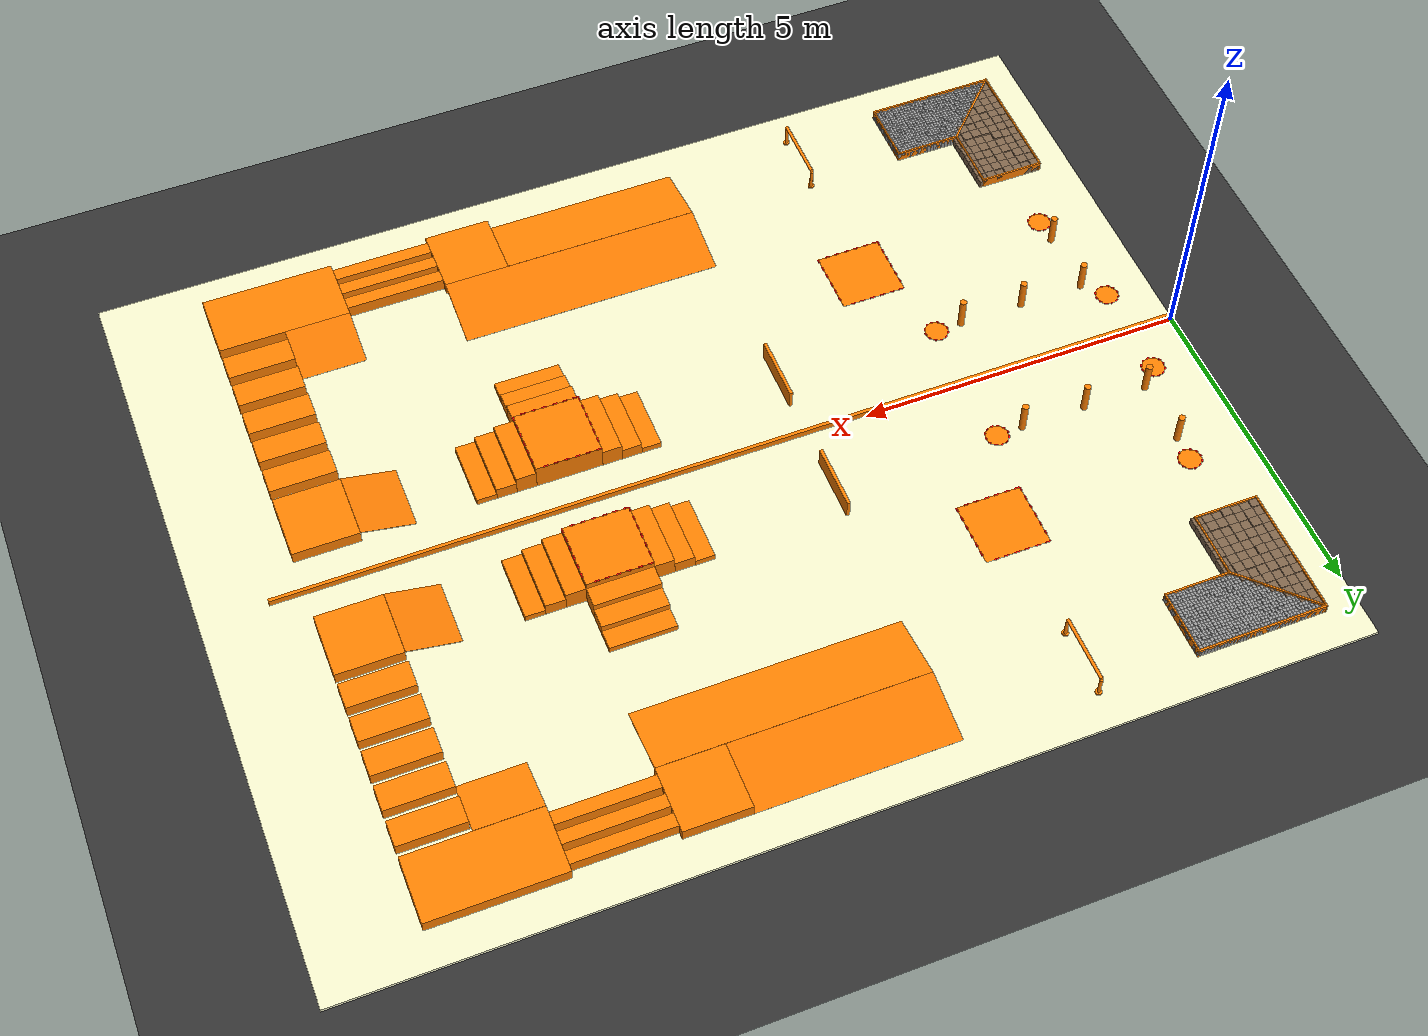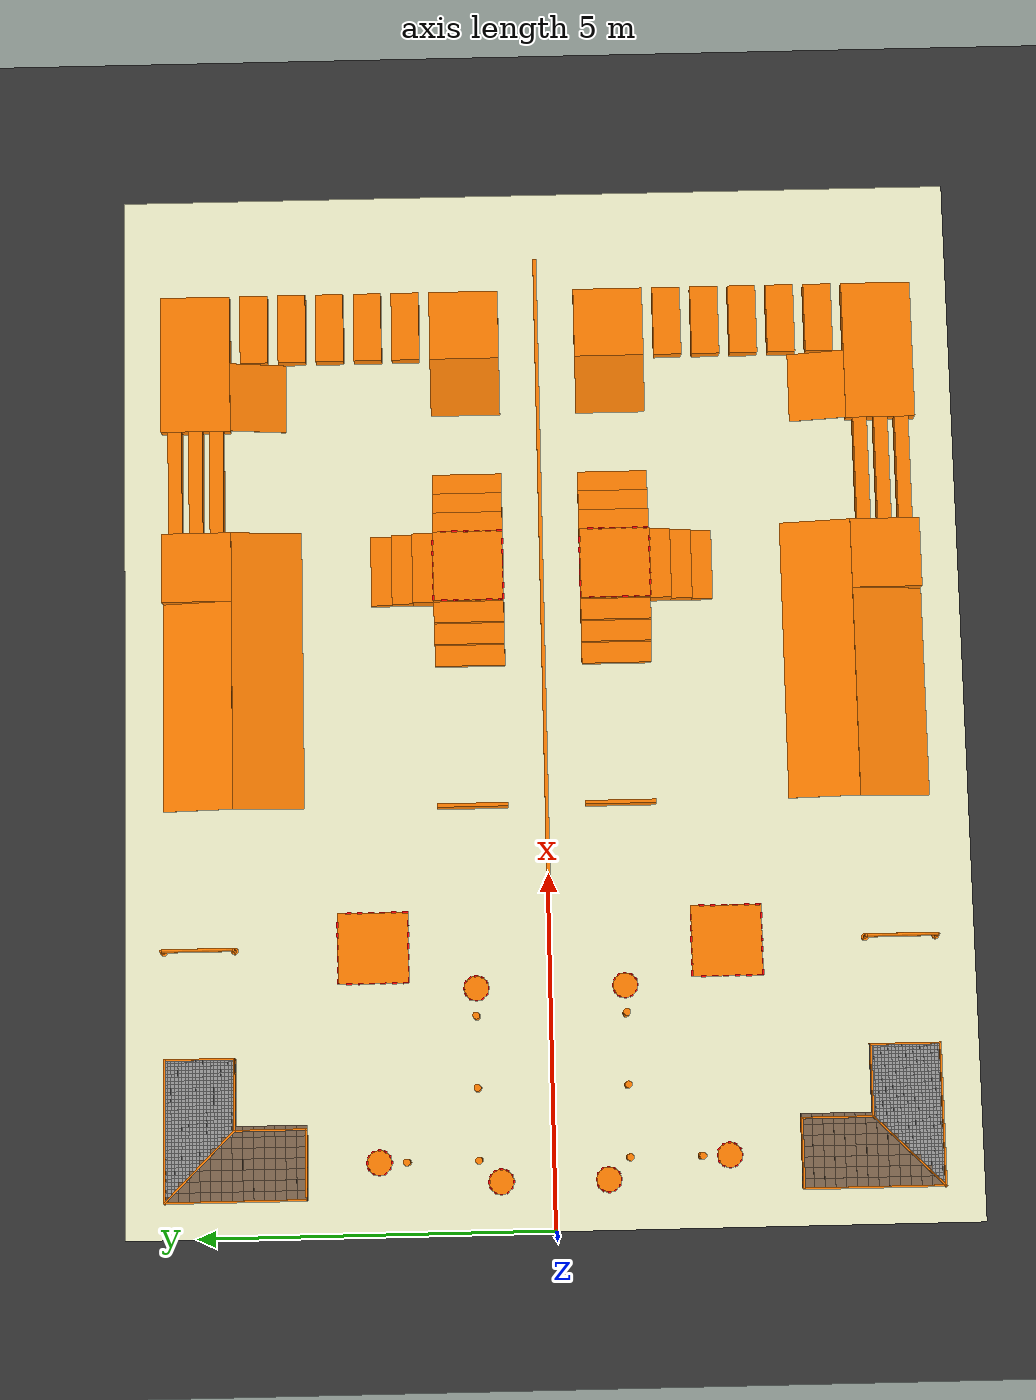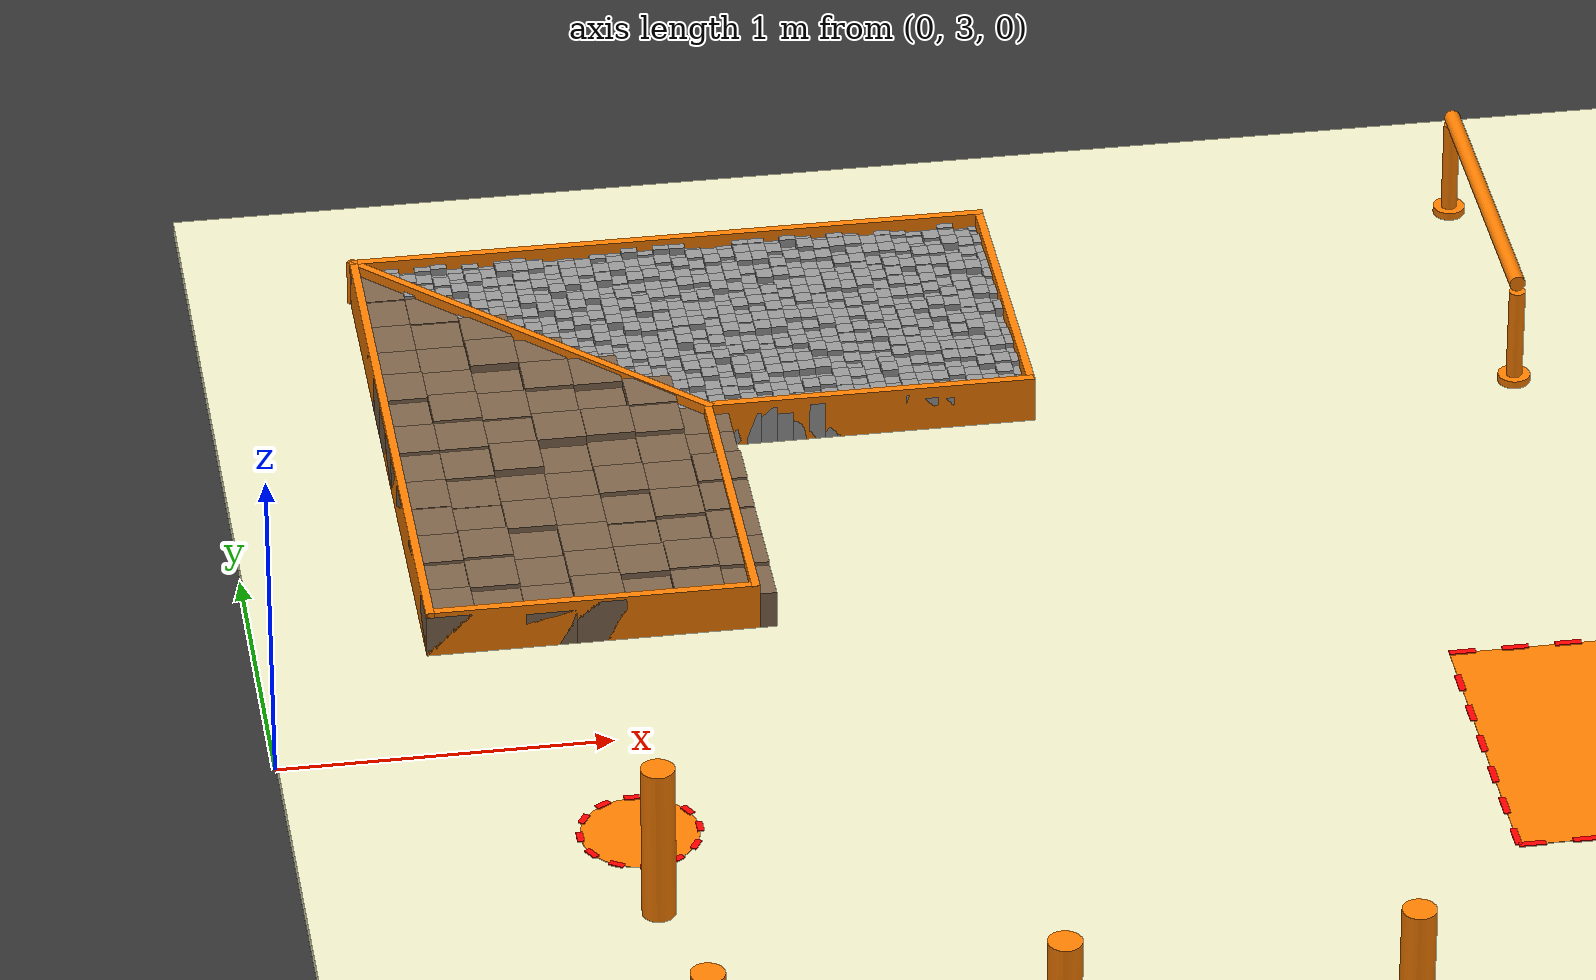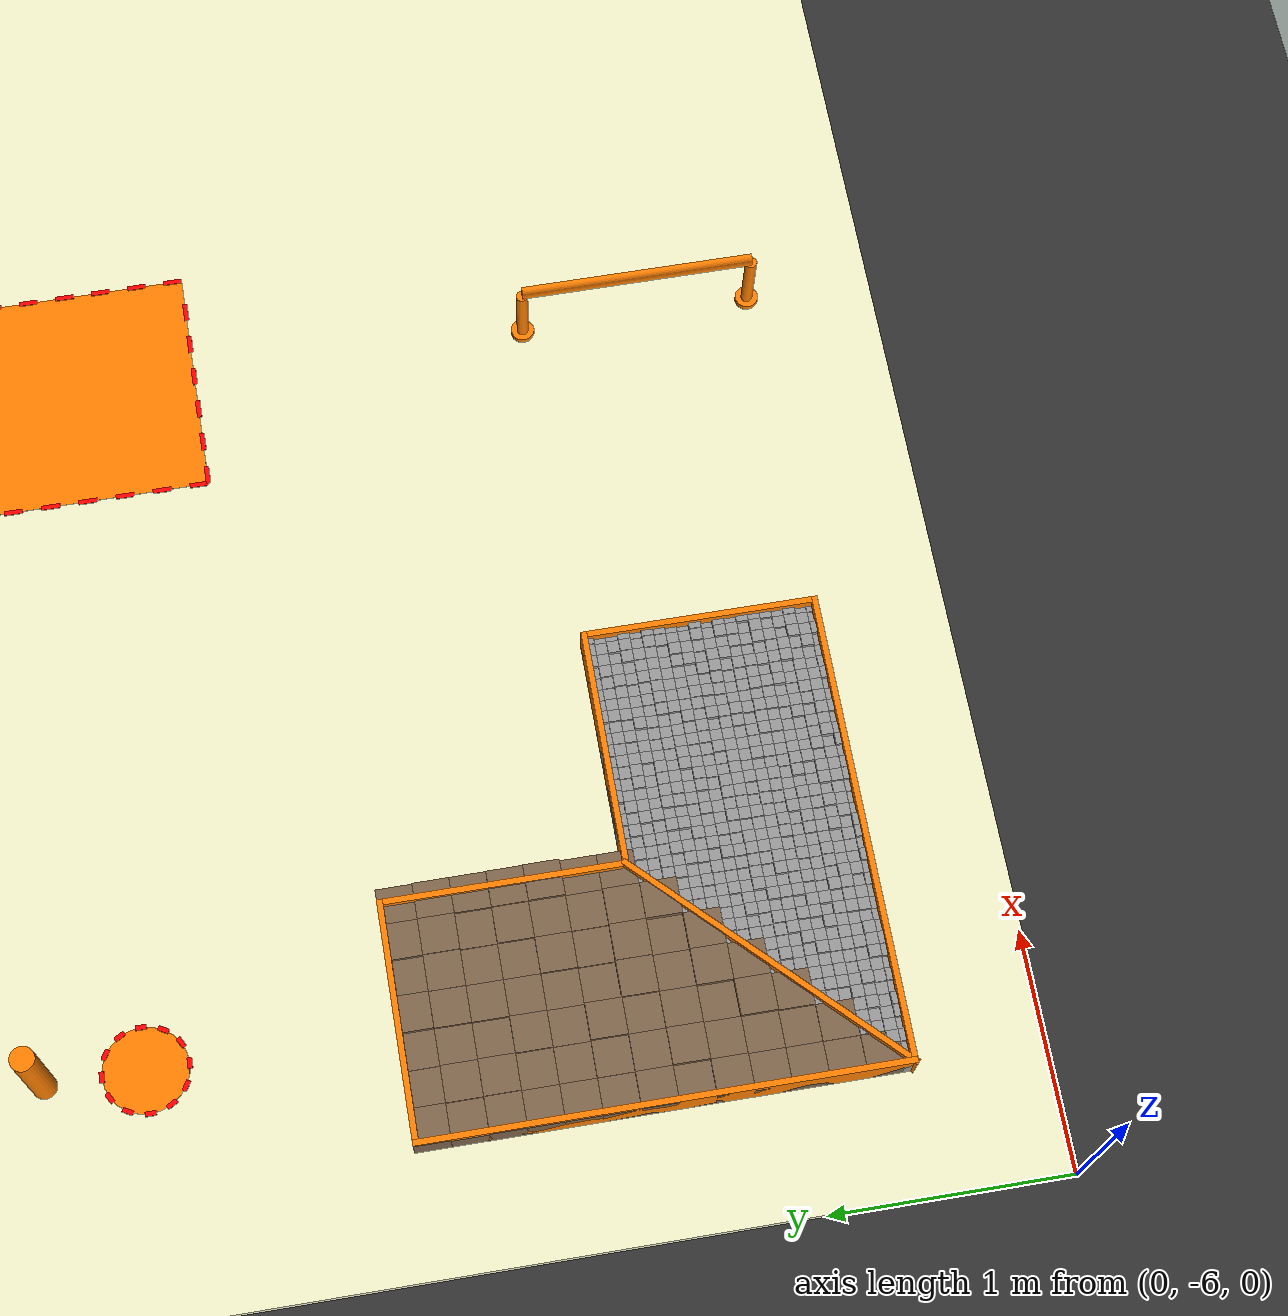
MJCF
<?xml version="1.0" encoding="utf-8"?>
<mujoco model="map_robocon_dual_track">
  <compiler meshdir="../model/assets" />
  <statistic center="7.5 0 0.3" extent="9" />
  <visual>
    <headlight diffuse="0.6 0.6 0.6" ambient="0.3 0.3 0.3" specular="0 0 0" />
    <rgba haze="0.15 0.25 0.35 1" />
    <global azimuth="135" elevation="-25" />
    <quality shadowsize="4096" />
  </visual>
  <asset>
    <texture type="skybox" builtin="gradient" rgb1="0.3 0.5 0.7" rgb2="0 0 0" width="512" height="3072" />
  </asset>
  <option timestep="0.002" gravity="0 0 -9.81" />
  <worldbody>
    <light pos="7 0 10" dir="0 0 -1" directional="true" castshadow="true"/>
    <geom name="world_floor" type="plane" pos="7.5 0 0" size="20 15 0.1" rgba="0.2 0.2 0.2 1"/>
    <geom name="track_floor" type="box" pos="7.5 0 0.025" size="7.5 6.0 0.025" rgba="0.95 0.95 0.8 1"/>
    <geom name="pit_wall_left" type="box" pos="0.5125 4.4500 0.1250" size="0.0125 1.0000 0.0750" rgba="1.0 0.5 0.0 1"/>
    <geom name="pit_wall_top" type="box" pos="1.5000 5.4375 0.1250" size="1.0000 0.0125 0.0750" rgba="1.0 0.5 0.0 1"/>
    <geom name="pit_wall_right_top" type="box" pos="2.4875 4.9500 0.1250" size="0.0125 0.5000 0.0750" rgba="1.0 0.5 0.0 1"/>
    <geom name="pit_wall_inner" type="box" pos="2.0000 4.4625 0.1250" size="0.5000 0.0125 0.0750" rgba="1.0 0.5 0.0 1"/>
    <geom name="pit_wall_right_bot" type="box" pos="1.4875 3.9500 0.1250" size="0.0125 0.5000 0.0750" rgba="1.0 0.5 0.0 1"/>
    <geom name="pit_wall_bot" type="box" pos="1.0000 3.4625 0.1250" size="0.5000 0.0125 0.0750" rgba="1.0 0.5 0.0 1"/>
    <geom name="pit_separator" type="box" pos="1.0000 4.9500 0.1250" size="0.7071 0.0125 0.0750" quat="0.923879532511 0 0 -0.382683432365" rgba="1.0 0.5 0.0 1"/>
    <geom name="gravel_500_5400" type="box" pos="0.5250 5.4250 0.1096" size="0.0250 0.0250 0.0596" rgba="0.6 0.6 0.6 1"/>
    <geom name="gravel_550_5350" type="box" pos="0.5750 5.3750 0.1004" size="0.0250 0.0250 0.0504" rgba="0.6 0.6 0.6 1"/>
    <geom name="gravel_550_5400" type="box" pos="0.5750 5.4250 0.1041" size="0.0250 0.0250 0.0541" rgba="0.6 0.6 0.6 1"/>
    <geom name="gravel_600_5300" type="box" pos="0.6250 5.3250 0.1033" size="0.0250 0.0250 0.0533" rgba="0.6 0.6 0.6 1"/>
    <geom name="gravel_600_5350" type="box" pos="0.6250 5.3750 0.1110" size="0.0250 0.0250 0.0610" rgba="0.6 0.6 0.6 1"/>
    <geom name="gravel_600_5400" type="box" pos="0.6250 5.4250 0.1102" size="0.0250 0.0250 0.0602" rgba="0.6 0.6 0.6 1"/>
    <geom name="gravel_650_5250" type="box" pos="0.6750 5.2750 0.1134" size="0.0250 0.0250 0.0634" rgba="0.6 0.6 0.6 1"/>
    <geom name="gravel_650_5300" type="box" pos="0.6750 5.3250 0.1013" size="0.0250 0.0250 0.0513" rgba="0.6 0.6 0.6 1"/>
    <geom name="gravel_650_5350" type="box" pos="0.6750 5.3750 0.1063" size="0.0250 0.0250 0.0563" rgba="0.6 0.6 0.6 1"/>
    <geom name="gravel_650_5400" type="box" pos="0.6750 5.4250 0.1004" size="0.0250 0.0250 0.0504" rgba="0.6 0.6 0.6 1"/>
    <geom name="gravel_700_5200" type="box" pos="0.7250 5.2250 0.1033" size="0.0250 0.0250 0.0533" rgba="0.6 0.6 0.6 1"/>
    <geom name="gravel_700_5250" type="box" pos="0.7250 5.2750 0.1076" size="0.0250 0.0250 0.0576" rgba="0.6 0.6 0.6 1"/>
    <geom name="gravel_700_5300" type="box" pos="0.7250 5.3250 0.1004" size="0.0250 0.0250 0.0504" rgba="0.6 0.6 0.6 1"/>
    <geom name="gravel_700_5350" type="box" pos="0.7250 5.3750 0.1030" size="0.0250 0.0250 0.0530" rgba="0.6 0.6 0.6 1"/>
    <geom name="gravel_700_5400" type="box" pos="0.7250 5.4250 0.1097" size="0.0250 0.0250 0.0597" rgba="0.6 0.6 0.6 1"/>
    <geom name="gravel_750_5150" type="box" pos="0.7750 5.1750 0.1082" size="0.0250 0.0250 0.0582" rgba="0.6 0.6 0.6 1"/>
    <geom name="gravel_750_5200" type="box" pos="0.7750 5.2250 0.1033" size="0.0250 0.0250 0.0533" rgba="0.6 0.6 0.6 1"/>
    <geom name="gravel_750_5250" type="box" pos="0.7750 5.2750 0.1088" size="0.0250 0.0250 0.0588" rgba="0.6 0.6 0.6 1"/>
    <geom name="gravel_750_5300" type="box" pos="0.7750 5.3250 0.1121" size="0.0250 0.0250 0.0621" rgba="0.6 0.6 0.6 1"/>
    <geom name="gravel_750_5350" type="box" pos="0.7750 5.3750 0.1001" size="0.0250 0.0250 0.0501" rgba="0.6 0.6 0.6 1"/>
    <geom name="gravel_750_5400" type="box" pos="0.7750 5.4250 0.1121" size="0.0250 0.0250 0.0621" rgba="0.6 0.6 0.6 1"/>
    <geom name="gravel_800_5100" type="box" pos="0.8250 5.1250 0.1105" size="0.0250 0.0250 0.0605" rgba="0.6 0.6 0.6 1"/>
    <geom name="gravel_800_5150" type="box" pos="0.8250 5.1750 0.1051" size="0.0250 0.0250 0.0551" rgba="0.6 0.6 0.6 1"/>
    <geom name="gravel_800_5200" type="box" pos="0.8250 5.2250 0.1023" size="0.0250 0.0250 0.0523" rgba="0.6 0.6 0.6 1"/>
    <geom name="gravel_800_5250" type="box" pos="0.8250 5.2750 0.1144" size="0.0250 0.0250 0.0644" rgba="0.6 0.6 0.6 1"/>
    <geom name="gravel_800_5300" type="box" pos="0.8250 5.3250 0.1050" size="0.0250 0.0250 0.0550" rgba="0.6 0.6 0.6 1"/>
    <geom name="gravel_800_5350" type="box" pos="0.8250 5.3750 0.1014" size="0.0250 0.0250 0.0514" rgba="0.6 0.6 0.6 1"/>
    <geom name="gravel_800_5400" type="box" pos="0.8250 5.4250 0.1015" size="0.0250 0.0250 0.0515" rgba="0.6 0.6 0.6 1"/>
    <geom name="gravel_850_5050" type="box" pos="0.8750 5.0750 0.1127" size="0.0250 0.0250 0.0627" rgba="0.6 0.6 0.6 1"/>
    <geom name="gravel_850_5100" type="box" pos="0.8750 5.1250 0.1091" size="0.0250 0.0250 0.0591" rgba="0.6 0.6 0.6 1"/>
    <geom name="gravel_850_5150" type="box" pos="0.8750 5.1750 0.1121" size="0.0250 0.0250 0.0621" rgba="0.6 0.6 0.6 1"/>
    <geom name="gravel_850_5200" type="box" pos="0.8750 5.2250 0.1109" size="0.0250 0.0250 0.0609" rgba="0.6 0.6 0.6 1"/>
    <geom name="gravel_850_5250" type="box" pos="0.8750 5.2750 0.1080" size="0.0250 0.0250 0.0580" rgba="0.6 0.6 0.6 1"/>
    <geom name="gravel_850_5300" type="box" pos="0.8750 5.3250 0.1146" size="0.0250 0.0250 0.0646" rgba="0.6 0.6 0.6 1"/>
    <geom name="gravel_850_5350" type="box" pos="0.8750 5.3750 0.1057" size="0.0250 0.0250 0.0557" rgba="0.6 0.6 0.6 1"/>
    <geom name="gravel_850_5400" type="box" pos="0.8750 5.4250 0.1083" size="0.0250 0.0250 0.0583" rgba="0.6 0.6 0.6 1"/>
    <geom name="gravel_900_5000" type="box" pos="0.9250 5.0250 0.1124" size="0.0250 0.0250 0.0624" rgba="0.6 0.6 0.6 1"/>
    <geom name="gravel_900_5050" type="box" pos="0.9250 5.0750 0.1093" size="0.0250 0.0250 0.0593" rgba="0.6 0.6 0.6 1"/>
    <geom name="gravel_900_5100" type="box" pos="0.9250 5.1250 0.1129" size="0.0250 0.0250 0.0629" rgba="0.6 0.6 0.6 1"/>
    <geom name="gravel_900_5150" type="box" pos="0.9250 5.1750 0.1087" size="0.0250 0.0250 0.0587" rgba="0.6 0.6 0.6 1"/>
    <geom name="gravel_900_5200" type="box" pos="0.9250 5.2250 0.1106" size="0.0250 0.0250 0.0606" rgba="0.6 0.6 0.6 1"/>
    <geom name="gravel_900_5250" type="box" pos="0.9250 5.2750 0.1007" size="0.0250 0.0250 0.0507" rgba="0.6 0.6 0.6 1"/>
    <geom name="gravel_900_5300" type="box" pos="0.9250 5.3250 0.1034" size="0.0250 0.0250 0.0534" rgba="0.6 0.6 0.6 1"/>
    <geom name="gravel_900_5350" type="box" pos="0.9250 5.3750 0.1043" size="0.0250 0.0250 0.0543" rgba="0.6 0.6 0.6 1"/>
    <geom name="gravel_900_5400" type="box" pos="0.9250 5.4250 0.1012" size="0.0250 0.0250 0.0512" rgba="0.6 0.6 0.6 1"/>
    <geom name="gravel_950_4950" type="box" pos="0.9750 4.9750 0.1035" size="0.0250 0.0250 0.0535" rgba="0.6 0.6 0.6 1"/>
    <geom name="gravel_950_5000" type="box" pos="0.9750 5.0250 0.1015" size="0.0250 0.0250 0.0515" rgba="0.6 0.6 0.6 1"/>
    <geom name="gravel_950_5050" type="box" pos="0.9750 5.0750 0.1042" size="0.0250 0.0250 0.0542" rgba="0.6 0.6 0.6 1"/>
    <geom name="gravel_950_5100" type="box" pos="0.9750 5.1250 0.1095" size="0.0250 0.0250 0.0595" rgba="0.6 0.6 0.6 1"/>
    <geom name="gravel_950_5150" type="box" pos="0.9750 5.1750 0.1055" size="0.0250 0.0250 0.0555" rgba="0.6 0.6 0.6 1"/>
    <geom name="gravel_950_5200" type="box" pos="0.9750 5.2250 0.1056" size="0.0250 0.0250 0.0556" rgba="0.6 0.6 0.6 1"/>
    <geom name="gravel_950_5250" type="box" pos="0.9750 5.2750 0.1031" size="0.0250 0.0250 0.0531" rgba="0.6 0.6 0.6 1"/>
    <geom name="gravel_950_5300" type="box" pos="0.9750 5.3250 0.1040" size="0.0250 0.0250 0.0540" rgba="0.6 0.6 0.6 1"/>
    <geom name="gravel_950_5350" type="box" pos="0.9750 5.3750 0.1140" size="0.0250 0.0250 0.0640" rgba="0.6 0.6 0.6 1"/>
    <geom name="gravel_950_5400" type="box" pos="0.9750 5.4250 0.1097" size="0.0250 0.0250 0.0597" rgba="0.6 0.6 0.6 1"/>
    <geom name="gravel_1000_4900" type="box" pos="1.0250 4.9250 0.1091" size="0.0250 0.0250 0.0591" rgba="0.6 0.6 0.6 1"/>
    <geom name="gravel_1000_4950" type="box" pos="1.0250 4.9750 0.1026" size="0.0250 0.0250 0.0526" rgba="0.6 0.6 0.6 1"/>
    <geom name="gravel_1000_5000" type="box" pos="1.0250 5.0250 0.1109" size="0.0250 0.0250 0.0609" rgba="0.6 0.6 0.6 1"/>
    <geom name="gravel_1000_5050" type="box" pos="1.0250 5.0750 0.1025" size="0.0250 0.0250 0.0525" rgba="0.6 0.6 0.6 1"/>
    <geom name="gravel_1000_5100" type="box" pos="1.0250 5.1250 0.1057" size="0.0250 0.0250 0.0557" rgba="0.6 0.6 0.6 1"/>
    <geom name="gravel_1000_5150" type="box" pos="1.0250 5.1750 0.1148" size="0.0250 0.0250 0.0648" rgba="0.6 0.6 0.6 1"/>
    <geom name="gravel_1000_5200" type="box" pos="1.0250 5.2250 0.1096" size="0.0250 0.0250 0.0596" rgba="0.6 0.6 0.6 1"/>
    <geom name="gravel_1000_5250" type="box" pos="1.0250 5.2750 0.1084" size="0.0250 0.0250 0.0584" rgba="0.6 0.6 0.6 1"/>
    <geom name="gravel_1000_5300" type="box" pos="1.0250 5.3250 0.1103" size="0.0250 0.0250 0.0603" rgba="0.6 0.6 0.6 1"/>
    <geom name="gravel_1000_5350" type="box" pos="1.0250 5.3750 0.1126" size="0.0250 0.0250 0.0626" rgba="0.6 0.6 0.6 1"/>
    <geom name="gravel_1000_5400" type="box" pos="1.0250 5.4250 0.1116" size="0.0250 0.0250 0.0616" rgba="0.6 0.6 0.6 1"/>
    <geom name="gravel_1050_4850" type="box" pos="1.0750 4.8750 0.1034" size="0.0250 0.0250 0.0534" rgba="0.6 0.6 0.6 1"/>
    <geom name="gravel_1050_4900" type="box" pos="1.0750 4.9250 0.1005" size="0.0250 0.0250 0.0505" rgba="0.6 0.6 0.6 1"/>
    <geom name="gravel_1050_4950" type="box" pos="1.0750 4.9750 0.1047" size="0.0250 0.0250 0.0547" rgba="0.6 0.6 0.6 1"/>
    <geom name="gravel_1050_5000" type="box" pos="1.0750 5.0250 0.1040" size="0.0250 0.0250 0.0540" rgba="0.6 0.6 0.6 1"/>
    <geom name="gravel_1050_5050" type="box" pos="1.0750 5.0750 0.1032" size="0.0250 0.0250 0.0532" rgba="0.6 0.6 0.6 1"/>
    <geom name="gravel_1050_5100" type="box" pos="1.0750 5.1250 0.1141" size="0.0250 0.0250 0.0641" rgba="0.6 0.6 0.6 1"/>
    <geom name="gravel_1050_5150" type="box" pos="1.0750 5.1750 0.1131" size="0.0250 0.0250 0.0631" rgba="0.6 0.6 0.6 1"/>
    <geom name="gravel_1050_5200" type="box" pos="1.0750 5.2250 0.1047" size="0.0250 0.0250 0.0547" rgba="0.6 0.6 0.6 1"/>
    <geom name="gravel_1050_5250" type="box" pos="1.0750 5.2750 0.1098" size="0.0250 0.0250 0.0598" rgba="0.6 0.6 0.6 1"/>
    <geom name="gravel_1050_5300" type="box" pos="1.0750 5.3250 0.1059" size="0.0250 0.0250 0.0559" rgba="0.6 0.6 0.6 1"/>
    <geom name="gravel_1050_5350" type="box" pos="1.0750 5.3750 0.1137" size="0.0250 0.0250 0.0637" rgba="0.6 0.6 0.6 1"/>
    <geom name="gravel_1050_5400" type="box" pos="1.0750 5.4250 0.1069" size="0.0250 0.0250 0.0569" rgba="0.6 0.6 0.6 1"/>
    <geom name="gravel_1100_4800" type="box" pos="1.1250 4.8250 0.1040" size="0.0250 0.0250 0.0540" rgba="0.6 0.6 0.6 1"/>
    <geom name="gravel_1100_4850" type="box" pos="1.1250 4.8750 0.1037" size="0.0250 0.0250 0.0537" rgba="0.6 0.6 0.6 1"/>
    <geom name="gravel_1100_4900" type="box" pos="1.1250 4.9250 0.1084" size="0.0250 0.0250 0.0584" rgba="0.6 0.6 0.6 1"/>
    <geom name="gravel_1100_4950" type="box" pos="1.1250 4.9750 0.1039" size="0.0250 0.0250 0.0539" rgba="0.6 0.6 0.6 1"/>
    <geom name="gravel_1100_5000" type="box" pos="1.1250 5.0250 0.1088" size="0.0250 0.0250 0.0588" rgba="0.6 0.6 0.6 1"/>
    <geom name="gravel_1100_5050" type="box" pos="1.1250 5.0750 0.1135" size="0.0250 0.0250 0.0635" rgba="0.6 0.6 0.6 1"/>
    <geom name="gravel_1100_5100" type="box" pos="1.1250 5.1250 0.1060" size="0.0250 0.0250 0.0560" rgba="0.6 0.6 0.6 1"/>
    <geom name="gravel_1100_5150" type="box" pos="1.1250 5.1750 0.1033" size="0.0250 0.0250 0.0533" rgba="0.6 0.6 0.6 1"/>
    <geom name="gravel_1100_5200" type="box" pos="1.1250 5.2250 0.1150" size="0.0250 0.0250 0.0650" rgba="0.6 0.6 0.6 1"/>
    <geom name="gravel_1100_5250" type="box" pos="1.1250 5.2750 0.1076" size="0.0250 0.0250 0.0576" rgba="0.6 0.6 0.6 1"/>
    <geom name="gravel_1100_5300" type="box" pos="1.1250 5.3250 0.1014" size="0.0250 0.0250 0.0514" rgba="0.6 0.6 0.6 1"/>
    <geom name="gravel_1100_5350" type="box" pos="1.1250 5.3750 0.1007" size="0.0250 0.0250 0.0507" rgba="0.6 0.6 0.6 1"/>
    <geom name="gravel_1100_5400" type="box" pos="1.1250 5.4250 0.1016" size="0.0250 0.0250 0.0516" rgba="0.6 0.6 0.6 1"/>
    <geom name="gravel_1150_4750" type="box" pos="1.1750 4.7750 0.1094" size="0.0250 0.0250 0.0594" rgba="0.6 0.6 0.6 1"/>
    <geom name="gravel_1150_4800" type="box" pos="1.1750 4.8250 0.1119" size="0.0250 0.0250 0.0619" rgba="0.6 0.6 0.6 1"/>
    <geom name="gravel_1150_4850" type="box" pos="1.1750 4.8750 0.1063" size="0.0250 0.0250 0.0563" rgba="0.6 0.6 0.6 1"/>
    <geom name="gravel_1150_4900" type="box" pos="1.1750 4.9250 0.1010" size="0.0250 0.0250 0.0510" rgba="0.6 0.6 0.6 1"/>
    <geom name="gravel_1150_4950" type="box" pos="1.1750 4.9750 0.1057" size="0.0250 0.0250 0.0557" rgba="0.6 0.6 0.6 1"/>
    <geom name="gravel_1150_5000" type="box" pos="1.1750 5.0250 0.1149" size="0.0250 0.0250 0.0649" rgba="0.6 0.6 0.6 1"/>
    <geom name="gravel_1150_5050" type="box" pos="1.1750 5.0750 0.1079" size="0.0250 0.0250 0.0579" rgba="0.6 0.6 0.6 1"/>
    <geom name="gravel_1150_5100" type="box" pos="1.1750 5.1250 0.1146" size="0.0250 0.0250 0.0646" rgba="0.6 0.6 0.6 1"/>
    <geom name="gravel_1150_5150" type="box" pos="1.1750 5.1750 0.1129" size="0.0250 0.0250 0.0629" rgba="0.6 0.6 0.6 1"/>
    <geom name="gravel_1150_5200" type="box" pos="1.1750 5.2250 0.1002" size="0.0250 0.0250 0.0502" rgba="0.6 0.6 0.6 1"/>
    <geom name="gravel_1150_5250" type="box" pos="1.1750 5.2750 0.1108" size="0.0250 0.0250 0.0608" rgba="0.6 0.6 0.6 1"/>
    <geom name="gravel_1150_5300" type="box" pos="1.1750 5.3250 0.1102" size="0.0250 0.0250 0.0602" rgba="0.6 0.6 0.6 1"/>
    <geom name="gravel_1150_5350" type="box" pos="1.1750 5.3750 0.1081" size="0.0250 0.0250 0.0581" rgba="0.6 0.6 0.6 1"/>
    <geom name="gravel_1150_5400" type="box" pos="1.1750 5.4250 0.1040" size="0.0250 0.0250 0.0540" rgba="0.6 0.6 0.6 1"/>
    <geom name="gravel_1200_4700" type="box" pos="1.2250 4.7250 0.1096" size="0.0250 0.0250 0.0596" rgba="0.6 0.6 0.6 1"/>
    <geom name="gravel_1200_4750" type="box" pos="1.2250 4.7750 0.1017" size="0.0250 0.0250 0.0517" rgba="0.6 0.6 0.6 1"/>
    <geom name="gravel_1200_4800" type="box" pos="1.2250 4.8250 0.1065" size="0.0250 0.0250 0.0565" rgba="0.6 0.6 0.6 1"/>
    <geom name="gravel_1200_4850" type="box" pos="1.2250 4.8750 0.1068" size="0.0250 0.0250 0.0568" rgba="0.6 0.6 0.6 1"/>
    <geom name="gravel_1200_4900" type="box" pos="1.2250 4.9250 0.1143" size="0.0250 0.0250 0.0643" rgba="0.6 0.6 0.6 1"/>
    <geom name="gravel_1200_4950" type="box" pos="1.2250 4.9750 0.1131" size="0.0250 0.0250 0.0631" rgba="0.6 0.6 0.6 1"/>
    <geom name="gravel_1200_5000" type="box" pos="1.2250 5.0250 0.1040" size="0.0250 0.0250 0.0540" rgba="0.6 0.6 0.6 1"/>
    <geom name="gravel_1200_5050" type="box" pos="1.2250 5.0750 0.1075" size="0.0250 0.0250 0.0575" rgba="0.6 0.6 0.6 1"/>
    <geom name="gravel_1200_5100" type="box" pos="1.2250 5.1250 0.1027" size="0.0250 0.0250 0.0527" rgba="0.6 0.6 0.6 1"/>
    <geom name="gravel_1200_5150" type="box" pos="1.2250 5.1750 0.1137" size="0.0250 0.0250 0.0637" rgba="0.6 0.6 0.6 1"/>
    <geom name="gravel_1200_5200" type="box" pos="1.2250 5.2250 0.1131" size="0.0250 0.0250 0.0631" rgba="0.6 0.6 0.6 1"/>
    <geom name="gravel_1200_5250" type="box" pos="1.2250 5.2750 0.1045" size="0.0250 0.0250 0.0545" rgba="0.6 0.6 0.6 1"/>
    <geom name="gravel_1200_5300" type="box" pos="1.2250 5.3250 0.1096" size="0.0250 0.0250 0.0596" rgba="0.6 0.6 0.6 1"/>
    <geom name="gravel_1200_5350" type="box" pos="1.2250 5.3750 0.1091" size="0.0250 0.0250 0.0591" rgba="0.6 0.6 0.6 1"/>
    <geom name="gravel_1200_5400" type="box" pos="1.2250 5.4250 0.1023" size="0.0250 0.0250 0.0523" rgba="0.6 0.6 0.6 1"/>
    <geom name="gravel_1250_4650" type="box" pos="1.2750 4.6750 0.1114" size="0.0250 0.0250 0.0614" rgba="0.6 0.6 0.6 1"/>
    <geom name="gravel_1250_4700" type="box" pos="1.2750 4.7250 0.1081" size="0.0250 0.0250 0.0581" rgba="0.6 0.6 0.6 1"/>
    <geom name="gravel_1250_4750" type="box" pos="1.2750 4.7750 0.1117" size="0.0250 0.0250 0.0617" rgba="0.6 0.6 0.6 1"/>
    <geom name="gravel_1250_4800" type="box" pos="1.2750 4.8250 0.1080" size="0.0250 0.0250 0.0580" rgba="0.6 0.6 0.6 1"/>
    <geom name="gravel_1250_4850" type="box" pos="1.2750 4.8750 0.1000" size="0.0250 0.0250 0.0500" rgba="0.6 0.6 0.6 1"/>
    <geom name="gravel_1250_4900" type="box" pos="1.2750 4.9250 0.1049" size="0.0250 0.0250 0.0549" rgba="0.6 0.6 0.6 1"/>
    <geom name="gravel_1250_4950" type="box" pos="1.2750 4.9750 0.1003" size="0.0250 0.0250 0.0503" rgba="0.6 0.6 0.6 1"/>
    <geom name="gravel_1250_5000" type="box" pos="1.2750 5.0250 0.1139" size="0.0250 0.0250 0.0639" rgba="0.6 0.6 0.6 1"/>
    <geom name="gravel_1250_5050" type="box" pos="1.2750 5.0750 0.1132" size="0.0250 0.0250 0.0632" rgba="0.6 0.6 0.6 1"/>
    <geom name="gravel_1250_5100" type="box" pos="1.2750 5.1250 0.1125" size="0.0250 0.0250 0.0625" rgba="0.6 0.6 0.6 1"/>
    <geom name="gravel_1250_5150" type="box" pos="1.2750 5.1750 0.1046" size="0.0250 0.0250 0.0546" rgba="0.6 0.6 0.6 1"/>
    <geom name="gravel_1250_5200" type="box" pos="1.2750 5.2250 0.1009" size="0.0250 0.0250 0.0509" rgba="0.6 0.6 0.6 1"/>
    <geom name="gravel_1250_5250" type="box" pos="1.2750 5.2750 0.1132" size="0.0250 0.0250 0.0632" rgba="0.6 0.6 0.6 1"/>
    <geom name="gravel_1250_5300" type="box" pos="1.2750 5.3250 0.1142" size="0.0250 0.0250 0.0642" rgba="0.6 0.6 0.6 1"/>
    <geom name="gravel_1250_5350" type="box" pos="1.2750 5.3750 0.1013" size="0.0250 0.0250 0.0513" rgba="0.6 0.6 0.6 1"/>
    <geom name="gravel_1250_5400" type="box" pos="1.2750 5.4250 0.1073" size="0.0250 0.0250 0.0573" rgba="0.6 0.6 0.6 1"/>
    <geom name="gravel_1300_4600" type="box" pos="1.3250 4.6250 0.1010" size="0.0250 0.0250 0.0510" rgba="0.6 0.6 0.6 1"/>
    <geom name="gravel_1300_4650" type="box" pos="1.3250 4.6750 0.1114" size="0.0250 0.0250 0.0614" rgba="0.6 0.6 0.6 1"/>
    <geom name="gravel_1300_4700" type="box" pos="1.3250 4.7250 0.1115" size="0.0250 0.0250 0.0615" rgba="0.6 0.6 0.6 1"/>
    <geom name="gravel_1300_4750" type="box" pos="1.3250 4.7750 0.1019" size="0.0250 0.0250 0.0519" rgba="0.6 0.6 0.6 1"/>
    <geom name="gravel_1300_4800" type="box" pos="1.3250 4.8250 0.1071" size="0.0250 0.0250 0.0571" rgba="0.6 0.6 0.6 1"/>
    <geom name="gravel_1300_4850" type="box" pos="1.3250 4.8750 0.1082" size="0.0250 0.0250 0.0582" rgba="0.6 0.6 0.6 1"/>
    <geom name="gravel_1300_4900" type="box" pos="1.3250 4.9250 0.1040" size="0.0250 0.0250 0.0540" rgba="0.6 0.6 0.6 1"/>
    <geom name="gravel_1300_4950" type="box" pos="1.3250 4.9750 0.1131" size="0.0250 0.0250 0.0631" rgba="0.6 0.6 0.6 1"/>
    <geom name="gravel_1300_5000" type="box" pos="1.3250 5.0250 0.1063" size="0.0250 0.0250 0.0563" rgba="0.6 0.6 0.6 1"/>
    <geom name="gravel_1300_5050" type="box" pos="1.3250 5.0750 0.1032" size="0.0250 0.0250 0.0532" rgba="0.6 0.6 0.6 1"/>
    <geom name="gravel_1300_5100" type="box" pos="1.3250 5.1250 0.1081" size="0.0250 0.0250 0.0581" rgba="0.6 0.6 0.6 1"/>
    <geom name="gravel_1300_5150" type="box" pos="1.3250 5.1750 0.1109" size="0.0250 0.0250 0.0609" rgba="0.6 0.6 0.6 1"/>
    <geom name="gravel_1300_5200" type="box" pos="1.3250 5.2250 0.1030" size="0.0250 0.0250 0.0530" rgba="0.6 0.6 0.6 1"/>
    <geom name="gravel_1300_5250" type="box" pos="1.3250 5.2750 0.1047" size="0.0250 0.0250 0.0547" rgba="0.6 0.6 0.6 1"/>
    <geom name="gravel_1300_5300" type="box" pos="1.3250 5.3250 0.1149" size="0.0250 0.0250 0.0649" rgba="0.6 0.6 0.6 1"/>
    <geom name="gravel_1300_5350" type="box" pos="1.3250 5.3750 0.1097" size="0.0250 0.0250 0.0597" rgba="0.6 0.6 0.6 1"/>
    <geom name="gravel_1300_5400" type="box" pos="1.3250 5.4250 0.1066" size="0.0250 0.0250 0.0566" rgba="0.6 0.6 0.6 1"/>
    <geom name="gravel_1350_4550" type="box" pos="1.3750 4.5750 0.1078" size="0.0250 0.0250 0.0578" rgba="0.6 0.6 0.6 1"/>
    <geom name="gravel_1350_4600" type="box" pos="1.3750 4.6250 0.1018" size="0.0250 0.0250 0.0518" rgba="0.6 0.6 0.6 1"/>
    <geom name="gravel_1350_4650" type="box" pos="1.3750 4.6750 0.1034" size="0.0250 0.0250 0.0534" rgba="0.6 0.6 0.6 1"/>
    <geom name="gravel_1350_4700" type="box" pos="1.3750 4.7250 0.1051" size="0.0250 0.0250 0.0551" rgba="0.6 0.6 0.6 1"/>
    <geom name="gravel_1350_4750" type="box" pos="1.3750 4.7750 0.1088" size="0.0250 0.0250 0.0588" rgba="0.6 0.6 0.6 1"/>
    <geom name="gravel_1350_4800" type="box" pos="1.3750 4.8250 0.1035" size="0.0250 0.0250 0.0535" rgba="0.6 0.6 0.6 1"/>
    <geom name="gravel_1350_4850" type="box" pos="1.3750 4.8750 0.1033" size="0.0250 0.0250 0.0533" rgba="0.6 0.6 0.6 1"/>
    <geom name="gravel_1350_4900" type="box" pos="1.3750 4.9250 0.1011" size="0.0250 0.0250 0.0511" rgba="0.6 0.6 0.6 1"/>
    <geom name="gravel_1350_4950" type="box" pos="1.3750 4.9750 0.1095" size="0.0250 0.0250 0.0595" rgba="0.6 0.6 0.6 1"/>
    <geom name="gravel_1350_5000" type="box" pos="1.3750 5.0250 0.1034" size="0.0250 0.0250 0.0534" rgba="0.6 0.6 0.6 1"/>
    <geom name="gravel_1350_5050" type="box" pos="1.3750 5.0750 0.1136" size="0.0250 0.0250 0.0636" rgba="0.6 0.6 0.6 1"/>
    <geom name="gravel_1350_5100" type="box" pos="1.3750 5.1250 0.1129" size="0.0250 0.0250 0.0629" rgba="0.6 0.6 0.6 1"/>
    <geom name="gravel_1350_5150" type="box" pos="1.3750 5.1750 0.1011" size="0.0250 0.0250 0.0511" rgba="0.6 0.6 0.6 1"/>
    <geom name="gravel_1350_5200" type="box" pos="1.3750 5.2250 0.1036" size="0.0250 0.0250 0.0536" rgba="0.6 0.6 0.6 1"/>
    <geom name="gravel_1350_5250" type="box" pos="1.3750 5.2750 0.1100" size="0.0250 0.0250 0.0600" rgba="0.6 0.6 0.6 1"/>
    <geom name="gravel_1350_5300" type="box" pos="1.3750 5.3250 0.1032" size="0.0250 0.0250 0.0532" rgba="0.6 0.6 0.6 1"/>
    <geom name="gravel_1350_5350" type="box" pos="1.3750 5.3750 0.1020" size="0.0250 0.0250 0.0520" rgba="0.6 0.6 0.6 1"/>
    <geom name="gravel_1350_5400" type="box" pos="1.3750 5.4250 0.1140" size="0.0250 0.0250 0.0640" rgba="0.6 0.6 0.6 1"/>
    <geom name="gravel_1400_4500" type="box" pos="1.4250 4.5250 0.1086" size="0.0250 0.0250 0.0586" rgba="0.6 0.6 0.6 1"/>
    <geom name="gravel_1400_4550" type="box" pos="1.4250 4.5750 0.1071" size="0.0250 0.0250 0.0571" rgba="0.6 0.6 0.6 1"/>
    <geom name="gravel_1400_4600" type="box" pos="1.4250 4.6250 0.1118" size="0.0250 0.0250 0.0618" rgba="0.6 0.6 0.6 1"/>
    <geom name="gravel_1400_4650" type="box" pos="1.4250 4.6750 0.1121" size="0.0250 0.0250 0.0621" rgba="0.6 0.6 0.6 1"/>
    <geom name="gravel_1400_4700" type="box" pos="1.4250 4.7250 0.1029" size="0.0250 0.0250 0.0529" rgba="0.6 0.6 0.6 1"/>
    <geom name="gravel_1400_4750" type="box" pos="1.4250 4.7750 0.1015" size="0.0250 0.0250 0.0515" rgba="0.6 0.6 0.6 1"/>
    <geom name="gravel_1400_4800" type="box" pos="1.4250 4.8250 0.1065" size="0.0250 0.0250 0.0565" rgba="0.6 0.6 0.6 1"/>
    <geom name="gravel_1400_4850" type="box" pos="1.4250 4.8750 0.1064" size="0.0250 0.0250 0.0564" rgba="0.6 0.6 0.6 1"/>
    <geom name="gravel_1400_4900" type="box" pos="1.4250 4.9250 0.1070" size="0.0250 0.0250 0.0570" rgba="0.6 0.6 0.6 1"/>
    <geom name="gravel_1400_4950" type="box" pos="1.4250 4.9750 0.1109" size="0.0250 0.0250 0.0609" rgba="0.6 0.6 0.6 1"/>
    <geom name="gravel_1400_5000" type="box" pos="1.4250 5.0250 0.1101" size="0.0250 0.0250 0.0601" rgba="0.6 0.6 0.6 1"/>
    <geom name="gravel_1400_5050" type="box" pos="1.4250 5.0750 0.1148" size="0.0250 0.0250 0.0648" rgba="0.6 0.6 0.6 1"/>
    <geom name="gravel_1400_5100" type="box" pos="1.4250 5.1250 0.1015" size="0.0250 0.0250 0.0515" rgba="0.6 0.6 0.6 1"/>
    <geom name="gravel_1400_5150" type="box" pos="1.4250 5.1750 0.1060" size="0.0250 0.0250 0.0560" rgba="0.6 0.6 0.6 1"/>
    <geom name="gravel_1400_5200" type="box" pos="1.4250 5.2250 0.1051" size="0.0250 0.0250 0.0551" rgba="0.6 0.6 0.6 1"/>
    <geom name="gravel_1400_5250" type="box" pos="1.4250 5.2750 0.1129" size="0.0250 0.0250 0.0629" rgba="0.6 0.6 0.6 1"/>
    <geom name="gravel_1400_5300" type="box" pos="1.4250 5.3250 0.1037" size="0.0250 0.0250 0.0537" rgba="0.6 0.6 0.6 1"/>
    <geom name="gravel_1400_5350" type="box" pos="1.4250 5.3750 0.1029" size="0.0250 0.0250 0.0529" rgba="0.6 0.6 0.6 1"/>
    <geom name="gravel_1400_5400" type="box" pos="1.4250 5.4250 0.1067" size="0.0250 0.0250 0.0567" rgba="0.6 0.6 0.6 1"/>
    <geom name="gravel_1450_4450" type="box" pos="1.4750 4.4750 0.1063" size="0.0250 0.0250 0.0563" rgba="0.6 0.6 0.6 1"/>
    <geom name="gravel_1450_4500" type="box" pos="1.4750 4.5250 0.1042" size="0.0250 0.0250 0.0542" rgba="0.6 0.6 0.6 1"/>
    <geom name="gravel_1450_4550" type="box" pos="1.4750 4.5750 0.1037" size="0.0250 0.0250 0.0537" rgba="0.6 0.6 0.6 1"/>
    <geom name="gravel_1450_4600" type="box" pos="1.4750 4.6250 0.1138" size="0.0250 0.0250 0.0638" rgba="0.6 0.6 0.6 1"/>
    <geom name="gravel_1450_4650" type="box" pos="1.4750 4.6750 0.1066" size="0.0250 0.0250 0.0566" rgba="0.6 0.6 0.6 1"/>
    <geom name="gravel_1450_4700" type="box" pos="1.4750 4.7250 0.1129" size="0.0250 0.0250 0.0629" rgba="0.6 0.6 0.6 1"/>
    <geom name="gravel_1450_4750" type="box" pos="1.4750 4.7750 0.1083" size="0.0250 0.0250 0.0583" rgba="0.6 0.6 0.6 1"/>
    <geom name="gravel_1450_4800" type="box" pos="1.4750 4.8250 0.1008" size="0.0250 0.0250 0.0508" rgba="0.6 0.6 0.6 1"/>
    <geom name="gravel_1450_4850" type="box" pos="1.4750 4.8750 0.1150" size="0.0250 0.0250 0.0650" rgba="0.6 0.6 0.6 1"/>
    <geom name="gravel_1450_4900" type="box" pos="1.4750 4.9250 0.1125" size="0.0250 0.0250 0.0625" rgba="0.6 0.6 0.6 1"/>
    <geom name="gravel_1450_4950" type="box" pos="1.4750 4.9750 0.1145" size="0.0250 0.0250 0.0645" rgba="0.6 0.6 0.6 1"/>
    <geom name="gravel_1450_5000" type="box" pos="1.4750 5.0250 0.1139" size="0.0250 0.0250 0.0639" rgba="0.6 0.6 0.6 1"/>
    <geom name="gravel_1450_5050" type="box" pos="1.4750 5.0750 0.1127" size="0.0250 0.0250 0.0627" rgba="0.6 0.6 0.6 1"/>
    <geom name="gravel_1450_5100" type="box" pos="1.4750 5.1250 0.1025" size="0.0250 0.0250 0.0525" rgba="0.6 0.6 0.6 1"/>
    <geom name="gravel_1450_5150" type="box" pos="1.4750 5.1750 0.1073" size="0.0250 0.0250 0.0573" rgba="0.6 0.6 0.6 1"/>
    <geom name="gravel_1450_5200" type="box" pos="1.4750 5.2250 0.1032" size="0.0250 0.0250 0.0532" rgba="0.6 0.6 0.6 1"/>
    <geom name="gravel_1450_5250" type="box" pos="1.4750 5.2750 0.1060" size="0.0250 0.0250 0.0560" rgba="0.6 0.6 0.6 1"/>
    <geom name="gravel_1450_5300" type="box" pos="1.4750 5.3250 0.1009" size="0.0250 0.0250 0.0509" rgba="0.6 0.6 0.6 1"/>
    <geom name="gravel_1450_5350" type="box" pos="1.4750 5.3750 0.1057" size="0.0250 0.0250 0.0557" rgba="0.6 0.6 0.6 1"/>
    <geom name="gravel_1450_5400" type="box" pos="1.4750 5.4250 0.1148" size="0.0250 0.0250 0.0648" rgba="0.6 0.6 0.6 1"/>
    <geom name="gravel_1500_4450" type="box" pos="1.5250 4.4750 0.1040" size="0.0250 0.0250 0.0540" rgba="0.6 0.6 0.6 1"/>
    <geom name="gravel_1500_4500" type="box" pos="1.5250 4.5250 0.1118" size="0.0250 0.0250 0.0618" rgba="0.6 0.6 0.6 1"/>
    <geom name="gravel_1500_4550" type="box" pos="1.5250 4.5750 0.1068" size="0.0250 0.0250 0.0568" rgba="0.6 0.6 0.6 1"/>
    <geom name="gravel_1500_4600" type="box" pos="1.5250 4.6250 0.1063" size="0.0250 0.0250 0.0563" rgba="0.6 0.6 0.6 1"/>
    <geom name="gravel_1500_4650" type="box" pos="1.5250 4.6750 0.1144" size="0.0250 0.0250 0.0644" rgba="0.6 0.6 0.6 1"/>
    <geom name="gravel_1500_4700" type="box" pos="1.5250 4.7250 0.1149" size="0.0250 0.0250 0.0649" rgba="0.6 0.6 0.6 1"/>
    <geom name="gravel_1500_4750" type="box" pos="1.5250 4.7750 0.1083" size="0.0250 0.0250 0.0583" rgba="0.6 0.6 0.6 1"/>
    <geom name="gravel_1500_4800" type="box" pos="1.5250 4.8250 0.1108" size="0.0250 0.0250 0.0608" rgba="0.6 0.6 0.6 1"/>
    <geom name="gravel_1500_4850" type="box" pos="1.5250 4.8750 0.1023" size="0.0250 0.0250 0.0523" rgba="0.6 0.6 0.6 1"/>
    <geom name="gravel_1500_4900" type="box" pos="1.5250 4.9250 0.1045" size="0.0250 0.0250 0.0545" rgba="0.6 0.6 0.6 1"/>
    <geom name="gravel_1500_4950" type="box" pos="1.5250 4.9750 0.1145" size="0.0250 0.0250 0.0645" rgba="0.6 0.6 0.6 1"/>
    <geom name="gravel_1500_5000" type="box" pos="1.5250 5.0250 0.1087" size="0.0250 0.0250 0.0587" rgba="0.6 0.6 0.6 1"/>
    <geom name="gravel_1500_5050" type="box" pos="1.5250 5.0750 0.1081" size="0.0250 0.0250 0.0581" rgba="0.6 0.6 0.6 1"/>
    <geom name="gravel_1500_5100" type="box" pos="1.5250 5.1250 0.1112" size="0.0250 0.0250 0.0612" rgba="0.6 0.6 0.6 1"/>
    <geom name="gravel_1500_5150" type="box" pos="1.5250 5.1750 0.1009" size="0.0250 0.0250 0.0509" rgba="0.6 0.6 0.6 1"/>
    <geom name="gravel_1500_5200" type="box" pos="1.5250 5.2250 0.1088" size="0.0250 0.0250 0.0588" rgba="0.6 0.6 0.6 1"/>
    <geom name="gravel_1500_5250" type="box" pos="1.5250 5.2750 0.1075" size="0.0250 0.0250 0.0575" rgba="0.6 0.6 0.6 1"/>
    <geom name="gravel_1500_5300" type="box" pos="1.5250 5.3250 0.1128" size="0.0250 0.0250 0.0628" rgba="0.6 0.6 0.6 1"/>
    <geom name="gravel_1500_5350" type="box" pos="1.5250 5.3750 0.1024" size="0.0250 0.0250 0.0524" rgba="0.6 0.6 0.6 1"/>
    <geom name="gravel_1500_5400" type="box" pos="1.5250 5.4250 0.1144" size="0.0250 0.0250 0.0644" rgba="0.6 0.6 0.6 1"/>
    <geom name="gravel_1550_4450" type="box" pos="1.5750 4.4750 0.1012" size="0.0250 0.0250 0.0512" rgba="0.6 0.6 0.6 1"/>
    <geom name="gravel_1550_4500" type="box" pos="1.5750 4.5250 0.1028" size="0.0250 0.0250 0.0528" rgba="0.6 0.6 0.6 1"/>
    <geom name="gravel_1550_4550" type="box" pos="1.5750 4.5750 0.1089" size="0.0250 0.0250 0.0589" rgba="0.6 0.6 0.6 1"/>
    <geom name="gravel_1550_4600" type="box" pos="1.5750 4.6250 0.1101" size="0.0250 0.0250 0.0601" rgba="0.6 0.6 0.6 1"/>
    <geom name="gravel_1550_4650" type="box" pos="1.5750 4.6750 0.1035" size="0.0250 0.0250 0.0535" rgba="0.6 0.6 0.6 1"/>
    <geom name="gravel_1550_4700" type="box" pos="1.5750 4.7250 0.1018" size="0.0250 0.0250 0.0518" rgba="0.6 0.6 0.6 1"/>
    <geom name="gravel_1550_4750" type="box" pos="1.5750 4.7750 0.1134" size="0.0250 0.0250 0.0634" rgba="0.6 0.6 0.6 1"/>
    <geom name="gravel_1550_4800" type="box" pos="1.5750 4.8250 0.1037" size="0.0250 0.0250 0.0537" rgba="0.6 0.6 0.6 1"/>
    <geom name="gravel_1550_4850" type="box" pos="1.5750 4.8750 0.1089" size="0.0250 0.0250 0.0589" rgba="0.6 0.6 0.6 1"/>
    <geom name="gravel_1550_4900" type="box" pos="1.5750 4.9250 0.1093" size="0.0250 0.0250 0.0593" rgba="0.6 0.6 0.6 1"/>
    <geom name="gravel_1550_4950" type="box" pos="1.5750 4.9750 0.1063" size="0.0250 0.0250 0.0563" rgba="0.6 0.6 0.6 1"/>
    <geom name="gravel_1550_5000" type="box" pos="1.5750 5.0250 0.1088" size="0.0250 0.0250 0.0588" rgba="0.6 0.6 0.6 1"/>
    <geom name="gravel_1550_5050" type="box" pos="1.5750 5.0750 0.1078" size="0.0250 0.0250 0.0578" rgba="0.6 0.6 0.6 1"/>
    <geom name="gravel_1550_5100" type="box" pos="1.5750 5.1250 0.1140" size="0.0250 0.0250 0.0640" rgba="0.6 0.6 0.6 1"/>
    <geom name="gravel_1550_5150" type="box" pos="1.5750 5.1750 0.1031" size="0.0250 0.0250 0.0531" rgba="0.6 0.6 0.6 1"/>
    <geom name="gravel_1550_5200" type="box" pos="1.5750 5.2250 0.1107" size="0.0250 0.0250 0.0607" rgba="0.6 0.6 0.6 1"/>
    <geom name="gravel_1550_5250" type="box" pos="1.5750 5.2750 0.1036" size="0.0250 0.0250 0.0536" rgba="0.6 0.6 0.6 1"/>
    <geom name="gravel_1550_5300" type="box" pos="1.5750 5.3250 0.1059" size="0.0250 0.0250 0.0559" rgba="0.6 0.6 0.6 1"/>
    <geom name="gravel_1550_5350" type="box" pos="1.5750 5.3750 0.1101" size="0.0250 0.0250 0.0601" rgba="0.6 0.6 0.6 1"/>
    <geom name="gravel_1550_5400" type="box" pos="1.5750 5.4250 0.1045" size="0.0250 0.0250 0.0545" rgba="0.6 0.6 0.6 1"/>
    <geom name="gravel_1600_4450" type="box" pos="1.6250 4.4750 0.1047" size="0.0250 0.0250 0.0547" rgba="0.6 0.6 0.6 1"/>
    <geom name="gravel_1600_4500" type="box" pos="1.6250 4.5250 0.1113" size="0.0250 0.0250 0.0613" rgba="0.6 0.6 0.6 1"/>
    <geom name="gravel_1600_4550" type="box" pos="1.6250 4.5750 0.1011" size="0.0250 0.0250 0.0511" rgba="0.6 0.6 0.6 1"/>
    <geom name="gravel_1600_4600" type="box" pos="1.6250 4.6250 0.1069" size="0.0250 0.0250 0.0569" rgba="0.6 0.6 0.6 1"/>
    <geom name="gravel_1600_4650" type="box" pos="1.6250 4.6750 0.1150" size="0.0250 0.0250 0.0650" rgba="0.6 0.6 0.6 1"/>
    <geom name="gravel_1600_4700" type="box" pos="1.6250 4.7250 0.1149" size="0.0250 0.0250 0.0649" rgba="0.6 0.6 0.6 1"/>
    <geom name="gravel_1600_4750" type="box" pos="1.6250 4.7750 0.1011" size="0.0250 0.0250 0.0511" rgba="0.6 0.6 0.6 1"/>
    <geom name="gravel_1600_4800" type="box" pos="1.6250 4.8250 0.1032" size="0.0250 0.0250 0.0532" rgba="0.6 0.6 0.6 1"/>
    <geom name="gravel_1600_4850" type="box" pos="1.6250 4.8750 0.1040" size="0.0250 0.0250 0.0540" rgba="0.6 0.6 0.6 1"/>
    <geom name="gravel_1600_4900" type="box" pos="1.6250 4.9250 0.1140" size="0.0250 0.0250 0.0640" rgba="0.6 0.6 0.6 1"/>
    <geom name="gravel_1600_4950" type="box" pos="1.6250 4.9750 0.1132" size="0.0250 0.0250 0.0632" rgba="0.6 0.6 0.6 1"/>
    <geom name="gravel_1600_5000" type="box" pos="1.6250 5.0250 0.1132" size="0.0250 0.0250 0.0632" rgba="0.6 0.6 0.6 1"/>
    <geom name="gravel_1600_5050" type="box" pos="1.6250 5.0750 0.1055" size="0.0250 0.0250 0.0555" rgba="0.6 0.6 0.6 1"/>
    <geom name="gravel_1600_5100" type="box" pos="1.6250 5.1250 0.1024" size="0.0250 0.0250 0.0524" rgba="0.6 0.6 0.6 1"/>
    <geom name="gravel_1600_5150" type="box" pos="1.6250 5.1750 0.1125" size="0.0250 0.0250 0.0625" rgba="0.6 0.6 0.6 1"/>
    <geom name="gravel_1600_5200" type="box" pos="1.6250 5.2250 0.1106" size="0.0250 0.0250 0.0606" rgba="0.6 0.6 0.6 1"/>
    <geom name="gravel_1600_5250" type="box" pos="1.6250 5.2750 0.1092" size="0.0250 0.0250 0.0592" rgba="0.6 0.6 0.6 1"/>
    <geom name="gravel_1600_5300" type="box" pos="1.6250 5.3250 0.1148" size="0.0250 0.0250 0.0648" rgba="0.6 0.6 0.6 1"/>
    <geom name="gravel_1600_5350" type="box" pos="1.6250 5.3750 0.1098" size="0.0250 0.0250 0.0598" rgba="0.6 0.6 0.6 1"/>
    <geom name="gravel_1600_5400" type="box" pos="1.6250 5.4250 0.1001" size="0.0250 0.0250 0.0501" rgba="0.6 0.6 0.6 1"/>
    <geom name="gravel_1650_4450" type="box" pos="1.6750 4.4750 0.1123" size="0.0250 0.0250 0.0623" rgba="0.6 0.6 0.6 1"/>
    <geom name="gravel_1650_4500" type="box" pos="1.6750 4.5250 0.1045" size="0.0250 0.0250 0.0545" rgba="0.6 0.6 0.6 1"/>
    <geom name="gravel_1650_4550" type="box" pos="1.6750 4.5750 0.1100" size="0.0250 0.0250 0.0600" rgba="0.6 0.6 0.6 1"/>
    <geom name="gravel_1650_4600" type="box" pos="1.6750 4.6250 0.1141" size="0.0250 0.0250 0.0641" rgba="0.6 0.6 0.6 1"/>
    <geom name="gravel_1650_4650" type="box" pos="1.6750 4.6750 0.1020" size="0.0250 0.0250 0.0520" rgba="0.6 0.6 0.6 1"/>
    <geom name="gravel_1650_4700" type="box" pos="1.6750 4.7250 0.1017" size="0.0250 0.0250 0.0517" rgba="0.6 0.6 0.6 1"/>
    <geom name="gravel_1650_4750" type="box" pos="1.6750 4.7750 0.1016" size="0.0250 0.0250 0.0516" rgba="0.6 0.6 0.6 1"/>
    <geom name="gravel_1650_4800" type="box" pos="1.6750 4.8250 0.1083" size="0.0250 0.0250 0.0583" rgba="0.6 0.6 0.6 1"/>
    <geom name="gravel_1650_4850" type="box" pos="1.6750 4.8750 0.1041" size="0.0250 0.0250 0.0541" rgba="0.6 0.6 0.6 1"/>
    <geom name="gravel_1650_4900" type="box" pos="1.6750 4.9250 0.1091" size="0.0250 0.0250 0.0591" rgba="0.6 0.6 0.6 1"/>
    <geom name="gravel_1650_4950" type="box" pos="1.6750 4.9750 0.1108" size="0.0250 0.0250 0.0608" rgba="0.6 0.6 0.6 1"/>
    <geom name="gravel_1650_5000" type="box" pos="1.6750 5.0250 0.1031" size="0.0250 0.0250 0.0531" rgba="0.6 0.6 0.6 1"/>
    <geom name="gravel_1650_5050" type="box" pos="1.6750 5.0750 0.1095" size="0.0250 0.0250 0.0595" rgba="0.6 0.6 0.6 1"/>
    <geom name="gravel_1650_5100" type="box" pos="1.6750 5.1250 0.1040" size="0.0250 0.0250 0.0540" rgba="0.6 0.6 0.6 1"/>
    <geom name="gravel_1650_5150" type="box" pos="1.6750 5.1750 0.1073" size="0.0250 0.0250 0.0573" rgba="0.6 0.6 0.6 1"/>
    <geom name="gravel_1650_5200" type="box" pos="1.6750 5.2250 0.1136" size="0.0250 0.0250 0.0636" rgba="0.6 0.6 0.6 1"/>
    <geom name="gravel_1650_5250" type="box" pos="1.6750 5.2750 0.1127" size="0.0250 0.0250 0.0627" rgba="0.6 0.6 0.6 1"/>
    <geom name="gravel_1650_5300" type="box" pos="1.6750 5.3250 0.1014" size="0.0250 0.0250 0.0514" rgba="0.6 0.6 0.6 1"/>
    <geom name="gravel_1650_5350" type="box" pos="1.6750 5.3750 0.1064" size="0.0250 0.0250 0.0564" rgba="0.6 0.6 0.6 1"/>
    <geom name="gravel_1650_5400" type="box" pos="1.6750 5.4250 0.1042" size="0.0250 0.0250 0.0542" rgba="0.6 0.6 0.6 1"/>
    <geom name="gravel_1700_4450" type="box" pos="1.7250 4.4750 0.1001" size="0.0250 0.0250 0.0501" rgba="0.6 0.6 0.6 1"/>
    <geom name="gravel_1700_4500" type="box" pos="1.7250 4.5250 0.1116" size="0.0250 0.0250 0.0616" rgba="0.6 0.6 0.6 1"/>
    <geom name="gravel_1700_4550" type="box" pos="1.7250 4.5750 0.1096" size="0.0250 0.0250 0.0596" rgba="0.6 0.6 0.6 1"/>
    <geom name="gravel_1700_4600" type="box" pos="1.7250 4.6250 0.1039" size="0.0250 0.0250 0.0539" rgba="0.6 0.6 0.6 1"/>
    <geom name="gravel_1700_4650" type="box" pos="1.7250 4.6750 0.1111" size="0.0250 0.0250 0.0611" rgba="0.6 0.6 0.6 1"/>
    <geom name="gravel_1700_4700" type="box" pos="1.7250 4.7250 0.1083" size="0.0250 0.0250 0.0583" rgba="0.6 0.6 0.6 1"/>
    <geom name="gravel_1700_4750" type="box" pos="1.7250 4.7750 0.1064" size="0.0250 0.0250 0.0564" rgba="0.6 0.6 0.6 1"/>
    <geom name="gravel_1700_4800" type="box" pos="1.7250 4.8250 0.1001" size="0.0250 0.0250 0.0501" rgba="0.6 0.6 0.6 1"/>
    <geom name="gravel_1700_4850" type="box" pos="1.7250 4.8750 0.1011" size="0.0250 0.0250 0.0511" rgba="0.6 0.6 0.6 1"/>
    <geom name="gravel_1700_4900" type="box" pos="1.7250 4.9250 0.1132" size="0.0250 0.0250 0.0632" rgba="0.6 0.6 0.6 1"/>
    <geom name="gravel_1700_4950" type="box" pos="1.7250 4.9750 0.1136" size="0.0250 0.0250 0.0636" rgba="0.6 0.6 0.6 1"/>
    <geom name="gravel_1700_5000" type="box" pos="1.7250 5.0250 0.1082" size="0.0250 0.0250 0.0582" rgba="0.6 0.6 0.6 1"/>
    <geom name="gravel_1700_5050" type="box" pos="1.7250 5.0750 0.1125" size="0.0250 0.0250 0.0625" rgba="0.6 0.6 0.6 1"/>
    <geom name="gravel_1700_5100" type="box" pos="1.7250 5.1250 0.1087" size="0.0250 0.0250 0.0587" rgba="0.6 0.6 0.6 1"/>
    <geom name="gravel_1700_5150" type="box" pos="1.7250 5.1750 0.1022" size="0.0250 0.0250 0.0522" rgba="0.6 0.6 0.6 1"/>
    <geom name="gravel_1700_5200" type="box" pos="1.7250 5.2250 0.1019" size="0.0250 0.0250 0.0519" rgba="0.6 0.6 0.6 1"/>
    <geom name="gravel_1700_5250" type="box" pos="1.7250 5.2750 0.1046" size="0.0250 0.0250 0.0546" rgba="0.6 0.6 0.6 1"/>
    <geom name="gravel_1700_5300" type="box" pos="1.7250 5.3250 0.1135" size="0.0250 0.0250 0.0635" rgba="0.6 0.6 0.6 1"/>
    <geom name="gravel_1700_5350" type="box" pos="1.7250 5.3750 0.1119" size="0.0250 0.0250 0.0619" rgba="0.6 0.6 0.6 1"/>
    <geom name="gravel_1700_5400" type="box" pos="1.7250 5.4250 0.1129" size="0.0250 0.0250 0.0629" rgba="0.6 0.6 0.6 1"/>
    <geom name="gravel_1750_4450" type="box" pos="1.7750 4.4750 0.1135" size="0.0250 0.0250 0.0635" rgba="0.6 0.6 0.6 1"/>
    <geom name="gravel_1750_4500" type="box" pos="1.7750 4.5250 0.1032" size="0.0250 0.0250 0.0532" rgba="0.6 0.6 0.6 1"/>
    <geom name="gravel_1750_4550" type="box" pos="1.7750 4.5750 0.1037" size="0.0250 0.0250 0.0537" rgba="0.6 0.6 0.6 1"/>
    <geom name="gravel_1750_4600" type="box" pos="1.7750 4.6250 0.1015" size="0.0250 0.0250 0.0515" rgba="0.6 0.6 0.6 1"/>
    <geom name="gravel_1750_4650" type="box" pos="1.7750 4.6750 0.1117" size="0.0250 0.0250 0.0617" rgba="0.6 0.6 0.6 1"/>
    <geom name="gravel_1750_4700" type="box" pos="1.7750 4.7250 0.1133" size="0.0250 0.0250 0.0633" rgba="0.6 0.6 0.6 1"/>
    <geom name="gravel_1750_4750" type="box" pos="1.7750 4.7750 0.1061" size="0.0250 0.0250 0.0561" rgba="0.6 0.6 0.6 1"/>
    <geom name="gravel_1750_4800" type="box" pos="1.7750 4.8250 0.1093" size="0.0250 0.0250 0.0593" rgba="0.6 0.6 0.6 1"/>
    <geom name="gravel_1750_4850" type="box" pos="1.7750 4.8750 0.1023" size="0.0250 0.0250 0.0523" rgba="0.6 0.6 0.6 1"/>
    <geom name="gravel_1750_4900" type="box" pos="1.7750 4.9250 0.1139" size="0.0250 0.0250 0.0639" rgba="0.6 0.6 0.6 1"/>
    <geom name="gravel_1750_4950" type="box" pos="1.7750 4.9750 0.1130" size="0.0250 0.0250 0.0630" rgba="0.6 0.6 0.6 1"/>
    <geom name="gravel_1750_5000" type="box" pos="1.7750 5.0250 0.1146" size="0.0250 0.0250 0.0646" rgba="0.6 0.6 0.6 1"/>
    <geom name="gravel_1750_5050" type="box" pos="1.7750 5.0750 0.1122" size="0.0250 0.0250 0.0622" rgba="0.6 0.6 0.6 1"/>
    <geom name="gravel_1750_5100" type="box" pos="1.7750 5.1250 0.1132" size="0.0250 0.0250 0.0632" rgba="0.6 0.6 0.6 1"/>
    <geom name="gravel_1750_5150" type="box" pos="1.7750 5.1750 0.1004" size="0.0250 0.0250 0.0504" rgba="0.6 0.6 0.6 1"/>
    <geom name="gravel_1750_5200" type="box" pos="1.7750 5.2250 0.1110" size="0.0250 0.0250 0.0610" rgba="0.6 0.6 0.6 1"/>
    <geom name="gravel_1750_5250" type="box" pos="1.7750 5.2750 0.1050" size="0.0250 0.0250 0.0550" rgba="0.6 0.6 0.6 1"/>
    <geom name="gravel_1750_5300" type="box" pos="1.7750 5.3250 0.1140" size="0.0250 0.0250 0.0640" rgba="0.6 0.6 0.6 1"/>
    <geom name="gravel_1750_5350" type="box" pos="1.7750 5.3750 0.1120" size="0.0250 0.0250 0.0620" rgba="0.6 0.6 0.6 1"/>
    <geom name="gravel_1750_5400" type="box" pos="1.7750 5.4250 0.1130" size="0.0250 0.0250 0.0630" rgba="0.6 0.6 0.6 1"/>
    <geom name="gravel_1800_4450" type="box" pos="1.8250 4.4750 0.1122" size="0.0250 0.0250 0.0622" rgba="0.6 0.6 0.6 1"/>
    <geom name="gravel_1800_4500" type="box" pos="1.8250 4.5250 0.1040" size="0.0250 0.0250 0.0540" rgba="0.6 0.6 0.6 1"/>
    <geom name="gravel_1800_4550" type="box" pos="1.8250 4.5750 0.1118" size="0.0250 0.0250 0.0618" rgba="0.6 0.6 0.6 1"/>
    <geom name="gravel_1800_4600" type="box" pos="1.8250 4.6250 0.1016" size="0.0250 0.0250 0.0516" rgba="0.6 0.6 0.6 1"/>
    <geom name="gravel_1800_4650" type="box" pos="1.8250 4.6750 0.1131" size="0.0250 0.0250 0.0631" rgba="0.6 0.6 0.6 1"/>
    <geom name="gravel_1800_4700" type="box" pos="1.8250 4.7250 0.1129" size="0.0250 0.0250 0.0629" rgba="0.6 0.6 0.6 1"/>
    <geom name="gravel_1800_4750" type="box" pos="1.8250 4.7750 0.1033" size="0.0250 0.0250 0.0533" rgba="0.6 0.6 0.6 1"/>
    <geom name="gravel_1800_4800" type="box" pos="1.8250 4.8250 0.1122" size="0.0250 0.0250 0.0622" rgba="0.6 0.6 0.6 1"/>
    <geom name="gravel_1800_4850" type="box" pos="1.8250 4.8750 0.1069" size="0.0250 0.0250 0.0569" rgba="0.6 0.6 0.6 1"/>
    <geom name="gravel_1800_4900" type="box" pos="1.8250 4.9250 0.1046" size="0.0250 0.0250 0.0546" rgba="0.6 0.6 0.6 1"/>
    <geom name="gravel_1800_4950" type="box" pos="1.8250 4.9750 0.1119" size="0.0250 0.0250 0.0619" rgba="0.6 0.6 0.6 1"/>
    <geom name="gravel_1800_5000" type="box" pos="1.8250 5.0250 0.1034" size="0.0250 0.0250 0.0534" rgba="0.6 0.6 0.6 1"/>
    <geom name="gravel_1800_5050" type="box" pos="1.8250 5.0750 0.1004" size="0.0250 0.0250 0.0504" rgba="0.6 0.6 0.6 1"/>
    <geom name="gravel_1800_5100" type="box" pos="1.8250 5.1250 0.1029" size="0.0250 0.0250 0.0529" rgba="0.6 0.6 0.6 1"/>
    <geom name="gravel_1800_5150" type="box" pos="1.8250 5.1750 0.1049" size="0.0250 0.0250 0.0549" rgba="0.6 0.6 0.6 1"/>
    <geom name="gravel_1800_5200" type="box" pos="1.8250 5.2250 0.1130" size="0.0250 0.0250 0.0630" rgba="0.6 0.6 0.6 1"/>
    <geom name="gravel_1800_5250" type="box" pos="1.8250 5.2750 0.1145" size="0.0250 0.0250 0.0645" rgba="0.6 0.6 0.6 1"/>
    <geom name="gravel_1800_5300" type="box" pos="1.8250 5.3250 0.1042" size="0.0250 0.0250 0.0542" rgba="0.6 0.6 0.6 1"/>
    <geom name="gravel_1800_5350" type="box" pos="1.8250 5.3750 0.1096" size="0.0250 0.0250 0.0596" rgba="0.6 0.6 0.6 1"/>
    <geom name="gravel_1800_5400" type="box" pos="1.8250 5.4250 0.1060" size="0.0250 0.0250 0.0560" rgba="0.6 0.6 0.6 1"/>
    <geom name="gravel_1850_4450" type="box" pos="1.8750 4.4750 0.1147" size="0.0250 0.0250 0.0647" rgba="0.6 0.6 0.6 1"/>
    <geom name="gravel_1850_4500" type="box" pos="1.8750 4.5250 0.1080" size="0.0250 0.0250 0.0580" rgba="0.6 0.6 0.6 1"/>
    <geom name="gravel_1850_4550" type="box" pos="1.8750 4.5750 0.1141" size="0.0250 0.0250 0.0641" rgba="0.6 0.6 0.6 1"/>
    <geom name="gravel_1850_4600" type="box" pos="1.8750 4.6250 0.1017" size="0.0250 0.0250 0.0517" rgba="0.6 0.6 0.6 1"/>
    <geom name="gravel_1850_4650" type="box" pos="1.8750 4.6750 0.1146" size="0.0250 0.0250 0.0646" rgba="0.6 0.6 0.6 1"/>
    <geom name="gravel_1850_4700" type="box" pos="1.8750 4.7250 0.1027" size="0.0250 0.0250 0.0527" rgba="0.6 0.6 0.6 1"/>
    <geom name="gravel_1850_4750" type="box" pos="1.8750 4.7750 0.1144" size="0.0250 0.0250 0.0644" rgba="0.6 0.6 0.6 1"/>
    <geom name="gravel_1850_4800" type="box" pos="1.8750 4.8250 0.1040" size="0.0250 0.0250 0.0540" rgba="0.6 0.6 0.6 1"/>
    <geom name="gravel_1850_4850" type="box" pos="1.8750 4.8750 0.1016" size="0.0250 0.0250 0.0516" rgba="0.6 0.6 0.6 1"/>
    <geom name="gravel_1850_4900" type="box" pos="1.8750 4.9250 0.1065" size="0.0250 0.0250 0.0565" rgba="0.6 0.6 0.6 1"/>
    <geom name="gravel_1850_4950" type="box" pos="1.8750 4.9750 0.1109" size="0.0250 0.0250 0.0609" rgba="0.6 0.6 0.6 1"/>
    <geom name="gravel_1850_5000" type="box" pos="1.8750 5.0250 0.1047" size="0.0250 0.0250 0.0547" rgba="0.6 0.6 0.6 1"/>
    <geom name="gravel_1850_5050" type="box" pos="1.8750 5.0750 0.1091" size="0.0250 0.0250 0.0591" rgba="0.6 0.6 0.6 1"/>
    <geom name="gravel_1850_5100" type="box" pos="1.8750 5.1250 0.1077" size="0.0250 0.0250 0.0577" rgba="0.6 0.6 0.6 1"/>
    <geom name="gravel_1850_5150" type="box" pos="1.8750 5.1750 0.1058" size="0.0250 0.0250 0.0558" rgba="0.6 0.6 0.6 1"/>
    <geom name="gravel_1850_5200" type="box" pos="1.8750 5.2250 0.1086" size="0.0250 0.0250 0.0586" rgba="0.6 0.6 0.6 1"/>
    <geom name="gravel_1850_5250" type="box" pos="1.8750 5.2750 0.1038" size="0.0250 0.0250 0.0538" rgba="0.6 0.6 0.6 1"/>
    <geom name="gravel_1850_5300" type="box" pos="1.8750 5.3250 0.1106" size="0.0250 0.0250 0.0606" rgba="0.6 0.6 0.6 1"/>
    <geom name="gravel_1850_5350" type="box" pos="1.8750 5.3750 0.1000" size="0.0250 0.0250 0.0500" rgba="0.6 0.6 0.6 1"/>
    <geom name="gravel_1850_5400" type="box" pos="1.8750 5.4250 0.1139" size="0.0250 0.0250 0.0639" rgba="0.6 0.6 0.6 1"/>
    <geom name="gravel_1900_4450" type="box" pos="1.9250 4.4750 0.1081" size="0.0250 0.0250 0.0581" rgba="0.6 0.6 0.6 1"/>
    <geom name="gravel_1900_4500" type="box" pos="1.9250 4.5250 0.1108" size="0.0250 0.0250 0.0608" rgba="0.6 0.6 0.6 1"/>
    <geom name="gravel_1900_4550" type="box" pos="1.9250 4.5750 0.1111" size="0.0250 0.0250 0.0611" rgba="0.6 0.6 0.6 1"/>
    <geom name="gravel_1900_4600" type="box" pos="1.9250 4.6250 0.1101" size="0.0250 0.0250 0.0601" rgba="0.6 0.6 0.6 1"/>
    <geom name="gravel_1900_4650" type="box" pos="1.9250 4.6750 0.1055" size="0.0250 0.0250 0.0555" rgba="0.6 0.6 0.6 1"/>
    <geom name="gravel_1900_4700" type="box" pos="1.9250 4.7250 0.1010" size="0.0250 0.0250 0.0510" rgba="0.6 0.6 0.6 1"/>
    <geom name="gravel_1900_4750" type="box" pos="1.9250 4.7750 0.1100" size="0.0250 0.0250 0.0600" rgba="0.6 0.6 0.6 1"/>
    <geom name="gravel_1900_4800" type="box" pos="1.9250 4.8250 0.1050" size="0.0250 0.0250 0.0550" rgba="0.6 0.6 0.6 1"/>
    <geom name="gravel_1900_4850" type="box" pos="1.9250 4.8750 0.1047" size="0.0250 0.0250 0.0547" rgba="0.6 0.6 0.6 1"/>
    <geom name="gravel_1900_4900" type="box" pos="1.9250 4.9250 0.1127" size="0.0250 0.0250 0.0627" rgba="0.6 0.6 0.6 1"/>
    <geom name="gravel_1900_4950" type="box" pos="1.9250 4.9750 0.1108" size="0.0250 0.0250 0.0608" rgba="0.6 0.6 0.6 1"/>
    <geom name="gravel_1900_5000" type="box" pos="1.9250 5.0250 0.1045" size="0.0250 0.0250 0.0545" rgba="0.6 0.6 0.6 1"/>
    <geom name="gravel_1900_5050" type="box" pos="1.9250 5.0750 0.1046" size="0.0250 0.0250 0.0546" rgba="0.6 0.6 0.6 1"/>
    <geom name="gravel_1900_5100" type="box" pos="1.9250 5.1250 0.1061" size="0.0250 0.0250 0.0561" rgba="0.6 0.6 0.6 1"/>
    <geom name="gravel_1900_5150" type="box" pos="1.9250 5.1750 0.1060" size="0.0250 0.0250 0.0560" rgba="0.6 0.6 0.6 1"/>
    <geom name="gravel_1900_5200" type="box" pos="1.9250 5.2250 0.1044" size="0.0250 0.0250 0.0544" rgba="0.6 0.6 0.6 1"/>
    <geom name="gravel_1900_5250" type="box" pos="1.9250 5.2750 0.1019" size="0.0250 0.0250 0.0519" rgba="0.6 0.6 0.6 1"/>
    <geom name="gravel_1900_5300" type="box" pos="1.9250 5.3250 0.1063" size="0.0250 0.0250 0.0563" rgba="0.6 0.6 0.6 1"/>
    <geom name="gravel_1900_5350" type="box" pos="1.9250 5.3750 0.1141" size="0.0250 0.0250 0.0641" rgba="0.6 0.6 0.6 1"/>
    <geom name="gravel_1900_5400" type="box" pos="1.9250 5.4250 0.1102" size="0.0250 0.0250 0.0602" rgba="0.6 0.6 0.6 1"/>
    <geom name="gravel_1950_4450" type="box" pos="1.9750 4.4750 0.1135" size="0.0250 0.0250 0.0635" rgba="0.6 0.6 0.6 1"/>
    <geom name="gravel_1950_4500" type="box" pos="1.9750 4.5250 0.1092" size="0.0250 0.0250 0.0592" rgba="0.6 0.6 0.6 1"/>
    <geom name="gravel_1950_4550" type="box" pos="1.9750 4.5750 0.1045" size="0.0250 0.0250 0.0545" rgba="0.6 0.6 0.6 1"/>
    <geom name="gravel_1950_4600" type="box" pos="1.9750 4.6250 0.1082" size="0.0250 0.0250 0.0582" rgba="0.6 0.6 0.6 1"/>
    <geom name="gravel_1950_4650" type="box" pos="1.9750 4.6750 0.1000" size="0.0250 0.0250 0.0500" rgba="0.6 0.6 0.6 1"/>
    <geom name="gravel_1950_4700" type="box" pos="1.9750 4.7250 0.1043" size="0.0250 0.0250 0.0543" rgba="0.6 0.6 0.6 1"/>
    <geom name="gravel_1950_4750" type="box" pos="1.9750 4.7750 0.1064" size="0.0250 0.0250 0.0564" rgba="0.6 0.6 0.6 1"/>
    <geom name="gravel_1950_4800" type="box" pos="1.9750 4.8250 0.1087" size="0.0250 0.0250 0.0587" rgba="0.6 0.6 0.6 1"/>
    <geom name="gravel_1950_4850" type="box" pos="1.9750 4.8750 0.1098" size="0.0250 0.0250 0.0598" rgba="0.6 0.6 0.6 1"/>
    <geom name="gravel_1950_4900" type="box" pos="1.9750 4.9250 0.1070" size="0.0250 0.0250 0.0570" rgba="0.6 0.6 0.6 1"/>
    <geom name="gravel_1950_4950" type="box" pos="1.9750 4.9750 0.1066" size="0.0250 0.0250 0.0566" rgba="0.6 0.6 0.6 1"/>
    <geom name="gravel_1950_5000" type="box" pos="1.9750 5.0250 0.1032" size="0.0250 0.0250 0.0532" rgba="0.6 0.6 0.6 1"/>
    <geom name="gravel_1950_5050" type="box" pos="1.9750 5.0750 0.1071" size="0.0250 0.0250 0.0571" rgba="0.6 0.6 0.6 1"/>
    <geom name="gravel_1950_5100" type="box" pos="1.9750 5.1250 0.1135" size="0.0250 0.0250 0.0635" rgba="0.6 0.6 0.6 1"/>
    <geom name="gravel_1950_5150" type="box" pos="1.9750 5.1750 0.1119" size="0.0250 0.0250 0.0619" rgba="0.6 0.6 0.6 1"/>
    <geom name="gravel_1950_5200" type="box" pos="1.9750 5.2250 0.1025" size="0.0250 0.0250 0.0525" rgba="0.6 0.6 0.6 1"/>
    <geom name="gravel_1950_5250" type="box" pos="1.9750 5.2750 0.1013" size="0.0250 0.0250 0.0513" rgba="0.6 0.6 0.6 1"/>
    <geom name="gravel_1950_5300" type="box" pos="1.9750 5.3250 0.1077" size="0.0250 0.0250 0.0577" rgba="0.6 0.6 0.6 1"/>
    <geom name="gravel_1950_5350" type="box" pos="1.9750 5.3750 0.1095" size="0.0250 0.0250 0.0595" rgba="0.6 0.6 0.6 1"/>
    <geom name="gravel_1950_5400" type="box" pos="1.9750 5.4250 0.1050" size="0.0250 0.0250 0.0550" rgba="0.6 0.6 0.6 1"/>
    <geom name="gravel_2000_4450" type="box" pos="2.0250 4.4750 0.1123" size="0.0250 0.0250 0.0623" rgba="0.6 0.6 0.6 1"/>
    <geom name="gravel_2000_4500" type="box" pos="2.0250 4.5250 0.1113" size="0.0250 0.0250 0.0613" rgba="0.6 0.6 0.6 1"/>
    <geom name="gravel_2000_4550" type="box" pos="2.0250 4.5750 0.1101" size="0.0250 0.0250 0.0601" rgba="0.6 0.6 0.6 1"/>
    <geom name="gravel_2000_4600" type="box" pos="2.0250 4.6250 0.1034" size="0.0250 0.0250 0.0534" rgba="0.6 0.6 0.6 1"/>
    <geom name="gravel_2000_4650" type="box" pos="2.0250 4.6750 0.1030" size="0.0250 0.0250 0.0530" rgba="0.6 0.6 0.6 1"/>
    <geom name="gravel_2000_4700" type="box" pos="2.0250 4.7250 0.1004" size="0.0250 0.0250 0.0504" rgba="0.6 0.6 0.6 1"/>
    <geom name="gravel_2000_4750" type="box" pos="2.0250 4.7750 0.1037" size="0.0250 0.0250 0.0537" rgba="0.6 0.6 0.6 1"/>
    <geom name="gravel_2000_4800" type="box" pos="2.0250 4.8250 0.1071" size="0.0250 0.0250 0.0571" rgba="0.6 0.6 0.6 1"/>
    <geom name="gravel_2000_4850" type="box" pos="2.0250 4.8750 0.1127" size="0.0250 0.0250 0.0627" rgba="0.6 0.6 0.6 1"/>
    <geom name="gravel_2000_4900" type="box" pos="2.0250 4.9250 0.1011" size="0.0250 0.0250 0.0511" rgba="0.6 0.6 0.6 1"/>
    <geom name="gravel_2000_4950" type="box" pos="2.0250 4.9750 0.1062" size="0.0250 0.0250 0.0562" rgba="0.6 0.6 0.6 1"/>
    <geom name="gravel_2000_5000" type="box" pos="2.0250 5.0250 0.1094" size="0.0250 0.0250 0.0594" rgba="0.6 0.6 0.6 1"/>
    <geom name="gravel_2000_5050" type="box" pos="2.0250 5.0750 0.1029" size="0.0250 0.0250 0.0529" rgba="0.6 0.6 0.6 1"/>
    <geom name="gravel_2000_5100" type="box" pos="2.0250 5.1250 0.1104" size="0.0250 0.0250 0.0604" rgba="0.6 0.6 0.6 1"/>
    <geom name="gravel_2000_5150" type="box" pos="2.0250 5.1750 0.1074" size="0.0250 0.0250 0.0574" rgba="0.6 0.6 0.6 1"/>
    <geom name="gravel_2000_5200" type="box" pos="2.0250 5.2250 0.1037" size="0.0250 0.0250 0.0537" rgba="0.6 0.6 0.6 1"/>
    <geom name="gravel_2000_5250" type="box" pos="2.0250 5.2750 0.1098" size="0.0250 0.0250 0.0598" rgba="0.6 0.6 0.6 1"/>
    <geom name="gravel_2000_5300" type="box" pos="2.0250 5.3250 0.1001" size="0.0250 0.0250 0.0501" rgba="0.6 0.6 0.6 1"/>
    <geom name="gravel_2000_5350" type="box" pos="2.0250 5.3750 0.1113" size="0.0250 0.0250 0.0613" rgba="0.6 0.6 0.6 1"/>
    <geom name="gravel_2000_5400" type="box" pos="2.0250 5.4250 0.1116" size="0.0250 0.0250 0.0616" rgba="0.6 0.6 0.6 1"/>
    <geom name="gravel_2050_4450" type="box" pos="2.0750 4.4750 0.1016" size="0.0250 0.0250 0.0516" rgba="0.6 0.6 0.6 1"/>
    <geom name="gravel_2050_4500" type="box" pos="2.0750 4.5250 0.1064" size="0.0250 0.0250 0.0564" rgba="0.6 0.6 0.6 1"/>
    <geom name="gravel_2050_4550" type="box" pos="2.0750 4.5750 0.1026" size="0.0250 0.0250 0.0526" rgba="0.6 0.6 0.6 1"/>
    <geom name="gravel_2050_4600" type="box" pos="2.0750 4.6250 0.1144" size="0.0250 0.0250 0.0644" rgba="0.6 0.6 0.6 1"/>
    <geom name="gravel_2050_4650" type="box" pos="2.0750 4.6750 0.1078" size="0.0250 0.0250 0.0578" rgba="0.6 0.6 0.6 1"/>
    <geom name="gravel_2050_4700" type="box" pos="2.0750 4.7250 0.1008" size="0.0250 0.0250 0.0508" rgba="0.6 0.6 0.6 1"/>
    <geom name="gravel_2050_4750" type="box" pos="2.0750 4.7750 0.1037" size="0.0250 0.0250 0.0537" rgba="0.6 0.6 0.6 1"/>
    <geom name="gravel_2050_4800" type="box" pos="2.0750 4.8250 0.1127" size="0.0250 0.0250 0.0627" rgba="0.6 0.6 0.6 1"/>
    <geom name="gravel_2050_4850" type="box" pos="2.0750 4.8750 0.1068" size="0.0250 0.0250 0.0568" rgba="0.6 0.6 0.6 1"/>
    <geom name="gravel_2050_4900" type="box" pos="2.0750 4.9250 0.1120" size="0.0250 0.0250 0.0620" rgba="0.6 0.6 0.6 1"/>
    <geom name="gravel_2050_4950" type="box" pos="2.0750 4.9750 0.1100" size="0.0250 0.0250 0.0600" rgba="0.6 0.6 0.6 1"/>
    <geom name="gravel_2050_5000" type="box" pos="2.0750 5.0250 0.1148" size="0.0250 0.0250 0.0648" rgba="0.6 0.6 0.6 1"/>
    <geom name="gravel_2050_5050" type="box" pos="2.0750 5.0750 0.1089" size="0.0250 0.0250 0.0589" rgba="0.6 0.6 0.6 1"/>
    <geom name="gravel_2050_5100" type="box" pos="2.0750 5.1250 0.1143" size="0.0250 0.0250 0.0643" rgba="0.6 0.6 0.6 1"/>
    <geom name="gravel_2050_5150" type="box" pos="2.0750 5.1750 0.1134" size="0.0250 0.0250 0.0634" rgba="0.6 0.6 0.6 1"/>
    <geom name="gravel_2050_5200" type="box" pos="2.0750 5.2250 0.1092" size="0.0250 0.0250 0.0592" rgba="0.6 0.6 0.6 1"/>
    <geom name="gravel_2050_5250" type="box" pos="2.0750 5.2750 0.1108" size="0.0250 0.0250 0.0608" rgba="0.6 0.6 0.6 1"/>
    <geom name="gravel_2050_5300" type="box" pos="2.0750 5.3250 0.1076" size="0.0250 0.0250 0.0576" rgba="0.6 0.6 0.6 1"/>
    <geom name="gravel_2050_5350" type="box" pos="2.0750 5.3750 0.1125" size="0.0250 0.0250 0.0625" rgba="0.6 0.6 0.6 1"/>
    <geom name="gravel_2050_5400" type="box" pos="2.0750 5.4250 0.1082" size="0.0250 0.0250 0.0582" rgba="0.6 0.6 0.6 1"/>
    <geom name="gravel_2100_4450" type="box" pos="2.1250 4.4750 0.1135" size="0.0250 0.0250 0.0635" rgba="0.6 0.6 0.6 1"/>
    <geom name="gravel_2100_4500" type="box" pos="2.1250 4.5250 0.1112" size="0.0250 0.0250 0.0612" rgba="0.6 0.6 0.6 1"/>
    <geom name="gravel_2100_4550" type="box" pos="2.1250 4.5750 0.1071" size="0.0250 0.0250 0.0571" rgba="0.6 0.6 0.6 1"/>
    <geom name="gravel_2100_4600" type="box" pos="2.1250 4.6250 0.1039" size="0.0250 0.0250 0.0539" rgba="0.6 0.6 0.6 1"/>
    <geom name="gravel_2100_4650" type="box" pos="2.1250 4.6750 0.1037" size="0.0250 0.0250 0.0537" rgba="0.6 0.6 0.6 1"/>
    <geom name="gravel_2100_4700" type="box" pos="2.1250 4.7250 0.1096" size="0.0250 0.0250 0.0596" rgba="0.6 0.6 0.6 1"/>
    <geom name="gravel_2100_4750" type="box" pos="2.1250 4.7750 0.1115" size="0.0250 0.0250 0.0615" rgba="0.6 0.6 0.6 1"/>
    <geom name="gravel_2100_4800" type="box" pos="2.1250 4.8250 0.1078" size="0.0250 0.0250 0.0578" rgba="0.6 0.6 0.6 1"/>
    <geom name="gravel_2100_4850" type="box" pos="2.1250 4.8750 0.1094" size="0.0250 0.0250 0.0594" rgba="0.6 0.6 0.6 1"/>
    <geom name="gravel_2100_4900" type="box" pos="2.1250 4.9250 0.1041" size="0.0250 0.0250 0.0541" rgba="0.6 0.6 0.6 1"/>
    <geom name="gravel_2100_4950" type="box" pos="2.1250 4.9750 0.1012" size="0.0250 0.0250 0.0512" rgba="0.6 0.6 0.6 1"/>
    <geom name="gravel_2100_5000" type="box" pos="2.1250 5.0250 0.1043" size="0.0250 0.0250 0.0543" rgba="0.6 0.6 0.6 1"/>
    <geom name="gravel_2100_5050" type="box" pos="2.1250 5.0750 0.1041" size="0.0250 0.0250 0.0541" rgba="0.6 0.6 0.6 1"/>
    <geom name="gravel_2100_5100" type="box" pos="2.1250 5.1250 0.1048" size="0.0250 0.0250 0.0548" rgba="0.6 0.6 0.6 1"/>
    <geom name="gravel_2100_5150" type="box" pos="2.1250 5.1750 0.1081" size="0.0250 0.0250 0.0581" rgba="0.6 0.6 0.6 1"/>
    <geom name="gravel_2100_5200" type="box" pos="2.1250 5.2250 0.1021" size="0.0250 0.0250 0.0521" rgba="0.6 0.6 0.6 1"/>
    <geom name="gravel_2100_5250" type="box" pos="2.1250 5.2750 0.1035" size="0.0250 0.0250 0.0535" rgba="0.6 0.6 0.6 1"/>
    <geom name="gravel_2100_5300" type="box" pos="2.1250 5.3250 0.1104" size="0.0250 0.0250 0.0604" rgba="0.6 0.6 0.6 1"/>
    <geom name="gravel_2100_5350" type="box" pos="2.1250 5.3750 0.1106" size="0.0250 0.0250 0.0606" rgba="0.6 0.6 0.6 1"/>
    <geom name="gravel_2100_5400" type="box" pos="2.1250 5.4250 0.1010" size="0.0250 0.0250 0.0510" rgba="0.6 0.6 0.6 1"/>
    <geom name="gravel_2150_4450" type="box" pos="2.1750 4.4750 0.1061" size="0.0250 0.0250 0.0561" rgba="0.6 0.6 0.6 1"/>
    <geom name="gravel_2150_4500" type="box" pos="2.1750 4.5250 0.1081" size="0.0250 0.0250 0.0581" rgba="0.6 0.6 0.6 1"/>
    <geom name="gravel_2150_4550" type="box" pos="2.1750 4.5750 0.1062" size="0.0250 0.0250 0.0562" rgba="0.6 0.6 0.6 1"/>
    <geom name="gravel_2150_4600" type="box" pos="2.1750 4.6250 0.1031" size="0.0250 0.0250 0.0531" rgba="0.6 0.6 0.6 1"/>
    <geom name="gravel_2150_4650" type="box" pos="2.1750 4.6750 0.1063" size="0.0250 0.0250 0.0563" rgba="0.6 0.6 0.6 1"/>
    <geom name="gravel_2150_4700" type="box" pos="2.1750 4.7250 0.1136" size="0.0250 0.0250 0.0636" rgba="0.6 0.6 0.6 1"/>
    <geom name="gravel_2150_4750" type="box" pos="2.1750 4.7750 0.1088" size="0.0250 0.0250 0.0588" rgba="0.6 0.6 0.6 1"/>
    <geom name="gravel_2150_4800" type="box" pos="2.1750 4.8250 0.1104" size="0.0250 0.0250 0.0604" rgba="0.6 0.6 0.6 1"/>
    <geom name="gravel_2150_4850" type="box" pos="2.1750 4.8750 0.1129" size="0.0250 0.0250 0.0629" rgba="0.6 0.6 0.6 1"/>
    <geom name="gravel_2150_4900" type="box" pos="2.1750 4.9250 0.1115" size="0.0250 0.0250 0.0615" rgba="0.6 0.6 0.6 1"/>
    <geom name="gravel_2150_4950" type="box" pos="2.1750 4.9750 0.1057" size="0.0250 0.0250 0.0557" rgba="0.6 0.6 0.6 1"/>
    <geom name="gravel_2150_5000" type="box" pos="2.1750 5.0250 0.1001" size="0.0250 0.0250 0.0501" rgba="0.6 0.6 0.6 1"/>
    <geom name="gravel_2150_5050" type="box" pos="2.1750 5.0750 0.1053" size="0.0250 0.0250 0.0553" rgba="0.6 0.6 0.6 1"/>
    <geom name="gravel_2150_5100" type="box" pos="2.1750 5.1250 0.1113" size="0.0250 0.0250 0.0613" rgba="0.6 0.6 0.6 1"/>
    <geom name="gravel_2150_5150" type="box" pos="2.1750 5.1750 0.1128" size="0.0250 0.0250 0.0628" rgba="0.6 0.6 0.6 1"/>
    <geom name="gravel_2150_5200" type="box" pos="2.1750 5.2250 0.1143" size="0.0250 0.0250 0.0643" rgba="0.6 0.6 0.6 1"/>
    <geom name="gravel_2150_5250" type="box" pos="2.1750 5.2750 0.1063" size="0.0250 0.0250 0.0563" rgba="0.6 0.6 0.6 1"/>
    <geom name="gravel_2150_5300" type="box" pos="2.1750 5.3250 0.1112" size="0.0250 0.0250 0.0612" rgba="0.6 0.6 0.6 1"/>
    <geom name="gravel_2150_5350" type="box" pos="2.1750 5.3750 0.1082" size="0.0250 0.0250 0.0582" rgba="0.6 0.6 0.6 1"/>
    <geom name="gravel_2150_5400" type="box" pos="2.1750 5.4250 0.1090" size="0.0250 0.0250 0.0590" rgba="0.6 0.6 0.6 1"/>
    <geom name="gravel_2200_4450" type="box" pos="2.2250 4.4750 0.1033" size="0.0250 0.0250 0.0533" rgba="0.6 0.6 0.6 1"/>
    <geom name="gravel_2200_4500" type="box" pos="2.2250 4.5250 0.1033" size="0.0250 0.0250 0.0533" rgba="0.6 0.6 0.6 1"/>
    <geom name="gravel_2200_4550" type="box" pos="2.2250 4.5750 0.1065" size="0.0250 0.0250 0.0565" rgba="0.6 0.6 0.6 1"/>
    <geom name="gravel_2200_4600" type="box" pos="2.2250 4.6250 0.1004" size="0.0250 0.0250 0.0504" rgba="0.6 0.6 0.6 1"/>
    <geom name="gravel_2200_4650" type="box" pos="2.2250 4.6750 0.1050" size="0.0250 0.0250 0.0550" rgba="0.6 0.6 0.6 1"/>
    <geom name="gravel_2200_4700" type="box" pos="2.2250 4.7250 0.1102" size="0.0250 0.0250 0.0602" rgba="0.6 0.6 0.6 1"/>
    <geom name="gravel_2200_4750" type="box" pos="2.2250 4.7750 0.1061" size="0.0250 0.0250 0.0561" rgba="0.6 0.6 0.6 1"/>
    <geom name="gravel_2200_4800" type="box" pos="2.2250 4.8250 0.1025" size="0.0250 0.0250 0.0525" rgba="0.6 0.6 0.6 1"/>
    <geom name="gravel_2200_4850" type="box" pos="2.2250 4.8750 0.1070" size="0.0250 0.0250 0.0570" rgba="0.6 0.6 0.6 1"/>
    <geom name="gravel_2200_4900" type="box" pos="2.2250 4.9250 0.1019" size="0.0250 0.0250 0.0519" rgba="0.6 0.6 0.6 1"/>
    <geom name="gravel_2200_4950" type="box" pos="2.2250 4.9750 0.1093" size="0.0250 0.0250 0.0593" rgba="0.6 0.6 0.6 1"/>
    <geom name="gravel_2200_5000" type="box" pos="2.2250 5.0250 0.1004" size="0.0250 0.0250 0.0504" rgba="0.6 0.6 0.6 1"/>
    <geom name="gravel_2200_5050" type="box" pos="2.2250 5.0750 0.1059" size="0.0250 0.0250 0.0559" rgba="0.6 0.6 0.6 1"/>
    <geom name="gravel_2200_5100" type="box" pos="2.2250 5.1250 0.1085" size="0.0250 0.0250 0.0585" rgba="0.6 0.6 0.6 1"/>
    <geom name="gravel_2200_5150" type="box" pos="2.2250 5.1750 0.1004" size="0.0250 0.0250 0.0504" rgba="0.6 0.6 0.6 1"/>
    <geom name="gravel_2200_5200" type="box" pos="2.2250 5.2250 0.1096" size="0.0250 0.0250 0.0596" rgba="0.6 0.6 0.6 1"/>
    <geom name="gravel_2200_5250" type="box" pos="2.2250 5.2750 0.1020" size="0.0250 0.0250 0.0520" rgba="0.6 0.6 0.6 1"/>
    <geom name="gravel_2200_5300" type="box" pos="2.2250 5.3250 0.1069" size="0.0250 0.0250 0.0569" rgba="0.6 0.6 0.6 1"/>
    <geom name="gravel_2200_5350" type="box" pos="2.2250 5.3750 0.1008" size="0.0250 0.0250 0.0508" rgba="0.6 0.6 0.6 1"/>
    <geom name="gravel_2200_5400" type="box" pos="2.2250 5.4250 0.1057" size="0.0250 0.0250 0.0557" rgba="0.6 0.6 0.6 1"/>
    <geom name="gravel_2250_4450" type="box" pos="2.2750 4.4750 0.1032" size="0.0250 0.0250 0.0532" rgba="0.6 0.6 0.6 1"/>
    <geom name="gravel_2250_4500" type="box" pos="2.2750 4.5250 0.1049" size="0.0250 0.0250 0.0549" rgba="0.6 0.6 0.6 1"/>
    <geom name="gravel_2250_4550" type="box" pos="2.2750 4.5750 0.1114" size="0.0250 0.0250 0.0614" rgba="0.6 0.6 0.6 1"/>
    <geom name="gravel_2250_4600" type="box" pos="2.2750 4.6250 0.1057" size="0.0250 0.0250 0.0557" rgba="0.6 0.6 0.6 1"/>
    <geom name="gravel_2250_4650" type="box" pos="2.2750 4.6750 0.1113" size="0.0250 0.0250 0.0613" rgba="0.6 0.6 0.6 1"/>
    <geom name="gravel_2250_4700" type="box" pos="2.2750 4.7250 0.1125" size="0.0250 0.0250 0.0625" rgba="0.6 0.6 0.6 1"/>
    <geom name="gravel_2250_4750" type="box" pos="2.2750 4.7750 0.1038" size="0.0250 0.0250 0.0538" rgba="0.6 0.6 0.6 1"/>
    <geom name="gravel_2250_4800" type="box" pos="2.2750 4.8250 0.1012" size="0.0250 0.0250 0.0512" rgba="0.6 0.6 0.6 1"/>
    <geom name="gravel_2250_4850" type="box" pos="2.2750 4.8750 0.1003" size="0.0250 0.0250 0.0503" rgba="0.6 0.6 0.6 1"/>
    <geom name="gravel_2250_4900" type="box" pos="2.2750 4.9250 0.1081" size="0.0250 0.0250 0.0581" rgba="0.6 0.6 0.6 1"/>
    <geom name="gravel_2250_4950" type="box" pos="2.2750 4.9750 0.1150" size="0.0250 0.0250 0.0650" rgba="0.6 0.6 0.6 1"/>
    <geom name="gravel_2250_5000" type="box" pos="2.2750 5.0250 0.1052" size="0.0250 0.0250 0.0552" rgba="0.6 0.6 0.6 1"/>
    <geom name="gravel_2250_5050" type="box" pos="2.2750 5.0750 0.1098" size="0.0250 0.0250 0.0598" rgba="0.6 0.6 0.6 1"/>
    <geom name="gravel_2250_5100" type="box" pos="2.2750 5.1250 0.1117" size="0.0250 0.0250 0.0617" rgba="0.6 0.6 0.6 1"/>
    <geom name="gravel_2250_5150" type="box" pos="2.2750 5.1750 0.1098" size="0.0250 0.0250 0.0598" rgba="0.6 0.6 0.6 1"/>
    <geom name="gravel_2250_5200" type="box" pos="2.2750 5.2250 0.1113" size="0.0250 0.0250 0.0613" rgba="0.6 0.6 0.6 1"/>
    <geom name="gravel_2250_5250" type="box" pos="2.2750 5.2750 0.1142" size="0.0250 0.0250 0.0642" rgba="0.6 0.6 0.6 1"/>
    <geom name="gravel_2250_5300" type="box" pos="2.2750 5.3250 0.1030" size="0.0250 0.0250 0.0530" rgba="0.6 0.6 0.6 1"/>
    <geom name="gravel_2250_5350" type="box" pos="2.2750 5.3750 0.1003" size="0.0250 0.0250 0.0503" rgba="0.6 0.6 0.6 1"/>
    <geom name="gravel_2250_5400" type="box" pos="2.2750 5.4250 0.1023" size="0.0250 0.0250 0.0523" rgba="0.6 0.6 0.6 1"/>
    <geom name="gravel_2300_4450" type="box" pos="2.3250 4.4750 0.1019" size="0.0250 0.0250 0.0519" rgba="0.6 0.6 0.6 1"/>
    <geom name="gravel_2300_4500" type="box" pos="2.3250 4.5250 0.1100" size="0.0250 0.0250 0.0600" rgba="0.6 0.6 0.6 1"/>
    <geom name="gravel_2300_4550" type="box" pos="2.3250 4.5750 0.1085" size="0.0250 0.0250 0.0585" rgba="0.6 0.6 0.6 1"/>
    <geom name="gravel_2300_4600" type="box" pos="2.3250 4.6250 0.1033" size="0.0250 0.0250 0.0533" rgba="0.6 0.6 0.6 1"/>
    <geom name="gravel_2300_4650" type="box" pos="2.3250 4.6750 0.1105" size="0.0250 0.0250 0.0605" rgba="0.6 0.6 0.6 1"/>
    <geom name="gravel_2300_4700" type="box" pos="2.3250 4.7250 0.1115" size="0.0250 0.0250 0.0615" rgba="0.6 0.6 0.6 1"/>
    <geom name="gravel_2300_4750" type="box" pos="2.3250 4.7750 0.1025" size="0.0250 0.0250 0.0525" rgba="0.6 0.6 0.6 1"/>
    <geom name="gravel_2300_4800" type="box" pos="2.3250 4.8250 0.1091" size="0.0250 0.0250 0.0591" rgba="0.6 0.6 0.6 1"/>
    <geom name="gravel_2300_4850" type="box" pos="2.3250 4.8750 0.1112" size="0.0250 0.0250 0.0612" rgba="0.6 0.6 0.6 1"/>
    <geom name="gravel_2300_4900" type="box" pos="2.3250 4.9250 0.1017" size="0.0250 0.0250 0.0517" rgba="0.6 0.6 0.6 1"/>
    <geom name="gravel_2300_4950" type="box" pos="2.3250 4.9750 0.1123" size="0.0250 0.0250 0.0623" rgba="0.6 0.6 0.6 1"/>
    <geom name="gravel_2300_5000" type="box" pos="2.3250 5.0250 0.1145" size="0.0250 0.0250 0.0645" rgba="0.6 0.6 0.6 1"/>
    <geom name="gravel_2300_5050" type="box" pos="2.3250 5.0750 0.1016" size="0.0250 0.0250 0.0516" rgba="0.6 0.6 0.6 1"/>
    <geom name="gravel_2300_5100" type="box" pos="2.3250 5.1250 0.1004" size="0.0250 0.0250 0.0504" rgba="0.6 0.6 0.6 1"/>
    <geom name="gravel_2300_5150" type="box" pos="2.3250 5.1750 0.1047" size="0.0250 0.0250 0.0547" rgba="0.6 0.6 0.6 1"/>
    <geom name="gravel_2300_5200" type="box" pos="2.3250 5.2250 0.1102" size="0.0250 0.0250 0.0602" rgba="0.6 0.6 0.6 1"/>
    <geom name="gravel_2300_5250" type="box" pos="2.3250 5.2750 0.1144" size="0.0250 0.0250 0.0644" rgba="0.6 0.6 0.6 1"/>
    <geom name="gravel_2300_5300" type="box" pos="2.3250 5.3250 0.1059" size="0.0250 0.0250 0.0559" rgba="0.6 0.6 0.6 1"/>
    <geom name="gravel_2300_5350" type="box" pos="2.3250 5.3750 0.1107" size="0.0250 0.0250 0.0607" rgba="0.6 0.6 0.6 1"/>
    <geom name="gravel_2300_5400" type="box" pos="2.3250 5.4250 0.1011" size="0.0250 0.0250 0.0511" rgba="0.6 0.6 0.6 1"/>
    <geom name="gravel_2350_4450" type="box" pos="2.3750 4.4750 0.1104" size="0.0250 0.0250 0.0604" rgba="0.6 0.6 0.6 1"/>
    <geom name="gravel_2350_4500" type="box" pos="2.3750 4.5250 0.1094" size="0.0250 0.0250 0.0594" rgba="0.6 0.6 0.6 1"/>
    <geom name="gravel_2350_4550" type="box" pos="2.3750 4.5750 0.1015" size="0.0250 0.0250 0.0515" rgba="0.6 0.6 0.6 1"/>
    <geom name="gravel_2350_4600" type="box" pos="2.3750 4.6250 0.1116" size="0.0250 0.0250 0.0616" rgba="0.6 0.6 0.6 1"/>
    <geom name="gravel_2350_4650" type="box" pos="2.3750 4.6750 0.1128" size="0.0250 0.0250 0.0628" rgba="0.6 0.6 0.6 1"/>
    <geom name="gravel_2350_4700" type="box" pos="2.3750 4.7250 0.1090" size="0.0250 0.0250 0.0590" rgba="0.6 0.6 0.6 1"/>
    <geom name="gravel_2350_4750" type="box" pos="2.3750 4.7750 0.1018" size="0.0250 0.0250 0.0518" rgba="0.6 0.6 0.6 1"/>
    <geom name="gravel_2350_4800" type="box" pos="2.3750 4.8250 0.1148" size="0.0250 0.0250 0.0648" rgba="0.6 0.6 0.6 1"/>
    <geom name="gravel_2350_4850" type="box" pos="2.3750 4.8750 0.1117" size="0.0250 0.0250 0.0617" rgba="0.6 0.6 0.6 1"/>
    <geom name="gravel_2350_4900" type="box" pos="2.3750 4.9250 0.1052" size="0.0250 0.0250 0.0552" rgba="0.6 0.6 0.6 1"/>
    <geom name="gravel_2350_4950" type="box" pos="2.3750 4.9750 0.1064" size="0.0250 0.0250 0.0564" rgba="0.6 0.6 0.6 1"/>
    <geom name="gravel_2350_5000" type="box" pos="2.3750 5.0250 0.1056" size="0.0250 0.0250 0.0556" rgba="0.6 0.6 0.6 1"/>
    <geom name="gravel_2350_5050" type="box" pos="2.3750 5.0750 0.1076" size="0.0250 0.0250 0.0576" rgba="0.6 0.6 0.6 1"/>
    <geom name="gravel_2350_5100" type="box" pos="2.3750 5.1250 0.1051" size="0.0250 0.0250 0.0551" rgba="0.6 0.6 0.6 1"/>
    <geom name="gravel_2350_5150" type="box" pos="2.3750 5.1750 0.1127" size="0.0250 0.0250 0.0627" rgba="0.6 0.6 0.6 1"/>
    <geom name="gravel_2350_5200" type="box" pos="2.3750 5.2250 0.1123" size="0.0250 0.0250 0.0623" rgba="0.6 0.6 0.6 1"/>
    <geom name="gravel_2350_5250" type="box" pos="2.3750 5.2750 0.1016" size="0.0250 0.0250 0.0516" rgba="0.6 0.6 0.6 1"/>
    <geom name="gravel_2350_5300" type="box" pos="2.3750 5.3250 0.1144" size="0.0250 0.0250 0.0644" rgba="0.6 0.6 0.6 1"/>
    <geom name="gravel_2350_5350" type="box" pos="2.3750 5.3750 0.1095" size="0.0250 0.0250 0.0595" rgba="0.6 0.6 0.6 1"/>
    <geom name="gravel_2350_5400" type="box" pos="2.3750 5.4250 0.1124" size="0.0250 0.0250 0.0624" rgba="0.6 0.6 0.6 1"/>
    <geom name="gravel_2400_4450" type="box" pos="2.4250 4.4750 0.1106" size="0.0250 0.0250 0.0606" rgba="0.6 0.6 0.6 1"/>
    <geom name="gravel_2400_4500" type="box" pos="2.4250 4.5250 0.1065" size="0.0250 0.0250 0.0565" rgba="0.6 0.6 0.6 1"/>
    <geom name="gravel_2400_4550" type="box" pos="2.4250 4.5750 0.1110" size="0.0250 0.0250 0.0610" rgba="0.6 0.6 0.6 1"/>
    <geom name="gravel_2400_4600" type="box" pos="2.4250 4.6250 0.1145" size="0.0250 0.0250 0.0645" rgba="0.6 0.6 0.6 1"/>
    <geom name="gravel_2400_4650" type="box" pos="2.4250 4.6750 0.1041" size="0.0250 0.0250 0.0541" rgba="0.6 0.6 0.6 1"/>
    <geom name="gravel_2400_4700" type="box" pos="2.4250 4.7250 0.1121" size="0.0250 0.0250 0.0621" rgba="0.6 0.6 0.6 1"/>
    <geom name="gravel_2400_4750" type="box" pos="2.4250 4.7750 0.1081" size="0.0250 0.0250 0.0581" rgba="0.6 0.6 0.6 1"/>
    <geom name="gravel_2400_4800" type="box" pos="2.4250 4.8250 0.1073" size="0.0250 0.0250 0.0573" rgba="0.6 0.6 0.6 1"/>
    <geom name="gravel_2400_4850" type="box" pos="2.4250 4.8750 0.1065" size="0.0250 0.0250 0.0565" rgba="0.6 0.6 0.6 1"/>
    <geom name="gravel_2400_4900" type="box" pos="2.4250 4.9250 0.1110" size="0.0250 0.0250 0.0610" rgba="0.6 0.6 0.6 1"/>
    <geom name="gravel_2400_4950" type="box" pos="2.4250 4.9750 0.1040" size="0.0250 0.0250 0.0540" rgba="0.6 0.6 0.6 1"/>
    <geom name="gravel_2400_5000" type="box" pos="2.4250 5.0250 0.1128" size="0.0250 0.0250 0.0628" rgba="0.6 0.6 0.6 1"/>
    <geom name="gravel_2400_5050" type="box" pos="2.4250 5.0750 0.1125" size="0.0250 0.0250 0.0625" rgba="0.6 0.6 0.6 1"/>
    <geom name="gravel_2400_5100" type="box" pos="2.4250 5.1250 0.1013" size="0.0250 0.0250 0.0513" rgba="0.6 0.6 0.6 1"/>
    <geom name="gravel_2400_5150" type="box" pos="2.4250 5.1750 0.1132" size="0.0250 0.0250 0.0632" rgba="0.6 0.6 0.6 1"/>
    <geom name="gravel_2400_5200" type="box" pos="2.4250 5.2250 0.1037" size="0.0250 0.0250 0.0537" rgba="0.6 0.6 0.6 1"/>
    <geom name="gravel_2400_5250" type="box" pos="2.4250 5.2750 0.1070" size="0.0250 0.0250 0.0570" rgba="0.6 0.6 0.6 1"/>
    <geom name="gravel_2400_5300" type="box" pos="2.4250 5.3250 0.1092" size="0.0250 0.0250 0.0592" rgba="0.6 0.6 0.6 1"/>
    <geom name="gravel_2400_5350" type="box" pos="2.4250 5.3750 0.1057" size="0.0250 0.0250 0.0557" rgba="0.6 0.6 0.6 1"/>
    <geom name="gravel_2400_5400" type="box" pos="2.4250 5.4250 0.1004" size="0.0250 0.0250 0.0504" rgba="0.6 0.6 0.6 1"/>
    <geom name="gravel_2450_4450" type="box" pos="2.4750 4.4750 0.1128" size="0.0250 0.0250 0.0628" rgba="0.6 0.6 0.6 1"/>
    <geom name="gravel_2450_4500" type="box" pos="2.4750 4.5250 0.1027" size="0.0250 0.0250 0.0527" rgba="0.6 0.6 0.6 1"/>
    <geom name="gravel_2450_4550" type="box" pos="2.4750 4.5750 0.1032" size="0.0250 0.0250 0.0532" rgba="0.6 0.6 0.6 1"/>
    <geom name="gravel_2450_4600" type="box" pos="2.4750 4.6250 0.1120" size="0.0250 0.0250 0.0620" rgba="0.6 0.6 0.6 1"/>
    <geom name="gravel_2450_4650" type="box" pos="2.4750 4.6750 0.1051" size="0.0250 0.0250 0.0551" rgba="0.6 0.6 0.6 1"/>
    <geom name="gravel_2450_4700" type="box" pos="2.4750 4.7250 0.1132" size="0.0250 0.0250 0.0632" rgba="0.6 0.6 0.6 1"/>
    <geom name="gravel_2450_4750" type="box" pos="2.4750 4.7750 0.1105" size="0.0250 0.0250 0.0605" rgba="0.6 0.6 0.6 1"/>
    <geom name="gravel_2450_4800" type="box" pos="2.4750 4.8250 0.1041" size="0.0250 0.0250 0.0541" rgba="0.6 0.6 0.6 1"/>
    <geom name="gravel_2450_4850" type="box" pos="2.4750 4.8750 0.1002" size="0.0250 0.0250 0.0502" rgba="0.6 0.6 0.6 1"/>
    <geom name="gravel_2450_4900" type="box" pos="2.4750 4.9250 0.1142" size="0.0250 0.0250 0.0642" rgba="0.6 0.6 0.6 1"/>
    <geom name="gravel_2450_4950" type="box" pos="2.4750 4.9750 0.1013" size="0.0250 0.0250 0.0513" rgba="0.6 0.6 0.6 1"/>
    <geom name="gravel_2450_5000" type="box" pos="2.4750 5.0250 0.1108" size="0.0250 0.0250 0.0608" rgba="0.6 0.6 0.6 1"/>
    <geom name="gravel_2450_5050" type="box" pos="2.4750 5.0750 0.1073" size="0.0250 0.0250 0.0573" rgba="0.6 0.6 0.6 1"/>
    <geom name="gravel_2450_5100" type="box" pos="2.4750 5.1250 0.1114" size="0.0250 0.0250 0.0614" rgba="0.6 0.6 0.6 1"/>
    <geom name="gravel_2450_5150" type="box" pos="2.4750 5.1750 0.1104" size="0.0250 0.0250 0.0604" rgba="0.6 0.6 0.6 1"/>
    <geom name="gravel_2450_5200" type="box" pos="2.4750 5.2250 0.1097" size="0.0250 0.0250 0.0597" rgba="0.6 0.6 0.6 1"/>
    <geom name="gravel_2450_5250" type="box" pos="2.4750 5.2750 0.1074" size="0.0250 0.0250 0.0574" rgba="0.6 0.6 0.6 1"/>
    <geom name="gravel_2450_5300" type="box" pos="2.4750 5.3250 0.1119" size="0.0250 0.0250 0.0619" rgba="0.6 0.6 0.6 1"/>
    <geom name="gravel_2450_5350" type="box" pos="2.4750 5.3750 0.1014" size="0.0250 0.0250 0.0514" rgba="0.6 0.6 0.6 1"/>
    <geom name="gravel_2450_5400" type="box" pos="2.4750 5.4250 0.1033" size="0.0250 0.0250 0.0533" rgba="0.6 0.6 0.6 1"/>
    <geom name="wood_500_3450" type="box" pos="0.5750 3.5250 0.1171" size="0.0750 0.0750 0.0671" rgba="0.5 0.4 0.3 1"/>
    <geom name="wood_500_3600" type="box" pos="0.5750 3.6750 0.1104" size="0.0750 0.0750 0.0604" rgba="0.5 0.4 0.3 1"/>
    <geom name="wood_500_3750" type="box" pos="0.5750 3.8250 0.1152" size="0.0750 0.0750 0.0652" rgba="0.5 0.4 0.3 1"/>
    <geom name="wood_500_3900" type="box" pos="0.5750 3.9750 0.1133" size="0.0750 0.0750 0.0633" rgba="0.5 0.4 0.3 1"/>
    <geom name="wood_500_4050" type="box" pos="0.5750 4.1250 0.1143" size="0.0750 0.0750 0.0643" rgba="0.5 0.4 0.3 1"/>
    <geom name="wood_500_4200" type="box" pos="0.5750 4.2750 0.1124" size="0.0750 0.0750 0.0624" rgba="0.5 0.4 0.3 1"/>
    <geom name="wood_500_4350" type="box" pos="0.5750 4.4250 0.1181" size="0.0750 0.0750 0.0681" rgba="0.5 0.4 0.3 1"/>
    <geom name="wood_500_4500" type="box" pos="0.5750 4.5750 0.1108" size="0.0750 0.0750 0.0608" rgba="0.5 0.4 0.3 1"/>
    <geom name="wood_500_4650" type="box" pos="0.5750 4.7250 0.1173" size="0.0750 0.0750 0.0673" rgba="0.5 0.4 0.3 1"/>
    <geom name="wood_500_4800" type="box" pos="0.5750 4.8750 0.1097" size="0.0750 0.0750 0.0597" rgba="0.5 0.4 0.3 1"/>
    <geom name="wood_500_4950" type="box" pos="0.5750 5.0250 0.1094" size="0.0750 0.0750 0.0594" rgba="0.5 0.4 0.3 1"/>
    <geom name="wood_500_5100" type="box" pos="0.5750 5.1750 0.1071" size="0.0750 0.0750 0.0571" rgba="0.5 0.4 0.3 1"/>
    <geom name="wood_500_5250" type="box" pos="0.5750 5.3250 0.1084" size="0.0750 0.0750 0.0584" rgba="0.5 0.4 0.3 1"/>
    <geom name="wood_650_3450" type="box" pos="0.7250 3.5250 0.1071" size="0.0750 0.0750 0.0571" rgba="0.5 0.4 0.3 1"/>
    <geom name="wood_650_3600" type="box" pos="0.7250 3.6750 0.1144" size="0.0750 0.0750 0.0644" rgba="0.5 0.4 0.3 1"/>
    <geom name="wood_650_3750" type="box" pos="0.7250 3.8250 0.1183" size="0.0750 0.0750 0.0683" rgba="0.5 0.4 0.3 1"/>
    <geom name="wood_650_3900" type="box" pos="0.7250 3.9750 0.1082" size="0.0750 0.0750 0.0582" rgba="0.5 0.4 0.3 1"/>
    <geom name="wood_650_4050" type="box" pos="0.7250 4.1250 0.1088" size="0.0750 0.0750 0.0588" rgba="0.5 0.4 0.3 1"/>
    <geom name="wood_650_4200" type="box" pos="0.7250 4.2750 0.1135" size="0.0750 0.0750 0.0635" rgba="0.5 0.4 0.3 1"/>
    <geom name="wood_650_4350" type="box" pos="0.7250 4.4250 0.1177" size="0.0750 0.0750 0.0677" rgba="0.5 0.4 0.3 1"/>
    <geom name="wood_650_4500" type="box" pos="0.7250 4.5750 0.1221" size="0.0750 0.0750 0.0721" rgba="0.5 0.4 0.3 1"/>
    <geom name="wood_650_4650" type="box" pos="0.7250 4.7250 0.1142" size="0.0750 0.0750 0.0642" rgba="0.5 0.4 0.3 1"/>
    <geom name="wood_650_4800" type="box" pos="0.7250 4.8750 0.1100" size="0.0750 0.0750 0.0600" rgba="0.5 0.4 0.3 1"/>
    <geom name="wood_650_4950" type="box" pos="0.7250 5.0250 0.1068" size="0.0750 0.0750 0.0568" rgba="0.5 0.4 0.3 1"/>
    <geom name="wood_650_5100" type="box" pos="0.7250 5.1750 0.1084" size="0.0750 0.0750 0.0584" rgba="0.5 0.4 0.3 1"/>
    <geom name="wood_800_3450" type="box" pos="0.8750 3.5250 0.1090" size="0.0750 0.0750 0.0590" rgba="0.5 0.4 0.3 1"/>
    <geom name="wood_800_3600" type="box" pos="0.8750 3.6750 0.1081" size="0.0750 0.0750 0.0581" rgba="0.5 0.4 0.3 1"/>
    <geom name="wood_800_3750" type="box" pos="0.8750 3.8250 0.1052" size="0.0750 0.0750 0.0552" rgba="0.5 0.4 0.3 1"/>
    <geom name="wood_800_3900" type="box" pos="0.8750 3.9750 0.1143" size="0.0750 0.0750 0.0643" rgba="0.5 0.4 0.3 1"/>
    <geom name="wood_800_4050" type="box" pos="0.8750 4.1250 0.1098" size="0.0750 0.0750 0.0598" rgba="0.5 0.4 0.3 1"/>
    <geom name="wood_800_4200" type="box" pos="0.8750 4.2750 0.1221" size="0.0750 0.0750 0.0721" rgba="0.5 0.4 0.3 1"/>
    <geom name="wood_800_4350" type="box" pos="0.8750 4.4250 0.1147" size="0.0750 0.0750 0.0647" rgba="0.5 0.4 0.3 1"/>
    <geom name="wood_800_4500" type="box" pos="0.8750 4.5750 0.1172" size="0.0750 0.0750 0.0672" rgba="0.5 0.4 0.3 1"/>
    <geom name="wood_800_4650" type="box" pos="0.8750 4.7250 0.1072" size="0.0750 0.0750 0.0572" rgba="0.5 0.4 0.3 1"/>
    <geom name="wood_800_4800" type="box" pos="0.8750 4.8750 0.1202" size="0.0750 0.0750 0.0702" rgba="0.5 0.4 0.3 1"/>
    <geom name="wood_800_4950" type="box" pos="0.8750 5.0250 0.1136" size="0.0750 0.0750 0.0636" rgba="0.5 0.4 0.3 1"/>
    <geom name="wood_950_3450" type="box" pos="1.0250 3.5250 0.1203" size="0.0750 0.0750 0.0703" rgba="0.5 0.4 0.3 1"/>
    <geom name="wood_950_3600" type="box" pos="1.0250 3.6750 0.1150" size="0.0750 0.0750 0.0650" rgba="0.5 0.4 0.3 1"/>
    <geom name="wood_950_3750" type="box" pos="1.0250 3.8250 0.1132" size="0.0750 0.0750 0.0632" rgba="0.5 0.4 0.3 1"/>
    <geom name="wood_950_3900" type="box" pos="1.0250 3.9750 0.1127" size="0.0750 0.0750 0.0627" rgba="0.5 0.4 0.3 1"/>
    <geom name="wood_950_4050" type="box" pos="1.0250 4.1250 0.1082" size="0.0750 0.0750 0.0582" rgba="0.5 0.4 0.3 1"/>
    <geom name="wood_950_4200" type="box" pos="1.0250 4.2750 0.1059" size="0.0750 0.0750 0.0559" rgba="0.5 0.4 0.3 1"/>
    <geom name="wood_950_4350" type="box" pos="1.0250 4.4250 0.1215" size="0.0750 0.0750 0.0715" rgba="0.5 0.4 0.3 1"/>
    <geom name="wood_950_4500" type="box" pos="1.0250 4.5750 0.1134" size="0.0750 0.0750 0.0634" rgba="0.5 0.4 0.3 1"/>
    <geom name="wood_950_4650" type="box" pos="1.0250 4.7250 0.1194" size="0.0750 0.0750 0.0694" rgba="0.5 0.4 0.3 1"/>
    <geom name="wood_950_4800" type="box" pos="1.0250 4.8750 0.1120" size="0.0750 0.0750 0.0620" rgba="0.5 0.4 0.3 1"/>
    <geom name="wood_1100_3450" type="box" pos="1.1750 3.5250 0.1063" size="0.0750 0.0750 0.0563" rgba="0.5 0.4 0.3 1"/>
    <geom name="wood_1100_3600" type="box" pos="1.1750 3.6750 0.1160" size="0.0750 0.0750 0.0660" rgba="0.5 0.4 0.3 1"/>
    <geom name="wood_1100_3750" type="box" pos="1.1750 3.8250 0.1059" size="0.0750 0.0750 0.0559" rgba="0.5 0.4 0.3 1"/>
    <geom name="wood_1100_3900" type="box" pos="1.1750 3.9750 0.1076" size="0.0750 0.0750 0.0576" rgba="0.5 0.4 0.3 1"/>
    <geom name="wood_1100_4050" type="box" pos="1.1750 4.1250 0.1148" size="0.0750 0.0750 0.0648" rgba="0.5 0.4 0.3 1"/>
    <geom name="wood_1100_4200" type="box" pos="1.1750 4.2750 0.1103" size="0.0750 0.0750 0.0603" rgba="0.5 0.4 0.3 1"/>
    <geom name="wood_1100_4350" type="box" pos="1.1750 4.4250 0.1224" size="0.0750 0.0750 0.0724" rgba="0.5 0.4 0.3 1"/>
    <geom name="wood_1100_4500" type="box" pos="1.1750 4.5750 0.1071" size="0.0750 0.0750 0.0571" rgba="0.5 0.4 0.3 1"/>
    <geom name="wood_1100_4650" type="box" pos="1.1750 4.7250 0.1184" size="0.0750 0.0750 0.0684" rgba="0.5 0.4 0.3 1"/>
    <geom name="wood_1250_3450" type="box" pos="1.3250 3.5250 0.1156" size="0.0750 0.0750 0.0656" rgba="0.5 0.4 0.3 1"/>
    <geom name="wood_1250_3600" type="box" pos="1.3250 3.6750 0.1188" size="0.0750 0.0750 0.0688" rgba="0.5 0.4 0.3 1"/>
    <geom name="wood_1250_3750" type="box" pos="1.3250 3.8250 0.1089" size="0.0750 0.0750 0.0589" rgba="0.5 0.4 0.3 1"/>
    <geom name="wood_1250_3900" type="box" pos="1.3250 3.9750 0.1141" size="0.0750 0.0750 0.0641" rgba="0.5 0.4 0.3 1"/>
    <geom name="wood_1250_4050" type="box" pos="1.3250 4.1250 0.1129" size="0.0750 0.0750 0.0629" rgba="0.5 0.4 0.3 1"/>
    <geom name="wood_1250_4200" type="box" pos="1.3250 4.2750 0.1127" size="0.0750 0.0750 0.0627" rgba="0.5 0.4 0.3 1"/>
    <geom name="wood_1250_4350" type="box" pos="1.3250 4.4250 0.1201" size="0.0750 0.0750 0.0701" rgba="0.5 0.4 0.3 1"/>
    <geom name="wood_1250_4500" type="box" pos="1.3250 4.5750 0.1223" size="0.0750 0.0750 0.0723" rgba="0.5 0.4 0.3 1"/>
    <geom name="wood_1400_3450" type="box" pos="1.4750 3.5250 0.1103" size="0.0750 0.0750 0.0603" rgba="0.5 0.4 0.3 1"/>
    <geom name="wood_1400_3600" type="box" pos="1.4750 3.6750 0.1159" size="0.0750 0.0750 0.0659" rgba="0.5 0.4 0.3 1"/>
    <geom name="wood_1400_3750" type="box" pos="1.4750 3.8250 0.1157" size="0.0750 0.0750 0.0657" rgba="0.5 0.4 0.3 1"/>
    <geom name="wood_1400_3900" type="box" pos="1.4750 3.9750 0.1180" size="0.0750 0.0750 0.0680" rgba="0.5 0.4 0.3 1"/>
    <geom name="wood_1400_4050" type="box" pos="1.4750 4.1250 0.1216" size="0.0750 0.0750 0.0716" rgba="0.5 0.4 0.3 1"/>
    <geom name="wood_1400_4200" type="box" pos="1.4750 4.2750 0.1086" size="0.0750 0.0750 0.0586" rgba="0.5 0.4 0.3 1"/>
    <geom name="wood_1400_4350" type="box" pos="1.4750 4.4250 0.1087" size="0.0750 0.0750 0.0587" rgba="0.5 0.4 0.3 1"/>
    <geom name="pole1_base" type="cylinder" pos="4.0000 4.4500 0.0625" size="0.0500 0.0125" quat="1 0 0 0" rgba="1.0 0.5 0.0 1"/>
    <geom name="pole1" type="cylinder" pos="4.0000 4.4500 0.2250" size="0.0250 0.1500" quat="1 0 0 0" rgba="1.0 0.5 0.0 1"/>
    <geom name="pole2_base" type="cylinder" pos="4.0000 5.4500 0.0625" size="0.0500 0.0125" quat="1 0 0 0" rgba="1.0 0.5 0.0 1"/>
    <geom name="pole2" type="cylinder" pos="4.0000 5.4500 0.2250" size="0.0250 0.1500" quat="1 0 0 0" rgba="1.0 0.5 0.0 1"/>
    <geom name="crossbar" type="cylinder" pos="4.0000 4.9500 0.4000" size="0.0250 0.5000" quat="0.707106781187 0.707106781187 0 0" rgba="1.0 0.5 0.0 1"/>
    <geom name="angle_pole_0" type="cylinder" pos="1.0000 1.0500 0.3000" size="0.0500 0.2500" quat="1 0 0 0" rgba="1.0 0.5 0.0 1"/>
    <geom name="angle_pole_1" type="cylinder" pos="1.0000 2.0500 0.3000" size="0.0500 0.2500" quat="1 0 0 0" rgba="1.0 0.5 0.0 1"/>
    <geom name="angle_pole_2" type="cylinder" pos="2.0000 1.0500 0.3000" size="0.0500 0.2500" quat="1 0 0 0" rgba="1.0 0.5 0.0 1"/>
    <geom name="angle_pole_3" type="cylinder" pos="3.0000 1.0500 0.3000" size="0.0500 0.2500" quat="1 0 0 0" rgba="1.0 0.5 0.0 1"/>
    <geom name="must_reach_base_0" type="cylinder" pos="0.7000 0.7500 0.0510" size="0.1750 0.0010" quat="1 0 0 0" rgba="1.0 0.5 0.0 1"/>
    <geom name="must_reach_dash_0_0" type="box" pos="0.8750 0.7500 0.0540" size="0.0229 0.0100 0.0020" quat="0.707106781187 0 0 0.707106781187" rgba="1.0 0.0 0.0 1"/>
    <geom name="must_reach_dash_0_1" type="box" pos="0.8516 0.8375 0.0540" size="0.0229 0.0100 0.0020" quat="0.5 0 0 0.866025403784" rgba="1.0 0.0 0.0 1"/>
    <geom name="must_reach_dash_0_2" type="box" pos="0.7875 0.9016 0.0540" size="0.0229 0.0100 0.0020" quat="0.258819045103 0 0 0.965925826289" rgba="1.0 0.0 0.0 1"/>
    <geom name="must_reach_dash_0_3" type="box" pos="0.7000 0.9250 0.0540" size="0.0229 0.0100 0.0020" quat="6.12323399574e-17 0 0 1" rgba="1.0 0.0 0.0 1"/>
    <geom name="must_reach_dash_0_4" type="box" pos="0.6125 0.9016 0.0540" size="0.0229 0.0100 0.0020" quat="-0.258819045103 0 0 0.965925826289" rgba="1.0 0.0 0.0 1"/>
    <geom name="must_reach_dash_0_5" type="box" pos="0.5484 0.8375 0.0540" size="0.0229 0.0100 0.0020" quat="-0.5 0 0 0.866025403784" rgba="1.0 0.0 0.0 1"/>
    <geom name="must_reach_dash_0_6" type="box" pos="0.5250 0.7500 0.0540" size="0.0229 0.0100 0.0020" quat="-0.707106781187 0 0 0.707106781187" rgba="1.0 0.0 0.0 1"/>
    <geom name="must_reach_dash_0_7" type="box" pos="0.5484 0.6625 0.0540" size="0.0229 0.0100 0.0020" quat="-0.866025403784 0 0 0.5" rgba="1.0 0.0 0.0 1"/>
    <geom name="must_reach_dash_0_8" type="box" pos="0.6125 0.5984 0.0540" size="0.0229 0.0100 0.0020" quat="-0.965925826289 0 0 0.258819045103" rgba="1.0 0.0 0.0 1"/>
    <geom name="must_reach_dash_0_9" type="box" pos="0.7000 0.5750 0.0540" size="0.0229 0.0100 0.0020" quat="-1 0 0 1.22464679915e-16" rgba="1.0 0.0 0.0 1"/>
    <geom name="must_reach_dash_0_10" type="box" pos="0.7875 0.5984 0.0540" size="0.0229 0.0100 0.0020" quat="-0.965925826289 0 0 -0.258819045103" rgba="1.0 0.0 0.0 1"/>
    <geom name="must_reach_dash_0_11" type="box" pos="0.8516 0.6625 0.0540" size="0.0229 0.0100 0.0020" quat="-0.866025403784 0 0 -0.5" rgba="1.0 0.0 0.0 1"/>
    <geom name="must_reach_base_1" type="cylinder" pos="1.0000 2.4500 0.0510" size="0.1750 0.0010" quat="1 0 0 0" rgba="1.0 0.5 0.0 1"/>
    <geom name="must_reach_dash_1_0" type="box" pos="1.1750 2.4500 0.0540" size="0.0229 0.0100 0.0020" quat="0.707106781187 0 0 0.707106781187" rgba="1.0 0.0 0.0 1"/>
    <geom name="must_reach_dash_1_1" type="box" pos="1.1516 2.5375 0.0540" size="0.0229 0.0100 0.0020" quat="0.5 0 0 0.866025403784" rgba="1.0 0.0 0.0 1"/>
    <geom name="must_reach_dash_1_2" type="box" pos="1.0875 2.6016 0.0540" size="0.0229 0.0100 0.0020" quat="0.258819045103 0 0 0.965925826289" rgba="1.0 0.0 0.0 1"/>
    <geom name="must_reach_dash_1_3" type="box" pos="1.0000 2.6250 0.0540" size="0.0229 0.0100 0.0020" quat="6.12323399574e-17 0 0 1" rgba="1.0 0.0 0.0 1"/>
    <geom name="must_reach_dash_1_4" type="box" pos="0.9125 2.6016 0.0540" size="0.0229 0.0100 0.0020" quat="-0.258819045103 0 0 0.965925826289" rgba="1.0 0.0 0.0 1"/>
    <geom name="must_reach_dash_1_5" type="box" pos="0.8484 2.5375 0.0540" size="0.0229 0.0100 0.0020" quat="-0.5 0 0 0.866025403784" rgba="1.0 0.0 0.0 1"/>
    <geom name="must_reach_dash_1_6" type="box" pos="0.8250 2.4500 0.0540" size="0.0229 0.0100 0.0020" quat="-0.707106781187 0 0 0.707106781187" rgba="1.0 0.0 0.0 1"/>
    <geom name="must_reach_dash_1_7" type="box" pos="0.8484 2.3625 0.0540" size="0.0229 0.0100 0.0020" quat="-0.866025403784 0 0 0.5" rgba="1.0 0.0 0.0 1"/>
    <geom name="must_reach_dash_1_8" type="box" pos="0.9125 2.2984 0.0540" size="0.0229 0.0100 0.0020" quat="-0.965925826289 0 0 0.258819045103" rgba="1.0 0.0 0.0 1"/>
    <geom name="must_reach_dash_1_9" type="box" pos="1.0000 2.2750 0.0540" size="0.0229 0.0100 0.0020" quat="-1 0 0 1.22464679915e-16" rgba="1.0 0.0 0.0 1"/>
    <geom name="must_reach_dash_1_10" type="box" pos="1.0875 2.2984 0.0540" size="0.0229 0.0100 0.0020" quat="-0.965925826289 0 0 -0.258819045103" rgba="1.0 0.0 0.0 1"/>
    <geom name="must_reach_dash_1_11" type="box" pos="1.1516 2.3625 0.0540" size="0.0229 0.0100 0.0020" quat="-0.866025403784 0 0 -0.5" rgba="1.0 0.0 0.0 1"/>
    <geom name="must_reach_base_2" type="cylinder" pos="3.4000 1.0500 0.0510" size="0.1750 0.0010" quat="1 0 0 0" rgba="1.0 0.5 0.0 1"/>
    <geom name="must_reach_dash_2_0" type="box" pos="3.5750 1.0500 0.0540" size="0.0229 0.0100 0.0020" quat="0.707106781187 0 0 0.707106781187" rgba="1.0 0.0 0.0 1"/>
    <geom name="must_reach_dash_2_1" type="box" pos="3.5516 1.1375 0.0540" size="0.0229 0.0100 0.0020" quat="0.5 0 0 0.866025403784" rgba="1.0 0.0 0.0 1"/>
    <geom name="must_reach_dash_2_2" type="box" pos="3.4875 1.2016 0.0540" size="0.0229 0.0100 0.0020" quat="0.258819045103 0 0 0.965925826289" rgba="1.0 0.0 0.0 1"/>
    <geom name="must_reach_dash_2_3" type="box" pos="3.4000 1.2250 0.0540" size="0.0229 0.0100 0.0020" quat="6.12323399574e-17 0 0 1" rgba="1.0 0.0 0.0 1"/>
    <geom name="must_reach_dash_2_4" type="box" pos="3.3125 1.2016 0.0540" size="0.0229 0.0100 0.0020" quat="-0.258819045103 0 0 0.965925826289" rgba="1.0 0.0 0.0 1"/>
    <geom name="must_reach_dash_2_5" type="box" pos="3.2484 1.1375 0.0540" size="0.0229 0.0100 0.0020" quat="-0.5 0 0 0.866025403784" rgba="1.0 0.0 0.0 1"/>
    <geom name="must_reach_dash_2_6" type="box" pos="3.2250 1.0500 0.0540" size="0.0229 0.0100 0.0020" quat="-0.707106781187 0 0 0.707106781187" rgba="1.0 0.0 0.0 1"/>
    <geom name="must_reach_dash_2_7" type="box" pos="3.2484 0.9625 0.0540" size="0.0229 0.0100 0.0020" quat="-0.866025403784 0 0 0.5" rgba="1.0 0.0 0.0 1"/>
    <geom name="must_reach_dash_2_8" type="box" pos="3.3125 0.8984 0.0540" size="0.0229 0.0100 0.0020" quat="-0.965925826289 0 0 0.258819045103" rgba="1.0 0.0 0.0 1"/>
    <geom name="must_reach_dash_2_9" type="box" pos="3.4000 0.8750 0.0540" size="0.0229 0.0100 0.0020" quat="-1 0 0 1.22464679915e-16" rgba="1.0 0.0 0.0 1"/>
    <geom name="must_reach_dash_2_10" type="box" pos="3.4875 0.8984 0.0540" size="0.0229 0.0100 0.0020" quat="-0.965925826289 0 0 -0.258819045103" rgba="1.0 0.0 0.0 1"/>
    <geom name="must_reach_dash_2_11" type="box" pos="3.5516 0.9625 0.0540" size="0.0229 0.0100 0.0020" quat="-0.866025403784 0 0 -0.5" rgba="1.0 0.0 0.0 1"/>
    <geom name="start_zone_base" type="box" pos="4.0000 2.5000 0.0510" size="0.5000 0.5000 0.0010" rgba="1.0 0.5 0.0 1"/>
    <geom name="start_zone_dash_0" type="box" pos="3.5400 2.0000 0.0540" size="0.0400 0.01 0.002" rgba="1.0 0.0 0.0 1"/>
    <geom name="start_zone_dash_1" type="box" pos="3.7000 2.0000 0.0540" size="0.0400 0.01 0.002" rgba="1.0 0.0 0.0 1"/>
    <geom name="start_zone_dash_2" type="box" pos="3.8600 2.0000 0.0540" size="0.0400 0.01 0.002" rgba="1.0 0.0 0.0 1"/>
    <geom name="start_zone_dash_3" type="box" pos="4.0200 2.0000 0.0540" size="0.0400 0.01 0.002" rgba="1.0 0.0 0.0 1"/>
    <geom name="start_zone_dash_4" type="box" pos="4.1800 2.0000 0.0540" size="0.0400 0.01 0.002" rgba="1.0 0.0 0.0 1"/>
    <geom name="start_zone_dash_5" type="box" pos="4.3400 2.0000 0.0540" size="0.0400 0.01 0.002" rgba="1.0 0.0 0.0 1"/>
    <geom name="start_zone_dash_6" type="box" pos="3.5400 3.0000 0.0540" size="0.0400 0.01 0.002" rgba="1.0 0.0 0.0 1"/>
    <geom name="start_zone_dash_7" type="box" pos="3.7000 3.0000 0.0540" size="0.0400 0.01 0.002" rgba="1.0 0.0 0.0 1"/>
    <geom name="start_zone_dash_8" type="box" pos="3.8600 3.0000 0.0540" size="0.0400 0.01 0.002" rgba="1.0 0.0 0.0 1"/>
    <geom name="start_zone_dash_9" type="box" pos="4.0200 3.0000 0.0540" size="0.0400 0.01 0.002" rgba="1.0 0.0 0.0 1"/>
    <geom name="start_zone_dash_10" type="box" pos="4.1800 3.0000 0.0540" size="0.0400 0.01 0.002" rgba="1.0 0.0 0.0 1"/>
    <geom name="start_zone_dash_11" type="box" pos="4.3400 3.0000 0.0540" size="0.0400 0.01 0.002" rgba="1.0 0.0 0.0 1"/>
    <geom name="start_zone_dash_12" type="box" pos="3.5000 2.0400 0.0540" size="0.01 0.0400 0.002" rgba="1.0 0.0 0.0 1"/>
    <geom name="start_zone_dash_13" type="box" pos="3.5000 2.2000 0.0540" size="0.01 0.0400 0.002" rgba="1.0 0.0 0.0 1"/>
    <geom name="start_zone_dash_14" type="box" pos="3.5000 2.3600 0.0540" size="0.01 0.0400 0.002" rgba="1.0 0.0 0.0 1"/>
    <geom name="start_zone_dash_15" type="box" pos="3.5000 2.5200 0.0540" size="0.01 0.0400 0.002" rgba="1.0 0.0 0.0 1"/>
    <geom name="start_zone_dash_16" type="box" pos="3.5000 2.6800 0.0540" size="0.01 0.0400 0.002" rgba="1.0 0.0 0.0 1"/>
    <geom name="start_zone_dash_17" type="box" pos="3.5000 2.8400 0.0540" size="0.01 0.0400 0.002" rgba="1.0 0.0 0.0 1"/>
    <geom name="start_zone_dash_18" type="box" pos="4.5000 2.0400 0.0540" size="0.01 0.0400 0.002" rgba="1.0 0.0 0.0 1"/>
    <geom name="start_zone_dash_19" type="box" pos="4.5000 2.2000 0.0540" size="0.01 0.0400 0.002" rgba="1.0 0.0 0.0 1"/>
    <geom name="start_zone_dash_20" type="box" pos="4.5000 2.3600 0.0540" size="0.01 0.0400 0.002" rgba="1.0 0.0 0.0 1"/>
    <geom name="start_zone_dash_21" type="box" pos="4.5000 2.5200 0.0540" size="0.01 0.0400 0.002" rgba="1.0 0.0 0.0 1"/>
    <geom name="start_zone_dash_22" type="box" pos="4.5000 2.6800 0.0540" size="0.01 0.0400 0.002" rgba="1.0 0.0 0.0 1"/>
    <geom name="start_zone_dash_23" type="box" pos="4.5000 2.8400 0.0540" size="0.01 0.0400 0.002" rgba="1.0 0.0 0.0 1"/>
    <geom name="high_wall" type="box" pos="5.9750 1.0500 0.2000" size="0.0250 0.5000 0.1500" rgba="1.0 0.5 0.0 1"/>
    <geom name="T_up_1" type="box" pos="8.1500 1.0500 0.1000" size="0.1500 0.5000 0.0500" rgba="1.0 0.5 0.0 1"/>
    <geom name="T_up_2" type="box" pos="8.4500 1.0500 0.1500" size="0.1500 0.5000 0.1000" rgba="1.0 0.5 0.0 1"/>
    <geom name="T_up_3" type="box" pos="8.7500 1.0500 0.2000" size="0.1500 0.5000 0.1500" rgba="1.0 0.5 0.0 1"/>
    <geom name="T_platform" type="box" pos="9.4000 1.0500 0.2500" size="0.5000 0.5000 0.2000" rgba="1.0 0.5 0.0 1"/>
    <geom name="T_platform_red_0" type="box" pos="8.9400 0.5500 0.4520" size="0.0400 0.01 0.002" rgba="1.0 0.0 0.0 1"/>
    <geom name="T_platform_red_1" type="box" pos="9.1000 0.5500 0.4520" size="0.0400 0.01 0.002" rgba="1.0 0.0 0.0 1"/>
    <geom name="T_platform_red_2" type="box" pos="9.2600 0.5500 0.4520" size="0.0400 0.01 0.002" rgba="1.0 0.0 0.0 1"/>
    <geom name="T_platform_red_3" type="box" pos="9.4200 0.5500 0.4520" size="0.0400 0.01 0.002" rgba="1.0 0.0 0.0 1"/>
    <geom name="T_platform_red_4" type="box" pos="9.5800 0.5500 0.4520" size="0.0400 0.01 0.002" rgba="1.0 0.0 0.0 1"/>
    <geom name="T_platform_red_5" type="box" pos="9.7400 0.5500 0.4520" size="0.0400 0.01 0.002" rgba="1.0 0.0 0.0 1"/>
    <geom name="T_platform_red_6" type="box" pos="8.9400 1.5500 0.4520" size="0.0400 0.01 0.002" rgba="1.0 0.0 0.0 1"/>
    <geom name="T_platform_red_7" type="box" pos="9.1000 1.5500 0.4520" size="0.0400 0.01 0.002" rgba="1.0 0.0 0.0 1"/>
    <geom name="T_platform_red_8" type="box" pos="9.2600 1.5500 0.4520" size="0.0400 0.01 0.002" rgba="1.0 0.0 0.0 1"/>
    <geom name="T_platform_red_9" type="box" pos="9.4200 1.5500 0.4520" size="0.0400 0.01 0.002" rgba="1.0 0.0 0.0 1"/>
    <geom name="T_platform_red_10" type="box" pos="9.5800 1.5500 0.4520" size="0.0400 0.01 0.002" rgba="1.0 0.0 0.0 1"/>
    <geom name="T_platform_red_11" type="box" pos="9.7400 1.5500 0.4520" size="0.0400 0.01 0.002" rgba="1.0 0.0 0.0 1"/>
    <geom name="T_platform_red_12" type="box" pos="8.9000 0.5900 0.4520" size="0.01 0.0400 0.002" rgba="1.0 0.0 0.0 1"/>
    <geom name="T_platform_red_13" type="box" pos="8.9000 0.7500 0.4520" size="0.01 0.0400 0.002" rgba="1.0 0.0 0.0 1"/>
    <geom name="T_platform_red_14" type="box" pos="8.9000 0.9100 0.4520" size="0.01 0.0400 0.002" rgba="1.0 0.0 0.0 1"/>
    <geom name="T_platform_red_15" type="box" pos="8.9000 1.0700 0.4520" size="0.01 0.0400 0.002" rgba="1.0 0.0 0.0 1"/>
    <geom name="T_platform_red_16" type="box" pos="8.9000 1.2300 0.4520" size="0.01 0.0400 0.002" rgba="1.0 0.0 0.0 1"/>
    <geom name="T_platform_red_17" type="box" pos="8.9000 1.3900 0.4520" size="0.01 0.0400 0.002" rgba="1.0 0.0 0.0 1"/>
    <geom name="T_platform_red_18" type="box" pos="9.9000 0.5900 0.4520" size="0.01 0.0400 0.002" rgba="1.0 0.0 0.0 1"/>
    <geom name="T_platform_red_19" type="box" pos="9.9000 0.7500 0.4520" size="0.01 0.0400 0.002" rgba="1.0 0.0 0.0 1"/>
    <geom name="T_platform_red_20" type="box" pos="9.9000 0.9100 0.4520" size="0.01 0.0400 0.002" rgba="1.0 0.0 0.0 1"/>
    <geom name="T_platform_red_21" type="box" pos="9.9000 1.0700 0.4520" size="0.01 0.0400 0.002" rgba="1.0 0.0 0.0 1"/>
    <geom name="T_platform_red_22" type="box" pos="9.9000 1.2300 0.4520" size="0.01 0.0400 0.002" rgba="1.0 0.0 0.0 1"/>
    <geom name="T_platform_red_23" type="box" pos="9.9000 1.3900 0.4520" size="0.01 0.0400 0.002" rgba="1.0 0.0 0.0 1"/>
    <geom name="T_downX_1" type="box" pos="10.0500 1.0500 0.2000" size="0.1500 0.5000 0.1500" rgba="1.0 0.5 0.0 1"/>
    <geom name="T_downX_2" type="box" pos="10.3500 1.0500 0.1500" size="0.1500 0.5000 0.1000" rgba="1.0 0.5 0.0 1"/>
    <geom name="T_downX_3" type="box" pos="10.6500 1.0500 0.1000" size="0.1500 0.5000 0.0500" rgba="1.0 0.5 0.0 1"/>
    <geom name="T_downY_1" type="box" pos="9.4000 1.7000 0.2000" size="0.5000 0.1500 0.1500" rgba="1.0 0.5 0.0 1"/>
    <geom name="T_downY_2" type="box" pos="9.4000 2.0000 0.1500" size="0.5000 0.1500 0.1000" rgba="1.0 0.5 0.0 1"/>
    <geom name="T_downY_3" type="box" pos="9.4000 2.3000 0.1000" size="0.5000 0.1500 0.0500" rgba="1.0 0.5 0.0 1"/>
    <geom name="big_slope_plat" type="box" pos="9.5000 4.9500 0.1500" size="0.5000 0.5000 0.1000" rgba="1.0 0.5 0.0 1"/>
    <geom name="big_slope_y_minus" type="box" pos="8.0000 3.9495 0.1500" size="2.0000 0.5103 0.0050" quat="0.995141863893 0.0984513622389 0 0" rgba="1.0 0.5 0.0 1"/>
    <geom name="big_slope_y_plus" type="box" pos="7.5000 4.9505 0.1500" size="1.5000 0.5103 0.0050" quat="0.995141863893 -0.0984513622389 0 0" rgba="1.0 0.5 0.0 1"/>
    <geom name="bridgeA_1" type="box" pos="10.7500 4.6500 0.1500" size="0.7500 0.1000 0.1000" rgba="1.0 0.5 0.0 1"/>
    <geom name="bridgeA_2" type="box" pos="10.7500 4.9500 0.1500" size="0.7500 0.1000 0.1000" rgba="1.0 0.5 0.0 1"/>
    <geom name="bridgeA_3" type="box" pos="10.7500 5.2500 0.1500" size="0.7500 0.1000 0.1000" rgba="1.0 0.5 0.0 1"/>
    <geom name="plat_A2" type="box" pos="12.5000 4.9500 0.1500" size="1.0000 0.5000 0.1000" rgba="1.0 0.5 0.0 1"/>
    <geom name="small_slope_1" type="box" pos="12.0000 4.0489 0.1500" size="0.5000 0.4134 0.0050" quat="0.992546151641 0.121869343405 0 0" rgba="1.0 0.5 0.0 1"/>
    <geom name="bridgeB_0" type="box" pos="13.0000 1.9000 0.1500" size="0.5000 0.2000 0.1000" rgba="1.0 0.5 0.0 1"/>
    <geom name="bridgeB_1" type="box" pos="13.0000 2.4500 0.1500" size="0.5000 0.2000 0.1000" rgba="1.0 0.5 0.0 1"/>
    <geom name="bridgeB_2" type="box" pos="13.0000 3.0000 0.1500" size="0.5000 0.2000 0.1000" rgba="1.0 0.5 0.0 1"/>
    <geom name="bridgeB_3" type="box" pos="13.0000 3.5500 0.1500" size="0.5000 0.2000 0.1000" rgba="1.0 0.5 0.0 1"/>
    <geom name="bridgeB_4" type="box" pos="13.0000 4.1000 0.1500" size="0.5000 0.2000 0.1000" rgba="1.0 0.5 0.0 1"/>
    <geom name="plat_B2" type="box" pos="13.0000 1.0500 0.1500" size="0.5000 0.5000 0.1000" rgba="1.0 0.5 0.0 1"/>
    <geom name="small_slope_2" type="box" pos="12.0989 1.0500 0.1500" size="0.4134 0.5000 0.0050" quat="0.992546151641 0 -0.121869343405 0" rgba="1.0 0.5 0.0 1"/>
    <geom name="pit_wall_left_mirror" type="box" pos="0.5125 -4.4500 0.1250" size="0.0125 1.0000 0.0750" rgba="1.0 0.5 0.0 1"/>
    <geom name="pit_wall_top_mirror" type="box" pos="1.5000 -5.4375 0.1250" size="1.0000 0.0125 0.0750" rgba="1.0 0.5 0.0 1"/>
    <geom name="pit_wall_right_top_mirror" type="box" pos="2.4875 -4.9500 0.1250" size="0.0125 0.5000 0.0750" rgba="1.0 0.5 0.0 1"/>
    <geom name="pit_wall_inner_mirror" type="box" pos="2.0000 -4.4625 0.1250" size="0.5000 0.0125 0.0750" rgba="1.0 0.5 0.0 1"/>
    <geom name="pit_wall_right_bot_mirror" type="box" pos="1.4875 -3.9500 0.1250" size="0.0125 0.5000 0.0750" rgba="1.0 0.5 0.0 1"/>
    <geom name="pit_wall_bot_mirror" type="box" pos="1.0000 -3.4625 0.1250" size="0.5000 0.0125 0.0750" rgba="1.0 0.5 0.0 1"/>
    <geom name="pit_separator_mirror" type="box" pos="1.0000 -4.9500 0.1250" size="0.7071 0.0125 0.0750" quat="0.923879532511 0 0 0.382683432365" rgba="1.0 0.5 0.0 1"/>
    <geom name="gravel_500_5400_mirror" type="box" pos="0.5250 -5.4250 0.1096" size="0.0250 0.0250 0.0596" rgba="0.6 0.6 0.6 1"/>
    <geom name="gravel_550_5350_mirror" type="box" pos="0.5750 -5.3750 0.1004" size="0.0250 0.0250 0.0504" rgba="0.6 0.6 0.6 1"/>
    <geom name="gravel_550_5400_mirror" type="box" pos="0.5750 -5.4250 0.1041" size="0.0250 0.0250 0.0541" rgba="0.6 0.6 0.6 1"/>
    <geom name="gravel_600_5300_mirror" type="box" pos="0.6250 -5.3250 0.1033" size="0.0250 0.0250 0.0533" rgba="0.6 0.6 0.6 1"/>
    <geom name="gravel_600_5350_mirror" type="box" pos="0.6250 -5.3750 0.1110" size="0.0250 0.0250 0.0610" rgba="0.6 0.6 0.6 1"/>
    <geom name="gravel_600_5400_mirror" type="box" pos="0.6250 -5.4250 0.1102" size="0.0250 0.0250 0.0602" rgba="0.6 0.6 0.6 1"/>
    <geom name="gravel_650_5250_mirror" type="box" pos="0.6750 -5.2750 0.1134" size="0.0250 0.0250 0.0634" rgba="0.6 0.6 0.6 1"/>
    <geom name="gravel_650_5300_mirror" type="box" pos="0.6750 -5.3250 0.1013" size="0.0250 0.0250 0.0513" rgba="0.6 0.6 0.6 1"/>
    <geom name="gravel_650_5350_mirror" type="box" pos="0.6750 -5.3750 0.1063" size="0.0250 0.0250 0.0563" rgba="0.6 0.6 0.6 1"/>
    <geom name="gravel_650_5400_mirror" type="box" pos="0.6750 -5.4250 0.1004" size="0.0250 0.0250 0.0504" rgba="0.6 0.6 0.6 1"/>
    <geom name="gravel_700_5200_mirror" type="box" pos="0.7250 -5.2250 0.1033" size="0.0250 0.0250 0.0533" rgba="0.6 0.6 0.6 1"/>
    <geom name="gravel_700_5250_mirror" type="box" pos="0.7250 -5.2750 0.1076" size="0.0250 0.0250 0.0576" rgba="0.6 0.6 0.6 1"/>
    <geom name="gravel_700_5300_mirror" type="box" pos="0.7250 -5.3250 0.1004" size="0.0250 0.0250 0.0504" rgba="0.6 0.6 0.6 1"/>
    <geom name="gravel_700_5350_mirror" type="box" pos="0.7250 -5.3750 0.1030" size="0.0250 0.0250 0.0530" rgba="0.6 0.6 0.6 1"/>
    <geom name="gravel_700_5400_mirror" type="box" pos="0.7250 -5.4250 0.1097" size="0.0250 0.0250 0.0597" rgba="0.6 0.6 0.6 1"/>
    <geom name="gravel_750_5150_mirror" type="box" pos="0.7750 -5.1750 0.1082" size="0.0250 0.0250 0.0582" rgba="0.6 0.6 0.6 1"/>
    <geom name="gravel_750_5200_mirror" type="box" pos="0.7750 -5.2250 0.1033" size="0.0250 0.0250 0.0533" rgba="0.6 0.6 0.6 1"/>
    <geom name="gravel_750_5250_mirror" type="box" pos="0.7750 -5.2750 0.1088" size="0.0250 0.0250 0.0588" rgba="0.6 0.6 0.6 1"/>
    <geom name="gravel_750_5300_mirror" type="box" pos="0.7750 -5.3250 0.1121" size="0.0250 0.0250 0.0621" rgba="0.6 0.6 0.6 1"/>
    <geom name="gravel_750_5350_mirror" type="box" pos="0.7750 -5.3750 0.1001" size="0.0250 0.0250 0.0501" rgba="0.6 0.6 0.6 1"/>
    <geom name="gravel_750_5400_mirror" type="box" pos="0.7750 -5.4250 0.1121" size="0.0250 0.0250 0.0621" rgba="0.6 0.6 0.6 1"/>
    <geom name="gravel_800_5100_mirror" type="box" pos="0.8250 -5.1250 0.1105" size="0.0250 0.0250 0.0605" rgba="0.6 0.6 0.6 1"/>
    <geom name="gravel_800_5150_mirror" type="box" pos="0.8250 -5.1750 0.1051" size="0.0250 0.0250 0.0551" rgba="0.6 0.6 0.6 1"/>
    <geom name="gravel_800_5200_mirror" type="box" pos="0.8250 -5.2250 0.1023" size="0.0250 0.0250 0.0523" rgba="0.6 0.6 0.6 1"/>
    <geom name="gravel_800_5250_mirror" type="box" pos="0.8250 -5.2750 0.1144" size="0.0250 0.0250 0.0644" rgba="0.6 0.6 0.6 1"/>
    <geom name="gravel_800_5300_mirror" type="box" pos="0.8250 -5.3250 0.1050" size="0.0250 0.0250 0.0550" rgba="0.6 0.6 0.6 1"/>
    <geom name="gravel_800_5350_mirror" type="box" pos="0.8250 -5.3750 0.1014" size="0.0250 0.0250 0.0514" rgba="0.6 0.6 0.6 1"/>
    <geom name="gravel_800_5400_mirror" type="box" pos="0.8250 -5.4250 0.1015" size="0.0250 0.0250 0.0515" rgba="0.6 0.6 0.6 1"/>
    <geom name="gravel_850_5050_mirror" type="box" pos="0.8750 -5.0750 0.1127" size="0.0250 0.0250 0.0627" rgba="0.6 0.6 0.6 1"/>
    <geom name="gravel_850_5100_mirror" type="box" pos="0.8750 -5.1250 0.1091" size="0.0250 0.0250 0.0591" rgba="0.6 0.6 0.6 1"/>
    <geom name="gravel_850_5150_mirror" type="box" pos="0.8750 -5.1750 0.1121" size="0.0250 0.0250 0.0621" rgba="0.6 0.6 0.6 1"/>
    <geom name="gravel_850_5200_mirror" type="box" pos="0.8750 -5.2250 0.1109" size="0.0250 0.0250 0.0609" rgba="0.6 0.6 0.6 1"/>
    <geom name="gravel_850_5250_mirror" type="box" pos="0.8750 -5.2750 0.1080" size="0.0250 0.0250 0.0580" rgba="0.6 0.6 0.6 1"/>
    <geom name="gravel_850_5300_mirror" type="box" pos="0.8750 -5.3250 0.1146" size="0.0250 0.0250 0.0646" rgba="0.6 0.6 0.6 1"/>
    <geom name="gravel_850_5350_mirror" type="box" pos="0.8750 -5.3750 0.1057" size="0.0250 0.0250 0.0557" rgba="0.6 0.6 0.6 1"/>
    <geom name="gravel_850_5400_mirror" type="box" pos="0.8750 -5.4250 0.1083" size="0.0250 0.0250 0.0583" rgba="0.6 0.6 0.6 1"/>
    <geom name="gravel_900_5000_mirror" type="box" pos="0.9250 -5.0250 0.1124" size="0.0250 0.0250 0.0624" rgba="0.6 0.6 0.6 1"/>
    <geom name="gravel_900_5050_mirror" type="box" pos="0.9250 -5.0750 0.1093" size="0.0250 0.0250 0.0593" rgba="0.6 0.6 0.6 1"/>
    <geom name="gravel_900_5100_mirror" type="box" pos="0.9250 -5.1250 0.1129" size="0.0250 0.0250 0.0629" rgba="0.6 0.6 0.6 1"/>
    <geom name="gravel_900_5150_mirror" type="box" pos="0.9250 -5.1750 0.1087" size="0.0250 0.0250 0.0587" rgba="0.6 0.6 0.6 1"/>
    <geom name="gravel_900_5200_mirror" type="box" pos="0.9250 -5.2250 0.1106" size="0.0250 0.0250 0.0606" rgba="0.6 0.6 0.6 1"/>
    <geom name="gravel_900_5250_mirror" type="box" pos="0.9250 -5.2750 0.1007" size="0.0250 0.0250 0.0507" rgba="0.6 0.6 0.6 1"/>
    <geom name="gravel_900_5300_mirror" type="box" pos="0.9250 -5.3250 0.1034" size="0.0250 0.0250 0.0534" rgba="0.6 0.6 0.6 1"/>
    <geom name="gravel_900_5350_mirror" type="box" pos="0.9250 -5.3750 0.1043" size="0.0250 0.0250 0.0543" rgba="0.6 0.6 0.6 1"/>
    <geom name="gravel_900_5400_mirror" type="box" pos="0.9250 -5.4250 0.1012" size="0.0250 0.0250 0.0512" rgba="0.6 0.6 0.6 1"/>
    <geom name="gravel_950_4950_mirror" type="box" pos="0.9750 -4.9750 0.1035" size="0.0250 0.0250 0.0535" rgba="0.6 0.6 0.6 1"/>
    <geom name="gravel_950_5000_mirror" type="box" pos="0.9750 -5.0250 0.1015" size="0.0250 0.0250 0.0515" rgba="0.6 0.6 0.6 1"/>
    <geom name="gravel_950_5050_mirror" type="box" pos="0.9750 -5.0750 0.1042" size="0.0250 0.0250 0.0542" rgba="0.6 0.6 0.6 1"/>
    <geom name="gravel_950_5100_mirror" type="box" pos="0.9750 -5.1250 0.1095" size="0.0250 0.0250 0.0595" rgba="0.6 0.6 0.6 1"/>
    <geom name="gravel_950_5150_mirror" type="box" pos="0.9750 -5.1750 0.1055" size="0.0250 0.0250 0.0555" rgba="0.6 0.6 0.6 1"/>
    <geom name="gravel_950_5200_mirror" type="box" pos="0.9750 -5.2250 0.1056" size="0.0250 0.0250 0.0556" rgba="0.6 0.6 0.6 1"/>
    <geom name="gravel_950_5250_mirror" type="box" pos="0.9750 -5.2750 0.1031" size="0.0250 0.0250 0.0531" rgba="0.6 0.6 0.6 1"/>
    <geom name="gravel_950_5300_mirror" type="box" pos="0.9750 -5.3250 0.1040" size="0.0250 0.0250 0.0540" rgba="0.6 0.6 0.6 1"/>
    <geom name="gravel_950_5350_mirror" type="box" pos="0.9750 -5.3750 0.1140" size="0.0250 0.0250 0.0640" rgba="0.6 0.6 0.6 1"/>
    <geom name="gravel_950_5400_mirror" type="box" pos="0.9750 -5.4250 0.1097" size="0.0250 0.0250 0.0597" rgba="0.6 0.6 0.6 1"/>
    <geom name="gravel_1000_4900_mirror" type="box" pos="1.0250 -4.9250 0.1091" size="0.0250 0.0250 0.0591" rgba="0.6 0.6 0.6 1"/>
    <geom name="gravel_1000_4950_mirror" type="box" pos="1.0250 -4.9750 0.1026" size="0.0250 0.0250 0.0526" rgba="0.6 0.6 0.6 1"/>
    <geom name="gravel_1000_5000_mirror" type="box" pos="1.0250 -5.0250 0.1109" size="0.0250 0.0250 0.0609" rgba="0.6 0.6 0.6 1"/>
    <geom name="gravel_1000_5050_mirror" type="box" pos="1.0250 -5.0750 0.1025" size="0.0250 0.0250 0.0525" rgba="0.6 0.6 0.6 1"/>
    <geom name="gravel_1000_5100_mirror" type="box" pos="1.0250 -5.1250 0.1057" size="0.0250 0.0250 0.0557" rgba="0.6 0.6 0.6 1"/>
    <geom name="gravel_1000_5150_mirror" type="box" pos="1.0250 -5.1750 0.1148" size="0.0250 0.0250 0.0648" rgba="0.6 0.6 0.6 1"/>
    <geom name="gravel_1000_5200_mirror" type="box" pos="1.0250 -5.2250 0.1096" size="0.0250 0.0250 0.0596" rgba="0.6 0.6 0.6 1"/>
    <geom name="gravel_1000_5250_mirror" type="box" pos="1.0250 -5.2750 0.1084" size="0.0250 0.0250 0.0584" rgba="0.6 0.6 0.6 1"/>
    <geom name="gravel_1000_5300_mirror" type="box" pos="1.0250 -5.3250 0.1103" size="0.0250 0.0250 0.0603" rgba="0.6 0.6 0.6 1"/>
    <geom name="gravel_1000_5350_mirror" type="box" pos="1.0250 -5.3750 0.1126" size="0.0250 0.0250 0.0626" rgba="0.6 0.6 0.6 1"/>
    <geom name="gravel_1000_5400_mirror" type="box" pos="1.0250 -5.4250 0.1116" size="0.0250 0.0250 0.0616" rgba="0.6 0.6 0.6 1"/>
    <geom name="gravel_1050_4850_mirror" type="box" pos="1.0750 -4.8750 0.1034" size="0.0250 0.0250 0.0534" rgba="0.6 0.6 0.6 1"/>
    <geom name="gravel_1050_4900_mirror" type="box" pos="1.0750 -4.9250 0.1005" size="0.0250 0.0250 0.0505" rgba="0.6 0.6 0.6 1"/>
    <geom name="gravel_1050_4950_mirror" type="box" pos="1.0750 -4.9750 0.1047" size="0.0250 0.0250 0.0547" rgba="0.6 0.6 0.6 1"/>
    <geom name="gravel_1050_5000_mirror" type="box" pos="1.0750 -5.0250 0.1040" size="0.0250 0.0250 0.0540" rgba="0.6 0.6 0.6 1"/>
    <geom name="gravel_1050_5050_mirror" type="box" pos="1.0750 -5.0750 0.1032" size="0.0250 0.0250 0.0532" rgba="0.6 0.6 0.6 1"/>
    <geom name="gravel_1050_5100_mirror" type="box" pos="1.0750 -5.1250 0.1141" size="0.0250 0.0250 0.0641" rgba="0.6 0.6 0.6 1"/>
    <geom name="gravel_1050_5150_mirror" type="box" pos="1.0750 -5.1750 0.1131" size="0.0250 0.0250 0.0631" rgba="0.6 0.6 0.6 1"/>
    <geom name="gravel_1050_5200_mirror" type="box" pos="1.0750 -5.2250 0.1047" size="0.0250 0.0250 0.0547" rgba="0.6 0.6 0.6 1"/>
    <geom name="gravel_1050_5250_mirror" type="box" pos="1.0750 -5.2750 0.1098" size="0.0250 0.0250 0.0598" rgba="0.6 0.6 0.6 1"/>
    <geom name="gravel_1050_5300_mirror" type="box" pos="1.0750 -5.3250 0.1059" size="0.0250 0.0250 0.0559" rgba="0.6 0.6 0.6 1"/>
    <geom name="gravel_1050_5350_mirror" type="box" pos="1.0750 -5.3750 0.1137" size="0.0250 0.0250 0.0637" rgba="0.6 0.6 0.6 1"/>
    <geom name="gravel_1050_5400_mirror" type="box" pos="1.0750 -5.4250 0.1069" size="0.0250 0.0250 0.0569" rgba="0.6 0.6 0.6 1"/>
    <geom name="gravel_1100_4800_mirror" type="box" pos="1.1250 -4.8250 0.1040" size="0.0250 0.0250 0.0540" rgba="0.6 0.6 0.6 1"/>
    <geom name="gravel_1100_4850_mirror" type="box" pos="1.1250 -4.8750 0.1037" size="0.0250 0.0250 0.0537" rgba="0.6 0.6 0.6 1"/>
    <geom name="gravel_1100_4900_mirror" type="box" pos="1.1250 -4.9250 0.1084" size="0.0250 0.0250 0.0584" rgba="0.6 0.6 0.6 1"/>
    <geom name="gravel_1100_4950_mirror" type="box" pos="1.1250 -4.9750 0.1039" size="0.0250 0.0250 0.0539" rgba="0.6 0.6 0.6 1"/>
    <geom name="gravel_1100_5000_mirror" type="box" pos="1.1250 -5.0250 0.1088" size="0.0250 0.0250 0.0588" rgba="0.6 0.6 0.6 1"/>
    <geom name="gravel_1100_5050_mirror" type="box" pos="1.1250 -5.0750 0.1135" size="0.0250 0.0250 0.0635" rgba="0.6 0.6 0.6 1"/>
    <geom name="gravel_1100_5100_mirror" type="box" pos="1.1250 -5.1250 0.1060" size="0.0250 0.0250 0.0560" rgba="0.6 0.6 0.6 1"/>
    <geom name="gravel_1100_5150_mirror" type="box" pos="1.1250 -5.1750 0.1033" size="0.0250 0.0250 0.0533" rgba="0.6 0.6 0.6 1"/>
    <geom name="gravel_1100_5200_mirror" type="box" pos="1.1250 -5.2250 0.1150" size="0.0250 0.0250 0.0650" rgba="0.6 0.6 0.6 1"/>
    <geom name="gravel_1100_5250_mirror" type="box" pos="1.1250 -5.2750 0.1076" size="0.0250 0.0250 0.0576" rgba="0.6 0.6 0.6 1"/>
    <geom name="gravel_1100_5300_mirror" type="box" pos="1.1250 -5.3250 0.1014" size="0.0250 0.0250 0.0514" rgba="0.6 0.6 0.6 1"/>
    <geom name="gravel_1100_5350_mirror" type="box" pos="1.1250 -5.3750 0.1007" size="0.0250 0.0250 0.0507" rgba="0.6 0.6 0.6 1"/>
    <geom name="gravel_1100_5400_mirror" type="box" pos="1.1250 -5.4250 0.1016" size="0.0250 0.0250 0.0516" rgba="0.6 0.6 0.6 1"/>
    <geom name="gravel_1150_4750_mirror" type="box" pos="1.1750 -4.7750 0.1094" size="0.0250 0.0250 0.0594" rgba="0.6 0.6 0.6 1"/>
    <geom name="gravel_1150_4800_mirror" type="box" pos="1.1750 -4.8250 0.1119" size="0.0250 0.0250 0.0619" rgba="0.6 0.6 0.6 1"/>
    <geom name="gravel_1150_4850_mirror" type="box" pos="1.1750 -4.8750 0.1063" size="0.0250 0.0250 0.0563" rgba="0.6 0.6 0.6 1"/>
    <geom name="gravel_1150_4900_mirror" type="box" pos="1.1750 -4.9250 0.1010" size="0.0250 0.0250 0.0510" rgba="0.6 0.6 0.6 1"/>
    <geom name="gravel_1150_4950_mirror" type="box" pos="1.1750 -4.9750 0.1057" size="0.0250 0.0250 0.0557" rgba="0.6 0.6 0.6 1"/>
    <geom name="gravel_1150_5000_mirror" type="box" pos="1.1750 -5.0250 0.1149" size="0.0250 0.0250 0.0649" rgba="0.6 0.6 0.6 1"/>
    <geom name="gravel_1150_5050_mirror" type="box" pos="1.1750 -5.0750 0.1079" size="0.0250 0.0250 0.0579" rgba="0.6 0.6 0.6 1"/>
    <geom name="gravel_1150_5100_mirror" type="box" pos="1.1750 -5.1250 0.1146" size="0.0250 0.0250 0.0646" rgba="0.6 0.6 0.6 1"/>
    <geom name="gravel_1150_5150_mirror" type="box" pos="1.1750 -5.1750 0.1129" size="0.0250 0.0250 0.0629" rgba="0.6 0.6 0.6 1"/>
    <geom name="gravel_1150_5200_mirror" type="box" pos="1.1750 -5.2250 0.1002" size="0.0250 0.0250 0.0502" rgba="0.6 0.6 0.6 1"/>
    <geom name="gravel_1150_5250_mirror" type="box" pos="1.1750 -5.2750 0.1108" size="0.0250 0.0250 0.0608" rgba="0.6 0.6 0.6 1"/>
    <geom name="gravel_1150_5300_mirror" type="box" pos="1.1750 -5.3250 0.1102" size="0.0250 0.0250 0.0602" rgba="0.6 0.6 0.6 1"/>
    <geom name="gravel_1150_5350_mirror" type="box" pos="1.1750 -5.3750 0.1081" size="0.0250 0.0250 0.0581" rgba="0.6 0.6 0.6 1"/>
    <geom name="gravel_1150_5400_mirror" type="box" pos="1.1750 -5.4250 0.1040" size="0.0250 0.0250 0.0540" rgba="0.6 0.6 0.6 1"/>
    <geom name="gravel_1200_4700_mirror" type="box" pos="1.2250 -4.7250 0.1096" size="0.0250 0.0250 0.0596" rgba="0.6 0.6 0.6 1"/>
    <geom name="gravel_1200_4750_mirror" type="box" pos="1.2250 -4.7750 0.1017" size="0.0250 0.0250 0.0517" rgba="0.6 0.6 0.6 1"/>
    <geom name="gravel_1200_4800_mirror" type="box" pos="1.2250 -4.8250 0.1065" size="0.0250 0.0250 0.0565" rgba="0.6 0.6 0.6 1"/>
    <geom name="gravel_1200_4850_mirror" type="box" pos="1.2250 -4.8750 0.1068" size="0.0250 0.0250 0.0568" rgba="0.6 0.6 0.6 1"/>
    <geom name="gravel_1200_4900_mirror" type="box" pos="1.2250 -4.9250 0.1143" size="0.0250 0.0250 0.0643" rgba="0.6 0.6 0.6 1"/>
    <geom name="gravel_1200_4950_mirror" type="box" pos="1.2250 -4.9750 0.1131" size="0.0250 0.0250 0.0631" rgba="0.6 0.6 0.6 1"/>
    <geom name="gravel_1200_5000_mirror" type="box" pos="1.2250 -5.0250 0.1040" size="0.0250 0.0250 0.0540" rgba="0.6 0.6 0.6 1"/>
    <geom name="gravel_1200_5050_mirror" type="box" pos="1.2250 -5.0750 0.1075" size="0.0250 0.0250 0.0575" rgba="0.6 0.6 0.6 1"/>
    <geom name="gravel_1200_5100_mirror" type="box" pos="1.2250 -5.1250 0.1027" size="0.0250 0.0250 0.0527" rgba="0.6 0.6 0.6 1"/>
    <geom name="gravel_1200_5150_mirror" type="box" pos="1.2250 -5.1750 0.1137" size="0.0250 0.0250 0.0637" rgba="0.6 0.6 0.6 1"/>
    <geom name="gravel_1200_5200_mirror" type="box" pos="1.2250 -5.2250 0.1131" size="0.0250 0.0250 0.0631" rgba="0.6 0.6 0.6 1"/>
    <geom name="gravel_1200_5250_mirror" type="box" pos="1.2250 -5.2750 0.1045" size="0.0250 0.0250 0.0545" rgba="0.6 0.6 0.6 1"/>
    <geom name="gravel_1200_5300_mirror" type="box" pos="1.2250 -5.3250 0.1096" size="0.0250 0.0250 0.0596" rgba="0.6 0.6 0.6 1"/>
    <geom name="gravel_1200_5350_mirror" type="box" pos="1.2250 -5.3750 0.1091" size="0.0250 0.0250 0.0591" rgba="0.6 0.6 0.6 1"/>
    <geom name="gravel_1200_5400_mirror" type="box" pos="1.2250 -5.4250 0.1023" size="0.0250 0.0250 0.0523" rgba="0.6 0.6 0.6 1"/>
    <geom name="gravel_1250_4650_mirror" type="box" pos="1.2750 -4.6750 0.1114" size="0.0250 0.0250 0.0614" rgba="0.6 0.6 0.6 1"/>
    <geom name="gravel_1250_4700_mirror" type="box" pos="1.2750 -4.7250 0.1081" size="0.0250 0.0250 0.0581" rgba="0.6 0.6 0.6 1"/>
    <geom name="gravel_1250_4750_mirror" type="box" pos="1.2750 -4.7750 0.1117" size="0.0250 0.0250 0.0617" rgba="0.6 0.6 0.6 1"/>
    <geom name="gravel_1250_4800_mirror" type="box" pos="1.2750 -4.8250 0.1080" size="0.0250 0.0250 0.0580" rgba="0.6 0.6 0.6 1"/>
    <geom name="gravel_1250_4850_mirror" type="box" pos="1.2750 -4.8750 0.1000" size="0.0250 0.0250 0.0500" rgba="0.6 0.6 0.6 1"/>
    <geom name="gravel_1250_4900_mirror" type="box" pos="1.2750 -4.9250 0.1049" size="0.0250 0.0250 0.0549" rgba="0.6 0.6 0.6 1"/>
    <geom name="gravel_1250_4950_mirror" type="box" pos="1.2750 -4.9750 0.1003" size="0.0250 0.0250 0.0503" rgba="0.6 0.6 0.6 1"/>
    <geom name="gravel_1250_5000_mirror" type="box" pos="1.2750 -5.0250 0.1139" size="0.0250 0.0250 0.0639" rgba="0.6 0.6 0.6 1"/>
    <geom name="gravel_1250_5050_mirror" type="box" pos="1.2750 -5.0750 0.1132" size="0.0250 0.0250 0.0632" rgba="0.6 0.6 0.6 1"/>
    <geom name="gravel_1250_5100_mirror" type="box" pos="1.2750 -5.1250 0.1125" size="0.0250 0.0250 0.0625" rgba="0.6 0.6 0.6 1"/>
    <geom name="gravel_1250_5150_mirror" type="box" pos="1.2750 -5.1750 0.1046" size="0.0250 0.0250 0.0546" rgba="0.6 0.6 0.6 1"/>
    <geom name="gravel_1250_5200_mirror" type="box" pos="1.2750 -5.2250 0.1009" size="0.0250 0.0250 0.0509" rgba="0.6 0.6 0.6 1"/>
    <geom name="gravel_1250_5250_mirror" type="box" pos="1.2750 -5.2750 0.1132" size="0.0250 0.0250 0.0632" rgba="0.6 0.6 0.6 1"/>
    <geom name="gravel_1250_5300_mirror" type="box" pos="1.2750 -5.3250 0.1142" size="0.0250 0.0250 0.0642" rgba="0.6 0.6 0.6 1"/>
    <geom name="gravel_1250_5350_mirror" type="box" pos="1.2750 -5.3750 0.1013" size="0.0250 0.0250 0.0513" rgba="0.6 0.6 0.6 1"/>
    <geom name="gravel_1250_5400_mirror" type="box" pos="1.2750 -5.4250 0.1073" size="0.0250 0.0250 0.0573" rgba="0.6 0.6 0.6 1"/>
    <geom name="gravel_1300_4600_mirror" type="box" pos="1.3250 -4.6250 0.1010" size="0.0250 0.0250 0.0510" rgba="0.6 0.6 0.6 1"/>
    <geom name="gravel_1300_4650_mirror" type="box" pos="1.3250 -4.6750 0.1114" size="0.0250 0.0250 0.0614" rgba="0.6 0.6 0.6 1"/>
    <geom name="gravel_1300_4700_mirror" type="box" pos="1.3250 -4.7250 0.1115" size="0.0250 0.0250 0.0615" rgba="0.6 0.6 0.6 1"/>
    <geom name="gravel_1300_4750_mirror" type="box" pos="1.3250 -4.7750 0.1019" size="0.0250 0.0250 0.0519" rgba="0.6 0.6 0.6 1"/>
    <geom name="gravel_1300_4800_mirror" type="box" pos="1.3250 -4.8250 0.1071" size="0.0250 0.0250 0.0571" rgba="0.6 0.6 0.6 1"/>
    <geom name="gravel_1300_4850_mirror" type="box" pos="1.3250 -4.8750 0.1082" size="0.0250 0.0250 0.0582" rgba="0.6 0.6 0.6 1"/>
    <geom name="gravel_1300_4900_mirror" type="box" pos="1.3250 -4.9250 0.1040" size="0.0250 0.0250 0.0540" rgba="0.6 0.6 0.6 1"/>
    <geom name="gravel_1300_4950_mirror" type="box" pos="1.3250 -4.9750 0.1131" size="0.0250 0.0250 0.0631" rgba="0.6 0.6 0.6 1"/>
    <geom name="gravel_1300_5000_mirror" type="box" pos="1.3250 -5.0250 0.1063" size="0.0250 0.0250 0.0563" rgba="0.6 0.6 0.6 1"/>
    <geom name="gravel_1300_5050_mirror" type="box" pos="1.3250 -5.0750 0.1032" size="0.0250 0.0250 0.0532" rgba="0.6 0.6 0.6 1"/>
    <geom name="gravel_1300_5100_mirror" type="box" pos="1.3250 -5.1250 0.1081" size="0.0250 0.0250 0.0581" rgba="0.6 0.6 0.6 1"/>
    <geom name="gravel_1300_5150_mirror" type="box" pos="1.3250 -5.1750 0.1109" size="0.0250 0.0250 0.0609" rgba="0.6 0.6 0.6 1"/>
    <geom name="gravel_1300_5200_mirror" type="box" pos="1.3250 -5.2250 0.1030" size="0.0250 0.0250 0.0530" rgba="0.6 0.6 0.6 1"/>
    <geom name="gravel_1300_5250_mirror" type="box" pos="1.3250 -5.2750 0.1047" size="0.0250 0.0250 0.0547" rgba="0.6 0.6 0.6 1"/>
    <geom name="gravel_1300_5300_mirror" type="box" pos="1.3250 -5.3250 0.1149" size="0.0250 0.0250 0.0649" rgba="0.6 0.6 0.6 1"/>
    <geom name="gravel_1300_5350_mirror" type="box" pos="1.3250 -5.3750 0.1097" size="0.0250 0.0250 0.0597" rgba="0.6 0.6 0.6 1"/>
    <geom name="gravel_1300_5400_mirror" type="box" pos="1.3250 -5.4250 0.1066" size="0.0250 0.0250 0.0566" rgba="0.6 0.6 0.6 1"/>
    <geom name="gravel_1350_4550_mirror" type="box" pos="1.3750 -4.5750 0.1078" size="0.0250 0.0250 0.0578" rgba="0.6 0.6 0.6 1"/>
    <geom name="gravel_1350_4600_mirror" type="box" pos="1.3750 -4.6250 0.1018" size="0.0250 0.0250 0.0518" rgba="0.6 0.6 0.6 1"/>
    <geom name="gravel_1350_4650_mirror" type="box" pos="1.3750 -4.6750 0.1034" size="0.0250 0.0250 0.0534" rgba="0.6 0.6 0.6 1"/>
    <geom name="gravel_1350_4700_mirror" type="box" pos="1.3750 -4.7250 0.1051" size="0.0250 0.0250 0.0551" rgba="0.6 0.6 0.6 1"/>
    <geom name="gravel_1350_4750_mirror" type="box" pos="1.3750 -4.7750 0.1088" size="0.0250 0.0250 0.0588" rgba="0.6 0.6 0.6 1"/>
    <geom name="gravel_1350_4800_mirror" type="box" pos="1.3750 -4.8250 0.1035" size="0.0250 0.0250 0.0535" rgba="0.6 0.6 0.6 1"/>
    <geom name="gravel_1350_4850_mirror" type="box" pos="1.3750 -4.8750 0.1033" size="0.0250 0.0250 0.0533" rgba="0.6 0.6 0.6 1"/>
    <geom name="gravel_1350_4900_mirror" type="box" pos="1.3750 -4.9250 0.1011" size="0.0250 0.0250 0.0511" rgba="0.6 0.6 0.6 1"/>
    <geom name="gravel_1350_4950_mirror" type="box" pos="1.3750 -4.9750 0.1095" size="0.0250 0.0250 0.0595" rgba="0.6 0.6 0.6 1"/>
    <geom name="gravel_1350_5000_mirror" type="box" pos="1.3750 -5.0250 0.1034" size="0.0250 0.0250 0.0534" rgba="0.6 0.6 0.6 1"/>
    <geom name="gravel_1350_5050_mirror" type="box" pos="1.3750 -5.0750 0.1136" size="0.0250 0.0250 0.0636" rgba="0.6 0.6 0.6 1"/>
    <geom name="gravel_1350_5100_mirror" type="box" pos="1.3750 -5.1250 0.1129" size="0.0250 0.0250 0.0629" rgba="0.6 0.6 0.6 1"/>
    <geom name="gravel_1350_5150_mirror" type="box" pos="1.3750 -5.1750 0.1011" size="0.0250 0.0250 0.0511" rgba="0.6 0.6 0.6 1"/>
    <geom name="gravel_1350_5200_mirror" type="box" pos="1.3750 -5.2250 0.1036" size="0.0250 0.0250 0.0536" rgba="0.6 0.6 0.6 1"/>
    <geom name="gravel_1350_5250_mirror" type="box" pos="1.3750 -5.2750 0.1100" size="0.0250 0.0250 0.0600" rgba="0.6 0.6 0.6 1"/>
    <geom name="gravel_1350_5300_mirror" type="box" pos="1.3750 -5.3250 0.1032" size="0.0250 0.0250 0.0532" rgba="0.6 0.6 0.6 1"/>
    <geom name="gravel_1350_5350_mirror" type="box" pos="1.3750 -5.3750 0.1020" size="0.0250 0.0250 0.0520" rgba="0.6 0.6 0.6 1"/>
    <geom name="gravel_1350_5400_mirror" type="box" pos="1.3750 -5.4250 0.1140" size="0.0250 0.0250 0.0640" rgba="0.6 0.6 0.6 1"/>
    <geom name="gravel_1400_4500_mirror" type="box" pos="1.4250 -4.5250 0.1086" size="0.0250 0.0250 0.0586" rgba="0.6 0.6 0.6 1"/>
    <geom name="gravel_1400_4550_mirror" type="box" pos="1.4250 -4.5750 0.1071" size="0.0250 0.0250 0.0571" rgba="0.6 0.6 0.6 1"/>
    <geom name="gravel_1400_4600_mirror" type="box" pos="1.4250 -4.6250 0.1118" size="0.0250 0.0250 0.0618" rgba="0.6 0.6 0.6 1"/>
    <geom name="gravel_1400_4650_mirror" type="box" pos="1.4250 -4.6750 0.1121" size="0.0250 0.0250 0.0621" rgba="0.6 0.6 0.6 1"/>
    <geom name="gravel_1400_4700_mirror" type="box" pos="1.4250 -4.7250 0.1029" size="0.0250 0.0250 0.0529" rgba="0.6 0.6 0.6 1"/>
    <geom name="gravel_1400_4750_mirror" type="box" pos="1.4250 -4.7750 0.1015" size="0.0250 0.0250 0.0515" rgba="0.6 0.6 0.6 1"/>
    <geom name="gravel_1400_4800_mirror" type="box" pos="1.4250 -4.8250 0.1065" size="0.0250 0.0250 0.0565" rgba="0.6 0.6 0.6 1"/>
    <geom name="gravel_1400_4850_mirror" type="box" pos="1.4250 -4.8750 0.1064" size="0.0250 0.0250 0.0564" rgba="0.6 0.6 0.6 1"/>
    <geom name="gravel_1400_4900_mirror" type="box" pos="1.4250 -4.9250 0.1070" size="0.0250 0.0250 0.0570" rgba="0.6 0.6 0.6 1"/>
    <geom name="gravel_1400_4950_mirror" type="box" pos="1.4250 -4.9750 0.1109" size="0.0250 0.0250 0.0609" rgba="0.6 0.6 0.6 1"/>
    <geom name="gravel_1400_5000_mirror" type="box" pos="1.4250 -5.0250 0.1101" size="0.0250 0.0250 0.0601" rgba="0.6 0.6 0.6 1"/>
    <geom name="gravel_1400_5050_mirror" type="box" pos="1.4250 -5.0750 0.1148" size="0.0250 0.0250 0.0648" rgba="0.6 0.6 0.6 1"/>
    <geom name="gravel_1400_5100_mirror" type="box" pos="1.4250 -5.1250 0.1015" size="0.0250 0.0250 0.0515" rgba="0.6 0.6 0.6 1"/>
    <geom name="gravel_1400_5150_mirror" type="box" pos="1.4250 -5.1750 0.1060" size="0.0250 0.0250 0.0560" rgba="0.6 0.6 0.6 1"/>
    <geom name="gravel_1400_5200_mirror" type="box" pos="1.4250 -5.2250 0.1051" size="0.0250 0.0250 0.0551" rgba="0.6 0.6 0.6 1"/>
    <geom name="gravel_1400_5250_mirror" type="box" pos="1.4250 -5.2750 0.1129" size="0.0250 0.0250 0.0629" rgba="0.6 0.6 0.6 1"/>
    <geom name="gravel_1400_5300_mirror" type="box" pos="1.4250 -5.3250 0.1037" size="0.0250 0.0250 0.0537" rgba="0.6 0.6 0.6 1"/>
    <geom name="gravel_1400_5350_mirror" type="box" pos="1.4250 -5.3750 0.1029" size="0.0250 0.0250 0.0529" rgba="0.6 0.6 0.6 1"/>
    <geom name="gravel_1400_5400_mirror" type="box" pos="1.4250 -5.4250 0.1067" size="0.0250 0.0250 0.0567" rgba="0.6 0.6 0.6 1"/>
    <geom name="gravel_1450_4450_mirror" type="box" pos="1.4750 -4.4750 0.1063" size="0.0250 0.0250 0.0563" rgba="0.6 0.6 0.6 1"/>
    <geom name="gravel_1450_4500_mirror" type="box" pos="1.4750 -4.5250 0.1042" size="0.0250 0.0250 0.0542" rgba="0.6 0.6 0.6 1"/>
    <geom name="gravel_1450_4550_mirror" type="box" pos="1.4750 -4.5750 0.1037" size="0.0250 0.0250 0.0537" rgba="0.6 0.6 0.6 1"/>
    <geom name="gravel_1450_4600_mirror" type="box" pos="1.4750 -4.6250 0.1138" size="0.0250 0.0250 0.0638" rgba="0.6 0.6 0.6 1"/>
    <geom name="gravel_1450_4650_mirror" type="box" pos="1.4750 -4.6750 0.1066" size="0.0250 0.0250 0.0566" rgba="0.6 0.6 0.6 1"/>
    <geom name="gravel_1450_4700_mirror" type="box" pos="1.4750 -4.7250 0.1129" size="0.0250 0.0250 0.0629" rgba="0.6 0.6 0.6 1"/>
    <geom name="gravel_1450_4750_mirror" type="box" pos="1.4750 -4.7750 0.1083" size="0.0250 0.0250 0.0583" rgba="0.6 0.6 0.6 1"/>
    <geom name="gravel_1450_4800_mirror" type="box" pos="1.4750 -4.8250 0.1008" size="0.0250 0.0250 0.0508" rgba="0.6 0.6 0.6 1"/>
    <geom name="gravel_1450_4850_mirror" type="box" pos="1.4750 -4.8750 0.1150" size="0.0250 0.0250 0.0650" rgba="0.6 0.6 0.6 1"/>
    <geom name="gravel_1450_4900_mirror" type="box" pos="1.4750 -4.9250 0.1125" size="0.0250 0.0250 0.0625" rgba="0.6 0.6 0.6 1"/>
    <geom name="gravel_1450_4950_mirror" type="box" pos="1.4750 -4.9750 0.1145" size="0.0250 0.0250 0.0645" rgba="0.6 0.6 0.6 1"/>
    <geom name="gravel_1450_5000_mirror" type="box" pos="1.4750 -5.0250 0.1139" size="0.0250 0.0250 0.0639" rgba="0.6 0.6 0.6 1"/>
    <geom name="gravel_1450_5050_mirror" type="box" pos="1.4750 -5.0750 0.1127" size="0.0250 0.0250 0.0627" rgba="0.6 0.6 0.6 1"/>
    <geom name="gravel_1450_5100_mirror" type="box" pos="1.4750 -5.1250 0.1025" size="0.0250 0.0250 0.0525" rgba="0.6 0.6 0.6 1"/>
    <geom name="gravel_1450_5150_mirror" type="box" pos="1.4750 -5.1750 0.1073" size="0.0250 0.0250 0.0573" rgba="0.6 0.6 0.6 1"/>
    <geom name="gravel_1450_5200_mirror" type="box" pos="1.4750 -5.2250 0.1032" size="0.0250 0.0250 0.0532" rgba="0.6 0.6 0.6 1"/>
    <geom name="gravel_1450_5250_mirror" type="box" pos="1.4750 -5.2750 0.1060" size="0.0250 0.0250 0.0560" rgba="0.6 0.6 0.6 1"/>
    <geom name="gravel_1450_5300_mirror" type="box" pos="1.4750 -5.3250 0.1009" size="0.0250 0.0250 0.0509" rgba="0.6 0.6 0.6 1"/>
    <geom name="gravel_1450_5350_mirror" type="box" pos="1.4750 -5.3750 0.1057" size="0.0250 0.0250 0.0557" rgba="0.6 0.6 0.6 1"/>
    <geom name="gravel_1450_5400_mirror" type="box" pos="1.4750 -5.4250 0.1148" size="0.0250 0.0250 0.0648" rgba="0.6 0.6 0.6 1"/>
    <geom name="gravel_1500_4450_mirror" type="box" pos="1.5250 -4.4750 0.1040" size="0.0250 0.0250 0.0540" rgba="0.6 0.6 0.6 1"/>
    <geom name="gravel_1500_4500_mirror" type="box" pos="1.5250 -4.5250 0.1118" size="0.0250 0.0250 0.0618" rgba="0.6 0.6 0.6 1"/>
    <geom name="gravel_1500_4550_mirror" type="box" pos="1.5250 -4.5750 0.1068" size="0.0250 0.0250 0.0568" rgba="0.6 0.6 0.6 1"/>
    <geom name="gravel_1500_4600_mirror" type="box" pos="1.5250 -4.6250 0.1063" size="0.0250 0.0250 0.0563" rgba="0.6 0.6 0.6 1"/>
    <geom name="gravel_1500_4650_mirror" type="box" pos="1.5250 -4.6750 0.1144" size="0.0250 0.0250 0.0644" rgba="0.6 0.6 0.6 1"/>
    <geom name="gravel_1500_4700_mirror" type="box" pos="1.5250 -4.7250 0.1149" size="0.0250 0.0250 0.0649" rgba="0.6 0.6 0.6 1"/>
    <geom name="gravel_1500_4750_mirror" type="box" pos="1.5250 -4.7750 0.1083" size="0.0250 0.0250 0.0583" rgba="0.6 0.6 0.6 1"/>
    <geom name="gravel_1500_4800_mirror" type="box" pos="1.5250 -4.8250 0.1108" size="0.0250 0.0250 0.0608" rgba="0.6 0.6 0.6 1"/>
    <geom name="gravel_1500_4850_mirror" type="box" pos="1.5250 -4.8750 0.1023" size="0.0250 0.0250 0.0523" rgba="0.6 0.6 0.6 1"/>
    <geom name="gravel_1500_4900_mirror" type="box" pos="1.5250 -4.9250 0.1045" size="0.0250 0.0250 0.0545" rgba="0.6 0.6 0.6 1"/>
    <geom name="gravel_1500_4950_mirror" type="box" pos="1.5250 -4.9750 0.1145" size="0.0250 0.0250 0.0645" rgba="0.6 0.6 0.6 1"/>
    <geom name="gravel_1500_5000_mirror" type="box" pos="1.5250 -5.0250 0.1087" size="0.0250 0.0250 0.0587" rgba="0.6 0.6 0.6 1"/>
    <geom name="gravel_1500_5050_mirror" type="box" pos="1.5250 -5.0750 0.1081" size="0.0250 0.0250 0.0581" rgba="0.6 0.6 0.6 1"/>
    <geom name="gravel_1500_5100_mirror" type="box" pos="1.5250 -5.1250 0.1112" size="0.0250 0.0250 0.0612" rgba="0.6 0.6 0.6 1"/>
    <geom name="gravel_1500_5150_mirror" type="box" pos="1.5250 -5.1750 0.1009" size="0.0250 0.0250 0.0509" rgba="0.6 0.6 0.6 1"/>
    <geom name="gravel_1500_5200_mirror" type="box" pos="1.5250 -5.2250 0.1088" size="0.0250 0.0250 0.0588" rgba="0.6 0.6 0.6 1"/>
    <geom name="gravel_1500_5250_mirror" type="box" pos="1.5250 -5.2750 0.1075" size="0.0250 0.0250 0.0575" rgba="0.6 0.6 0.6 1"/>
    <geom name="gravel_1500_5300_mirror" type="box" pos="1.5250 -5.3250 0.1128" size="0.0250 0.0250 0.0628" rgba="0.6 0.6 0.6 1"/>
    <geom name="gravel_1500_5350_mirror" type="box" pos="1.5250 -5.3750 0.1024" size="0.0250 0.0250 0.0524" rgba="0.6 0.6 0.6 1"/>
    <geom name="gravel_1500_5400_mirror" type="box" pos="1.5250 -5.4250 0.1144" size="0.0250 0.0250 0.0644" rgba="0.6 0.6 0.6 1"/>
    <geom name="gravel_1550_4450_mirror" type="box" pos="1.5750 -4.4750 0.1012" size="0.0250 0.0250 0.0512" rgba="0.6 0.6 0.6 1"/>
    <geom name="gravel_1550_4500_mirror" type="box" pos="1.5750 -4.5250 0.1028" size="0.0250 0.0250 0.0528" rgba="0.6 0.6 0.6 1"/>
    <geom name="gravel_1550_4550_mirror" type="box" pos="1.5750 -4.5750 0.1089" size="0.0250 0.0250 0.0589" rgba="0.6 0.6 0.6 1"/>
    <geom name="gravel_1550_4600_mirror" type="box" pos="1.5750 -4.6250 0.1101" size="0.0250 0.0250 0.0601" rgba="0.6 0.6 0.6 1"/>
    <geom name="gravel_1550_4650_mirror" type="box" pos="1.5750 -4.6750 0.1035" size="0.0250 0.0250 0.0535" rgba="0.6 0.6 0.6 1"/>
    <geom name="gravel_1550_4700_mirror" type="box" pos="1.5750 -4.7250 0.1018" size="0.0250 0.0250 0.0518" rgba="0.6 0.6 0.6 1"/>
    <geom name="gravel_1550_4750_mirror" type="box" pos="1.5750 -4.7750 0.1134" size="0.0250 0.0250 0.0634" rgba="0.6 0.6 0.6 1"/>
    <geom name="gravel_1550_4800_mirror" type="box" pos="1.5750 -4.8250 0.1037" size="0.0250 0.0250 0.0537" rgba="0.6 0.6 0.6 1"/>
    <geom name="gravel_1550_4850_mirror" type="box" pos="1.5750 -4.8750 0.1089" size="0.0250 0.0250 0.0589" rgba="0.6 0.6 0.6 1"/>
    <geom name="gravel_1550_4900_mirror" type="box" pos="1.5750 -4.9250 0.1093" size="0.0250 0.0250 0.0593" rgba="0.6 0.6 0.6 1"/>
    <geom name="gravel_1550_4950_mirror" type="box" pos="1.5750 -4.9750 0.1063" size="0.0250 0.0250 0.0563" rgba="0.6 0.6 0.6 1"/>
    <geom name="gravel_1550_5000_mirror" type="box" pos="1.5750 -5.0250 0.1088" size="0.0250 0.0250 0.0588" rgba="0.6 0.6 0.6 1"/>
    <geom name="gravel_1550_5050_mirror" type="box" pos="1.5750 -5.0750 0.1078" size="0.0250 0.0250 0.0578" rgba="0.6 0.6 0.6 1"/>
    <geom name="gravel_1550_5100_mirror" type="box" pos="1.5750 -5.1250 0.1140" size="0.0250 0.0250 0.0640" rgba="0.6 0.6 0.6 1"/>
    <geom name="gravel_1550_5150_mirror" type="box" pos="1.5750 -5.1750 0.1031" size="0.0250 0.0250 0.0531" rgba="0.6 0.6 0.6 1"/>
    <geom name="gravel_1550_5200_mirror" type="box" pos="1.5750 -5.2250 0.1107" size="0.0250 0.0250 0.0607" rgba="0.6 0.6 0.6 1"/>
    <geom name="gravel_1550_5250_mirror" type="box" pos="1.5750 -5.2750 0.1036" size="0.0250 0.0250 0.0536" rgba="0.6 0.6 0.6 1"/>
    <geom name="gravel_1550_5300_mirror" type="box" pos="1.5750 -5.3250 0.1059" size="0.0250 0.0250 0.0559" rgba="0.6 0.6 0.6 1"/>
    <geom name="gravel_1550_5350_mirror" type="box" pos="1.5750 -5.3750 0.1101" size="0.0250 0.0250 0.0601" rgba="0.6 0.6 0.6 1"/>
    <geom name="gravel_1550_5400_mirror" type="box" pos="1.5750 -5.4250 0.1045" size="0.0250 0.0250 0.0545" rgba="0.6 0.6 0.6 1"/>
    <geom name="gravel_1600_4450_mirror" type="box" pos="1.6250 -4.4750 0.1047" size="0.0250 0.0250 0.0547" rgba="0.6 0.6 0.6 1"/>
    <geom name="gravel_1600_4500_mirror" type="box" pos="1.6250 -4.5250 0.1113" size="0.0250 0.0250 0.0613" rgba="0.6 0.6 0.6 1"/>
    <geom name="gravel_1600_4550_mirror" type="box" pos="1.6250 -4.5750 0.1011" size="0.0250 0.0250 0.0511" rgba="0.6 0.6 0.6 1"/>
    <geom name="gravel_1600_4600_mirror" type="box" pos="1.6250 -4.6250 0.1069" size="0.0250 0.0250 0.0569" rgba="0.6 0.6 0.6 1"/>
    <geom name="gravel_1600_4650_mirror" type="box" pos="1.6250 -4.6750 0.1150" size="0.0250 0.0250 0.0650" rgba="0.6 0.6 0.6 1"/>
    <geom name="gravel_1600_4700_mirror" type="box" pos="1.6250 -4.7250 0.1149" size="0.0250 0.0250 0.0649" rgba="0.6 0.6 0.6 1"/>
    <geom name="gravel_1600_4750_mirror" type="box" pos="1.6250 -4.7750 0.1011" size="0.0250 0.0250 0.0511" rgba="0.6 0.6 0.6 1"/>
    <geom name="gravel_1600_4800_mirror" type="box" pos="1.6250 -4.8250 0.1032" size="0.0250 0.0250 0.0532" rgba="0.6 0.6 0.6 1"/>
    <geom name="gravel_1600_4850_mirror" type="box" pos="1.6250 -4.8750 0.1040" size="0.0250 0.0250 0.0540" rgba="0.6 0.6 0.6 1"/>
    <geom name="gravel_1600_4900_mirror" type="box" pos="1.6250 -4.9250 0.1140" size="0.0250 0.0250 0.0640" rgba="0.6 0.6 0.6 1"/>
    <geom name="gravel_1600_4950_mirror" type="box" pos="1.6250 -4.9750 0.1132" size="0.0250 0.0250 0.0632" rgba="0.6 0.6 0.6 1"/>
    <geom name="gravel_1600_5000_mirror" type="box" pos="1.6250 -5.0250 0.1132" size="0.0250 0.0250 0.0632" rgba="0.6 0.6 0.6 1"/>
    <geom name="gravel_1600_5050_mirror" type="box" pos="1.6250 -5.0750 0.1055" size="0.0250 0.0250 0.0555" rgba="0.6 0.6 0.6 1"/>
    <geom name="gravel_1600_5100_mirror" type="box" pos="1.6250 -5.1250 0.1024" size="0.0250 0.0250 0.0524" rgba="0.6 0.6 0.6 1"/>
    <geom name="gravel_1600_5150_mirror" type="box" pos="1.6250 -5.1750 0.1125" size="0.0250 0.0250 0.0625" rgba="0.6 0.6 0.6 1"/>
    <geom name="gravel_1600_5200_mirror" type="box" pos="1.6250 -5.2250 0.1106" size="0.0250 0.0250 0.0606" rgba="0.6 0.6 0.6 1"/>
    <geom name="gravel_1600_5250_mirror" type="box" pos="1.6250 -5.2750 0.1092" size="0.0250 0.0250 0.0592" rgba="0.6 0.6 0.6 1"/>
    <geom name="gravel_1600_5300_mirror" type="box" pos="1.6250 -5.3250 0.1148" size="0.0250 0.0250 0.0648" rgba="0.6 0.6 0.6 1"/>
    <geom name="gravel_1600_5350_mirror" type="box" pos="1.6250 -5.3750 0.1098" size="0.0250 0.0250 0.0598" rgba="0.6 0.6 0.6 1"/>
    <geom name="gravel_1600_5400_mirror" type="box" pos="1.6250 -5.4250 0.1001" size="0.0250 0.0250 0.0501" rgba="0.6 0.6 0.6 1"/>
    <geom name="gravel_1650_4450_mirror" type="box" pos="1.6750 -4.4750 0.1123" size="0.0250 0.0250 0.0623" rgba="0.6 0.6 0.6 1"/>
    <geom name="gravel_1650_4500_mirror" type="box" pos="1.6750 -4.5250 0.1045" size="0.0250 0.0250 0.0545" rgba="0.6 0.6 0.6 1"/>
    <geom name="gravel_1650_4550_mirror" type="box" pos="1.6750 -4.5750 0.1100" size="0.0250 0.0250 0.0600" rgba="0.6 0.6 0.6 1"/>
    <geom name="gravel_1650_4600_mirror" type="box" pos="1.6750 -4.6250 0.1141" size="0.0250 0.0250 0.0641" rgba="0.6 0.6 0.6 1"/>
    <geom name="gravel_1650_4650_mirror" type="box" pos="1.6750 -4.6750 0.1020" size="0.0250 0.0250 0.0520" rgba="0.6 0.6 0.6 1"/>
    <geom name="gravel_1650_4700_mirror" type="box" pos="1.6750 -4.7250 0.1017" size="0.0250 0.0250 0.0517" rgba="0.6 0.6 0.6 1"/>
    <geom name="gravel_1650_4750_mirror" type="box" pos="1.6750 -4.7750 0.1016" size="0.0250 0.0250 0.0516" rgba="0.6 0.6 0.6 1"/>
    <geom name="gravel_1650_4800_mirror" type="box" pos="1.6750 -4.8250 0.1083" size="0.0250 0.0250 0.0583" rgba="0.6 0.6 0.6 1"/>
    <geom name="gravel_1650_4850_mirror" type="box" pos="1.6750 -4.8750 0.1041" size="0.0250 0.0250 0.0541" rgba="0.6 0.6 0.6 1"/>
    <geom name="gravel_1650_4900_mirror" type="box" pos="1.6750 -4.9250 0.1091" size="0.0250 0.0250 0.0591" rgba="0.6 0.6 0.6 1"/>
    <geom name="gravel_1650_4950_mirror" type="box" pos="1.6750 -4.9750 0.1108" size="0.0250 0.0250 0.0608" rgba="0.6 0.6 0.6 1"/>
    <geom name="gravel_1650_5000_mirror" type="box" pos="1.6750 -5.0250 0.1031" size="0.0250 0.0250 0.0531" rgba="0.6 0.6 0.6 1"/>
    <geom name="gravel_1650_5050_mirror" type="box" pos="1.6750 -5.0750 0.1095" size="0.0250 0.0250 0.0595" rgba="0.6 0.6 0.6 1"/>
    <geom name="gravel_1650_5100_mirror" type="box" pos="1.6750 -5.1250 0.1040" size="0.0250 0.0250 0.0540" rgba="0.6 0.6 0.6 1"/>
    <geom name="gravel_1650_5150_mirror" type="box" pos="1.6750 -5.1750 0.1073" size="0.0250 0.0250 0.0573" rgba="0.6 0.6 0.6 1"/>
    <geom name="gravel_1650_5200_mirror" type="box" pos="1.6750 -5.2250 0.1136" size="0.0250 0.0250 0.0636" rgba="0.6 0.6 0.6 1"/>
    <geom name="gravel_1650_5250_mirror" type="box" pos="1.6750 -5.2750 0.1127" size="0.0250 0.0250 0.0627" rgba="0.6 0.6 0.6 1"/>
    <geom name="gravel_1650_5300_mirror" type="box" pos="1.6750 -5.3250 0.1014" size="0.0250 0.0250 0.0514" rgba="0.6 0.6 0.6 1"/>
    <geom name="gravel_1650_5350_mirror" type="box" pos="1.6750 -5.3750 0.1064" size="0.0250 0.0250 0.0564" rgba="0.6 0.6 0.6 1"/>
    <geom name="gravel_1650_5400_mirror" type="box" pos="1.6750 -5.4250 0.1042" size="0.0250 0.0250 0.0542" rgba="0.6 0.6 0.6 1"/>
    <geom name="gravel_1700_4450_mirror" type="box" pos="1.7250 -4.4750 0.1001" size="0.0250 0.0250 0.0501" rgba="0.6 0.6 0.6 1"/>
    <geom name="gravel_1700_4500_mirror" type="box" pos="1.7250 -4.5250 0.1116" size="0.0250 0.0250 0.0616" rgba="0.6 0.6 0.6 1"/>
    <geom name="gravel_1700_4550_mirror" type="box" pos="1.7250 -4.5750 0.1096" size="0.0250 0.0250 0.0596" rgba="0.6 0.6 0.6 1"/>
    <geom name="gravel_1700_4600_mirror" type="box" pos="1.7250 -4.6250 0.1039" size="0.0250 0.0250 0.0539" rgba="0.6 0.6 0.6 1"/>
    <geom name="gravel_1700_4650_mirror" type="box" pos="1.7250 -4.6750 0.1111" size="0.0250 0.0250 0.0611" rgba="0.6 0.6 0.6 1"/>
    <geom name="gravel_1700_4700_mirror" type="box" pos="1.7250 -4.7250 0.1083" size="0.0250 0.0250 0.0583" rgba="0.6 0.6 0.6 1"/>
    <geom name="gravel_1700_4750_mirror" type="box" pos="1.7250 -4.7750 0.1064" size="0.0250 0.0250 0.0564" rgba="0.6 0.6 0.6 1"/>
    <geom name="gravel_1700_4800_mirror" type="box" pos="1.7250 -4.8250 0.1001" size="0.0250 0.0250 0.0501" rgba="0.6 0.6 0.6 1"/>
    <geom name="gravel_1700_4850_mirror" type="box" pos="1.7250 -4.8750 0.1011" size="0.0250 0.0250 0.0511" rgba="0.6 0.6 0.6 1"/>
    <geom name="gravel_1700_4900_mirror" type="box" pos="1.7250 -4.9250 0.1132" size="0.0250 0.0250 0.0632" rgba="0.6 0.6 0.6 1"/>
    <geom name="gravel_1700_4950_mirror" type="box" pos="1.7250 -4.9750 0.1136" size="0.0250 0.0250 0.0636" rgba="0.6 0.6 0.6 1"/>
    <geom name="gravel_1700_5000_mirror" type="box" pos="1.7250 -5.0250 0.1082" size="0.0250 0.0250 0.0582" rgba="0.6 0.6 0.6 1"/>
    <geom name="gravel_1700_5050_mirror" type="box" pos="1.7250 -5.0750 0.1125" size="0.0250 0.0250 0.0625" rgba="0.6 0.6 0.6 1"/>
    <geom name="gravel_1700_5100_mirror" type="box" pos="1.7250 -5.1250 0.1087" size="0.0250 0.0250 0.0587" rgba="0.6 0.6 0.6 1"/>
    <geom name="gravel_1700_5150_mirror" type="box" pos="1.7250 -5.1750 0.1022" size="0.0250 0.0250 0.0522" rgba="0.6 0.6 0.6 1"/>
    <geom name="gravel_1700_5200_mirror" type="box" pos="1.7250 -5.2250 0.1019" size="0.0250 0.0250 0.0519" rgba="0.6 0.6 0.6 1"/>
    <geom name="gravel_1700_5250_mirror" type="box" pos="1.7250 -5.2750 0.1046" size="0.0250 0.0250 0.0546" rgba="0.6 0.6 0.6 1"/>
    <geom name="gravel_1700_5300_mirror" type="box" pos="1.7250 -5.3250 0.1135" size="0.0250 0.0250 0.0635" rgba="0.6 0.6 0.6 1"/>
    <geom name="gravel_1700_5350_mirror" type="box" pos="1.7250 -5.3750 0.1119" size="0.0250 0.0250 0.0619" rgba="0.6 0.6 0.6 1"/>
    <geom name="gravel_1700_5400_mirror" type="box" pos="1.7250 -5.4250 0.1129" size="0.0250 0.0250 0.0629" rgba="0.6 0.6 0.6 1"/>
    <geom name="gravel_1750_4450_mirror" type="box" pos="1.7750 -4.4750 0.1135" size="0.0250 0.0250 0.0635" rgba="0.6 0.6 0.6 1"/>
    <geom name="gravel_1750_4500_mirror" type="box" pos="1.7750 -4.5250 0.1032" size="0.0250 0.0250 0.0532" rgba="0.6 0.6 0.6 1"/>
    <geom name="gravel_1750_4550_mirror" type="box" pos="1.7750 -4.5750 0.1037" size="0.0250 0.0250 0.0537" rgba="0.6 0.6 0.6 1"/>
    <geom name="gravel_1750_4600_mirror" type="box" pos="1.7750 -4.6250 0.1015" size="0.0250 0.0250 0.0515" rgba="0.6 0.6 0.6 1"/>
    <geom name="gravel_1750_4650_mirror" type="box" pos="1.7750 -4.6750 0.1117" size="0.0250 0.0250 0.0617" rgba="0.6 0.6 0.6 1"/>
    <geom name="gravel_1750_4700_mirror" type="box" pos="1.7750 -4.7250 0.1133" size="0.0250 0.0250 0.0633" rgba="0.6 0.6 0.6 1"/>
    <geom name="gravel_1750_4750_mirror" type="box" pos="1.7750 -4.7750 0.1061" size="0.0250 0.0250 0.0561" rgba="0.6 0.6 0.6 1"/>
    <geom name="gravel_1750_4800_mirror" type="box" pos="1.7750 -4.8250 0.1093" size="0.0250 0.0250 0.0593" rgba="0.6 0.6 0.6 1"/>
    <geom name="gravel_1750_4850_mirror" type="box" pos="1.7750 -4.8750 0.1023" size="0.0250 0.0250 0.0523" rgba="0.6 0.6 0.6 1"/>
    <geom name="gravel_1750_4900_mirror" type="box" pos="1.7750 -4.9250 0.1139" size="0.0250 0.0250 0.0639" rgba="0.6 0.6 0.6 1"/>
    <geom name="gravel_1750_4950_mirror" type="box" pos="1.7750 -4.9750 0.1130" size="0.0250 0.0250 0.0630" rgba="0.6 0.6 0.6 1"/>
    <geom name="gravel_1750_5000_mirror" type="box" pos="1.7750 -5.0250 0.1146" size="0.0250 0.0250 0.0646" rgba="0.6 0.6 0.6 1"/>
    <geom name="gravel_1750_5050_mirror" type="box" pos="1.7750 -5.0750 0.1122" size="0.0250 0.0250 0.0622" rgba="0.6 0.6 0.6 1"/>
    <geom name="gravel_1750_5100_mirror" type="box" pos="1.7750 -5.1250 0.1132" size="0.0250 0.0250 0.0632" rgba="0.6 0.6 0.6 1"/>
    <geom name="gravel_1750_5150_mirror" type="box" pos="1.7750 -5.1750 0.1004" size="0.0250 0.0250 0.0504" rgba="0.6 0.6 0.6 1"/>
    <geom name="gravel_1750_5200_mirror" type="box" pos="1.7750 -5.2250 0.1110" size="0.0250 0.0250 0.0610" rgba="0.6 0.6 0.6 1"/>
    <geom name="gravel_1750_5250_mirror" type="box" pos="1.7750 -5.2750 0.1050" size="0.0250 0.0250 0.0550" rgba="0.6 0.6 0.6 1"/>
    <geom name="gravel_1750_5300_mirror" type="box" pos="1.7750 -5.3250 0.1140" size="0.0250 0.0250 0.0640" rgba="0.6 0.6 0.6 1"/>
    <geom name="gravel_1750_5350_mirror" type="box" pos="1.7750 -5.3750 0.1120" size="0.0250 0.0250 0.0620" rgba="0.6 0.6 0.6 1"/>
    <geom name="gravel_1750_5400_mirror" type="box" pos="1.7750 -5.4250 0.1130" size="0.0250 0.0250 0.0630" rgba="0.6 0.6 0.6 1"/>
    <geom name="gravel_1800_4450_mirror" type="box" pos="1.8250 -4.4750 0.1122" size="0.0250 0.0250 0.0622" rgba="0.6 0.6 0.6 1"/>
    <geom name="gravel_1800_4500_mirror" type="box" pos="1.8250 -4.5250 0.1040" size="0.0250 0.0250 0.0540" rgba="0.6 0.6 0.6 1"/>
    <geom name="gravel_1800_4550_mirror" type="box" pos="1.8250 -4.5750 0.1118" size="0.0250 0.0250 0.0618" rgba="0.6 0.6 0.6 1"/>
    <geom name="gravel_1800_4600_mirror" type="box" pos="1.8250 -4.6250 0.1016" size="0.0250 0.0250 0.0516" rgba="0.6 0.6 0.6 1"/>
    <geom name="gravel_1800_4650_mirror" type="box" pos="1.8250 -4.6750 0.1131" size="0.0250 0.0250 0.0631" rgba="0.6 0.6 0.6 1"/>
    <geom name="gravel_1800_4700_mirror" type="box" pos="1.8250 -4.7250 0.1129" size="0.0250 0.0250 0.0629" rgba="0.6 0.6 0.6 1"/>
    <geom name="gravel_1800_4750_mirror" type="box" pos="1.8250 -4.7750 0.1033" size="0.0250 0.0250 0.0533" rgba="0.6 0.6 0.6 1"/>
    <geom name="gravel_1800_4800_mirror" type="box" pos="1.8250 -4.8250 0.1122" size="0.0250 0.0250 0.0622" rgba="0.6 0.6 0.6 1"/>
    <geom name="gravel_1800_4850_mirror" type="box" pos="1.8250 -4.8750 0.1069" size="0.0250 0.0250 0.0569" rgba="0.6 0.6 0.6 1"/>
    <geom name="gravel_1800_4900_mirror" type="box" pos="1.8250 -4.9250 0.1046" size="0.0250 0.0250 0.0546" rgba="0.6 0.6 0.6 1"/>
    <geom name="gravel_1800_4950_mirror" type="box" pos="1.8250 -4.9750 0.1119" size="0.0250 0.0250 0.0619" rgba="0.6 0.6 0.6 1"/>
    <geom name="gravel_1800_5000_mirror" type="box" pos="1.8250 -5.0250 0.1034" size="0.0250 0.0250 0.0534" rgba="0.6 0.6 0.6 1"/>
    <geom name="gravel_1800_5050_mirror" type="box" pos="1.8250 -5.0750 0.1004" size="0.0250 0.0250 0.0504" rgba="0.6 0.6 0.6 1"/>
    <geom name="gravel_1800_5100_mirror" type="box" pos="1.8250 -5.1250 0.1029" size="0.0250 0.0250 0.0529" rgba="0.6 0.6 0.6 1"/>
    <geom name="gravel_1800_5150_mirror" type="box" pos="1.8250 -5.1750 0.1049" size="0.0250 0.0250 0.0549" rgba="0.6 0.6 0.6 1"/>
    <geom name="gravel_1800_5200_mirror" type="box" pos="1.8250 -5.2250 0.1130" size="0.0250 0.0250 0.0630" rgba="0.6 0.6 0.6 1"/>
    <geom name="gravel_1800_5250_mirror" type="box" pos="1.8250 -5.2750 0.1145" size="0.0250 0.0250 0.0645" rgba="0.6 0.6 0.6 1"/>
    <geom name="gravel_1800_5300_mirror" type="box" pos="1.8250 -5.3250 0.1042" size="0.0250 0.0250 0.0542" rgba="0.6 0.6 0.6 1"/>
    <geom name="gravel_1800_5350_mirror" type="box" pos="1.8250 -5.3750 0.1096" size="0.0250 0.0250 0.0596" rgba="0.6 0.6 0.6 1"/>
    <geom name="gravel_1800_5400_mirror" type="box" pos="1.8250 -5.4250 0.1060" size="0.0250 0.0250 0.0560" rgba="0.6 0.6 0.6 1"/>
    <geom name="gravel_1850_4450_mirror" type="box" pos="1.8750 -4.4750 0.1147" size="0.0250 0.0250 0.0647" rgba="0.6 0.6 0.6 1"/>
    <geom name="gravel_1850_4500_mirror" type="box" pos="1.8750 -4.5250 0.1080" size="0.0250 0.0250 0.0580" rgba="0.6 0.6 0.6 1"/>
    <geom name="gravel_1850_4550_mirror" type="box" pos="1.8750 -4.5750 0.1141" size="0.0250 0.0250 0.0641" rgba="0.6 0.6 0.6 1"/>
    <geom name="gravel_1850_4600_mirror" type="box" pos="1.8750 -4.6250 0.1017" size="0.0250 0.0250 0.0517" rgba="0.6 0.6 0.6 1"/>
    <geom name="gravel_1850_4650_mirror" type="box" pos="1.8750 -4.6750 0.1146" size="0.0250 0.0250 0.0646" rgba="0.6 0.6 0.6 1"/>
    <geom name="gravel_1850_4700_mirror" type="box" pos="1.8750 -4.7250 0.1027" size="0.0250 0.0250 0.0527" rgba="0.6 0.6 0.6 1"/>
    <geom name="gravel_1850_4750_mirror" type="box" pos="1.8750 -4.7750 0.1144" size="0.0250 0.0250 0.0644" rgba="0.6 0.6 0.6 1"/>
    <geom name="gravel_1850_4800_mirror" type="box" pos="1.8750 -4.8250 0.1040" size="0.0250 0.0250 0.0540" rgba="0.6 0.6 0.6 1"/>
    <geom name="gravel_1850_4850_mirror" type="box" pos="1.8750 -4.8750 0.1016" size="0.0250 0.0250 0.0516" rgba="0.6 0.6 0.6 1"/>
    <geom name="gravel_1850_4900_mirror" type="box" pos="1.8750 -4.9250 0.1065" size="0.0250 0.0250 0.0565" rgba="0.6 0.6 0.6 1"/>
    <geom name="gravel_1850_4950_mirror" type="box" pos="1.8750 -4.9750 0.1109" size="0.0250 0.0250 0.0609" rgba="0.6 0.6 0.6 1"/>
    <geom name="gravel_1850_5000_mirror" type="box" pos="1.8750 -5.0250 0.1047" size="0.0250 0.0250 0.0547" rgba="0.6 0.6 0.6 1"/>
    <geom name="gravel_1850_5050_mirror" type="box" pos="1.8750 -5.0750 0.1091" size="0.0250 0.0250 0.0591" rgba="0.6 0.6 0.6 1"/>
    <geom name="gravel_1850_5100_mirror" type="box" pos="1.8750 -5.1250 0.1077" size="0.0250 0.0250 0.0577" rgba="0.6 0.6 0.6 1"/>
    <geom name="gravel_1850_5150_mirror" type="box" pos="1.8750 -5.1750 0.1058" size="0.0250 0.0250 0.0558" rgba="0.6 0.6 0.6 1"/>
    <geom name="gravel_1850_5200_mirror" type="box" pos="1.8750 -5.2250 0.1086" size="0.0250 0.0250 0.0586" rgba="0.6 0.6 0.6 1"/>
    <geom name="gravel_1850_5250_mirror" type="box" pos="1.8750 -5.2750 0.1038" size="0.0250 0.0250 0.0538" rgba="0.6 0.6 0.6 1"/>
    <geom name="gravel_1850_5300_mirror" type="box" pos="1.8750 -5.3250 0.1106" size="0.0250 0.0250 0.0606" rgba="0.6 0.6 0.6 1"/>
    <geom name="gravel_1850_5350_mirror" type="box" pos="1.8750 -5.3750 0.1000" size="0.0250 0.0250 0.0500" rgba="0.6 0.6 0.6 1"/>
    <geom name="gravel_1850_5400_mirror" type="box" pos="1.8750 -5.4250 0.1139" size="0.0250 0.0250 0.0639" rgba="0.6 0.6 0.6 1"/>
    <geom name="gravel_1900_4450_mirror" type="box" pos="1.9250 -4.4750 0.1081" size="0.0250 0.0250 0.0581" rgba="0.6 0.6 0.6 1"/>
    <geom name="gravel_1900_4500_mirror" type="box" pos="1.9250 -4.5250 0.1108" size="0.0250 0.0250 0.0608" rgba="0.6 0.6 0.6 1"/>
    <geom name="gravel_1900_4550_mirror" type="box" pos="1.9250 -4.5750 0.1111" size="0.0250 0.0250 0.0611" rgba="0.6 0.6 0.6 1"/>
    <geom name="gravel_1900_4600_mirror" type="box" pos="1.9250 -4.6250 0.1101" size="0.0250 0.0250 0.0601" rgba="0.6 0.6 0.6 1"/>
    <geom name="gravel_1900_4650_mirror" type="box" pos="1.9250 -4.6750 0.1055" size="0.0250 0.0250 0.0555" rgba="0.6 0.6 0.6 1"/>
    <geom name="gravel_1900_4700_mirror" type="box" pos="1.9250 -4.7250 0.1010" size="0.0250 0.0250 0.0510" rgba="0.6 0.6 0.6 1"/>
    <geom name="gravel_1900_4750_mirror" type="box" pos="1.9250 -4.7750 0.1100" size="0.0250 0.0250 0.0600" rgba="0.6 0.6 0.6 1"/>
    <geom name="gravel_1900_4800_mirror" type="box" pos="1.9250 -4.8250 0.1050" size="0.0250 0.0250 0.0550" rgba="0.6 0.6 0.6 1"/>
    <geom name="gravel_1900_4850_mirror" type="box" pos="1.9250 -4.8750 0.1047" size="0.0250 0.0250 0.0547" rgba="0.6 0.6 0.6 1"/>
    <geom name="gravel_1900_4900_mirror" type="box" pos="1.9250 -4.9250 0.1127" size="0.0250 0.0250 0.0627" rgba="0.6 0.6 0.6 1"/>
    <geom name="gravel_1900_4950_mirror" type="box" pos="1.9250 -4.9750 0.1108" size="0.0250 0.0250 0.0608" rgba="0.6 0.6 0.6 1"/>
    <geom name="gravel_1900_5000_mirror" type="box" pos="1.9250 -5.0250 0.1045" size="0.0250 0.0250 0.0545" rgba="0.6 0.6 0.6 1"/>
    <geom name="gravel_1900_5050_mirror" type="box" pos="1.9250 -5.0750 0.1046" size="0.0250 0.0250 0.0546" rgba="0.6 0.6 0.6 1"/>
    <geom name="gravel_1900_5100_mirror" type="box" pos="1.9250 -5.1250 0.1061" size="0.0250 0.0250 0.0561" rgba="0.6 0.6 0.6 1"/>
    <geom name="gravel_1900_5150_mirror" type="box" pos="1.9250 -5.1750 0.1060" size="0.0250 0.0250 0.0560" rgba="0.6 0.6 0.6 1"/>
    <geom name="gravel_1900_5200_mirror" type="box" pos="1.9250 -5.2250 0.1044" size="0.0250 0.0250 0.0544" rgba="0.6 0.6 0.6 1"/>
    <geom name="gravel_1900_5250_mirror" type="box" pos="1.9250 -5.2750 0.1019" size="0.0250 0.0250 0.0519" rgba="0.6 0.6 0.6 1"/>
    <geom name="gravel_1900_5300_mirror" type="box" pos="1.9250 -5.3250 0.1063" size="0.0250 0.0250 0.0563" rgba="0.6 0.6 0.6 1"/>
    <geom name="gravel_1900_5350_mirror" type="box" pos="1.9250 -5.3750 0.1141" size="0.0250 0.0250 0.0641" rgba="0.6 0.6 0.6 1"/>
    <geom name="gravel_1900_5400_mirror" type="box" pos="1.9250 -5.4250 0.1102" size="0.0250 0.0250 0.0602" rgba="0.6 0.6 0.6 1"/>
    <geom name="gravel_1950_4450_mirror" type="box" pos="1.9750 -4.4750 0.1135" size="0.0250 0.0250 0.0635" rgba="0.6 0.6 0.6 1"/>
    <geom name="gravel_1950_4500_mirror" type="box" pos="1.9750 -4.5250 0.1092" size="0.0250 0.0250 0.0592" rgba="0.6 0.6 0.6 1"/>
    <geom name="gravel_1950_4550_mirror" type="box" pos="1.9750 -4.5750 0.1045" size="0.0250 0.0250 0.0545" rgba="0.6 0.6 0.6 1"/>
    <geom name="gravel_1950_4600_mirror" type="box" pos="1.9750 -4.6250 0.1082" size="0.0250 0.0250 0.0582" rgba="0.6 0.6 0.6 1"/>
    <geom name="gravel_1950_4650_mirror" type="box" pos="1.9750 -4.6750 0.1000" size="0.0250 0.0250 0.0500" rgba="0.6 0.6 0.6 1"/>
    <geom name="gravel_1950_4700_mirror" type="box" pos="1.9750 -4.7250 0.1043" size="0.0250 0.0250 0.0543" rgba="0.6 0.6 0.6 1"/>
    <geom name="gravel_1950_4750_mirror" type="box" pos="1.9750 -4.7750 0.1064" size="0.0250 0.0250 0.0564" rgba="0.6 0.6 0.6 1"/>
    <geom name="gravel_1950_4800_mirror" type="box" pos="1.9750 -4.8250 0.1087" size="0.0250 0.0250 0.0587" rgba="0.6 0.6 0.6 1"/>
    <geom name="gravel_1950_4850_mirror" type="box" pos="1.9750 -4.8750 0.1098" size="0.0250 0.0250 0.0598" rgba="0.6 0.6 0.6 1"/>
    <geom name="gravel_1950_4900_mirror" type="box" pos="1.9750 -4.9250 0.1070" size="0.0250 0.0250 0.0570" rgba="0.6 0.6 0.6 1"/>
    <geom name="gravel_1950_4950_mirror" type="box" pos="1.9750 -4.9750 0.1066" size="0.0250 0.0250 0.0566" rgba="0.6 0.6 0.6 1"/>
    <geom name="gravel_1950_5000_mirror" type="box" pos="1.9750 -5.0250 0.1032" size="0.0250 0.0250 0.0532" rgba="0.6 0.6 0.6 1"/>
    <geom name="gravel_1950_5050_mirror" type="box" pos="1.9750 -5.0750 0.1071" size="0.0250 0.0250 0.0571" rgba="0.6 0.6 0.6 1"/>
    <geom name="gravel_1950_5100_mirror" type="box" pos="1.9750 -5.1250 0.1135" size="0.0250 0.0250 0.0635" rgba="0.6 0.6 0.6 1"/>
    <geom name="gravel_1950_5150_mirror" type="box" pos="1.9750 -5.1750 0.1119" size="0.0250 0.0250 0.0619" rgba="0.6 0.6 0.6 1"/>
    <geom name="gravel_1950_5200_mirror" type="box" pos="1.9750 -5.2250 0.1025" size="0.0250 0.0250 0.0525" rgba="0.6 0.6 0.6 1"/>
    <geom name="gravel_1950_5250_mirror" type="box" pos="1.9750 -5.2750 0.1013" size="0.0250 0.0250 0.0513" rgba="0.6 0.6 0.6 1"/>
    <geom name="gravel_1950_5300_mirror" type="box" pos="1.9750 -5.3250 0.1077" size="0.0250 0.0250 0.0577" rgba="0.6 0.6 0.6 1"/>
    <geom name="gravel_1950_5350_mirror" type="box" pos="1.9750 -5.3750 0.1095" size="0.0250 0.0250 0.0595" rgba="0.6 0.6 0.6 1"/>
    <geom name="gravel_1950_5400_mirror" type="box" pos="1.9750 -5.4250 0.1050" size="0.0250 0.0250 0.0550" rgba="0.6 0.6 0.6 1"/>
    <geom name="gravel_2000_4450_mirror" type="box" pos="2.0250 -4.4750 0.1123" size="0.0250 0.0250 0.0623" rgba="0.6 0.6 0.6 1"/>
    <geom name="gravel_2000_4500_mirror" type="box" pos="2.0250 -4.5250 0.1113" size="0.0250 0.0250 0.0613" rgba="0.6 0.6 0.6 1"/>
    <geom name="gravel_2000_4550_mirror" type="box" pos="2.0250 -4.5750 0.1101" size="0.0250 0.0250 0.0601" rgba="0.6 0.6 0.6 1"/>
    <geom name="gravel_2000_4600_mirror" type="box" pos="2.0250 -4.6250 0.1034" size="0.0250 0.0250 0.0534" rgba="0.6 0.6 0.6 1"/>
    <geom name="gravel_2000_4650_mirror" type="box" pos="2.0250 -4.6750 0.1030" size="0.0250 0.0250 0.0530" rgba="0.6 0.6 0.6 1"/>
    <geom name="gravel_2000_4700_mirror" type="box" pos="2.0250 -4.7250 0.1004" size="0.0250 0.0250 0.0504" rgba="0.6 0.6 0.6 1"/>
    <geom name="gravel_2000_4750_mirror" type="box" pos="2.0250 -4.7750 0.1037" size="0.0250 0.0250 0.0537" rgba="0.6 0.6 0.6 1"/>
    <geom name="gravel_2000_4800_mirror" type="box" pos="2.0250 -4.8250 0.1071" size="0.0250 0.0250 0.0571" rgba="0.6 0.6 0.6 1"/>
    <geom name="gravel_2000_4850_mirror" type="box" pos="2.0250 -4.8750 0.1127" size="0.0250 0.0250 0.0627" rgba="0.6 0.6 0.6 1"/>
    <geom name="gravel_2000_4900_mirror" type="box" pos="2.0250 -4.9250 0.1011" size="0.0250 0.0250 0.0511" rgba="0.6 0.6 0.6 1"/>
    <geom name="gravel_2000_4950_mirror" type="box" pos="2.0250 -4.9750 0.1062" size="0.0250 0.0250 0.0562" rgba="0.6 0.6 0.6 1"/>
    <geom name="gravel_2000_5000_mirror" type="box" pos="2.0250 -5.0250 0.1094" size="0.0250 0.0250 0.0594" rgba="0.6 0.6 0.6 1"/>
    <geom name="gravel_2000_5050_mirror" type="box" pos="2.0250 -5.0750 0.1029" size="0.0250 0.0250 0.0529" rgba="0.6 0.6 0.6 1"/>
    <geom name="gravel_2000_5100_mirror" type="box" pos="2.0250 -5.1250 0.1104" size="0.0250 0.0250 0.0604" rgba="0.6 0.6 0.6 1"/>
    <geom name="gravel_2000_5150_mirror" type="box" pos="2.0250 -5.1750 0.1074" size="0.0250 0.0250 0.0574" rgba="0.6 0.6 0.6 1"/>
    <geom name="gravel_2000_5200_mirror" type="box" pos="2.0250 -5.2250 0.1037" size="0.0250 0.0250 0.0537" rgba="0.6 0.6 0.6 1"/>
    <geom name="gravel_2000_5250_mirror" type="box" pos="2.0250 -5.2750 0.1098" size="0.0250 0.0250 0.0598" rgba="0.6 0.6 0.6 1"/>
    <geom name="gravel_2000_5300_mirror" type="box" pos="2.0250 -5.3250 0.1001" size="0.0250 0.0250 0.0501" rgba="0.6 0.6 0.6 1"/>
    <geom name="gravel_2000_5350_mirror" type="box" pos="2.0250 -5.3750 0.1113" size="0.0250 0.0250 0.0613" rgba="0.6 0.6 0.6 1"/>
    <geom name="gravel_2000_5400_mirror" type="box" pos="2.0250 -5.4250 0.1116" size="0.0250 0.0250 0.0616" rgba="0.6 0.6 0.6 1"/>
    <geom name="gravel_2050_4450_mirror" type="box" pos="2.0750 -4.4750 0.1016" size="0.0250 0.0250 0.0516" rgba="0.6 0.6 0.6 1"/>
    <geom name="gravel_2050_4500_mirror" type="box" pos="2.0750 -4.5250 0.1064" size="0.0250 0.0250 0.0564" rgba="0.6 0.6 0.6 1"/>
    <geom name="gravel_2050_4550_mirror" type="box" pos="2.0750 -4.5750 0.1026" size="0.0250 0.0250 0.0526" rgba="0.6 0.6 0.6 1"/>
    <geom name="gravel_2050_4600_mirror" type="box" pos="2.0750 -4.6250 0.1144" size="0.0250 0.0250 0.0644" rgba="0.6 0.6 0.6 1"/>
    <geom name="gravel_2050_4650_mirror" type="box" pos="2.0750 -4.6750 0.1078" size="0.0250 0.0250 0.0578" rgba="0.6 0.6 0.6 1"/>
    <geom name="gravel_2050_4700_mirror" type="box" pos="2.0750 -4.7250 0.1008" size="0.0250 0.0250 0.0508" rgba="0.6 0.6 0.6 1"/>
    <geom name="gravel_2050_4750_mirror" type="box" pos="2.0750 -4.7750 0.1037" size="0.0250 0.0250 0.0537" rgba="0.6 0.6 0.6 1"/>
    <geom name="gravel_2050_4800_mirror" type="box" pos="2.0750 -4.8250 0.1127" size="0.0250 0.0250 0.0627" rgba="0.6 0.6 0.6 1"/>
    <geom name="gravel_2050_4850_mirror" type="box" pos="2.0750 -4.8750 0.1068" size="0.0250 0.0250 0.0568" rgba="0.6 0.6 0.6 1"/>
    <geom name="gravel_2050_4900_mirror" type="box" pos="2.0750 -4.9250 0.1120" size="0.0250 0.0250 0.0620" rgba="0.6 0.6 0.6 1"/>
    <geom name="gravel_2050_4950_mirror" type="box" pos="2.0750 -4.9750 0.1100" size="0.0250 0.0250 0.0600" rgba="0.6 0.6 0.6 1"/>
    <geom name="gravel_2050_5000_mirror" type="box" pos="2.0750 -5.0250 0.1148" size="0.0250 0.0250 0.0648" rgba="0.6 0.6 0.6 1"/>
    <geom name="gravel_2050_5050_mirror" type="box" pos="2.0750 -5.0750 0.1089" size="0.0250 0.0250 0.0589" rgba="0.6 0.6 0.6 1"/>
    <geom name="gravel_2050_5100_mirror" type="box" pos="2.0750 -5.1250 0.1143" size="0.0250 0.0250 0.0643" rgba="0.6 0.6 0.6 1"/>
    <geom name="gravel_2050_5150_mirror" type="box" pos="2.0750 -5.1750 0.1134" size="0.0250 0.0250 0.0634" rgba="0.6 0.6 0.6 1"/>
    <geom name="gravel_2050_5200_mirror" type="box" pos="2.0750 -5.2250 0.1092" size="0.0250 0.0250 0.0592" rgba="0.6 0.6 0.6 1"/>
    <geom name="gravel_2050_5250_mirror" type="box" pos="2.0750 -5.2750 0.1108" size="0.0250 0.0250 0.0608" rgba="0.6 0.6 0.6 1"/>
    <geom name="gravel_2050_5300_mirror" type="box" pos="2.0750 -5.3250 0.1076" size="0.0250 0.0250 0.0576" rgba="0.6 0.6 0.6 1"/>
    <geom name="gravel_2050_5350_mirror" type="box" pos="2.0750 -5.3750 0.1125" size="0.0250 0.0250 0.0625" rgba="0.6 0.6 0.6 1"/>
    <geom name="gravel_2050_5400_mirror" type="box" pos="2.0750 -5.4250 0.1082" size="0.0250 0.0250 0.0582" rgba="0.6 0.6 0.6 1"/>
    <geom name="gravel_2100_4450_mirror" type="box" pos="2.1250 -4.4750 0.1135" size="0.0250 0.0250 0.0635" rgba="0.6 0.6 0.6 1"/>
    <geom name="gravel_2100_4500_mirror" type="box" pos="2.1250 -4.5250 0.1112" size="0.0250 0.0250 0.0612" rgba="0.6 0.6 0.6 1"/>
    <geom name="gravel_2100_4550_mirror" type="box" pos="2.1250 -4.5750 0.1071" size="0.0250 0.0250 0.0571" rgba="0.6 0.6 0.6 1"/>
    <geom name="gravel_2100_4600_mirror" type="box" pos="2.1250 -4.6250 0.1039" size="0.0250 0.0250 0.0539" rgba="0.6 0.6 0.6 1"/>
    <geom name="gravel_2100_4650_mirror" type="box" pos="2.1250 -4.6750 0.1037" size="0.0250 0.0250 0.0537" rgba="0.6 0.6 0.6 1"/>
    <geom name="gravel_2100_4700_mirror" type="box" pos="2.1250 -4.7250 0.1096" size="0.0250 0.0250 0.0596" rgba="0.6 0.6 0.6 1"/>
    <geom name="gravel_2100_4750_mirror" type="box" pos="2.1250 -4.7750 0.1115" size="0.0250 0.0250 0.0615" rgba="0.6 0.6 0.6 1"/>
    <geom name="gravel_2100_4800_mirror" type="box" pos="2.1250 -4.8250 0.1078" size="0.0250 0.0250 0.0578" rgba="0.6 0.6 0.6 1"/>
    <geom name="gravel_2100_4850_mirror" type="box" pos="2.1250 -4.8750 0.1094" size="0.0250 0.0250 0.0594" rgba="0.6 0.6 0.6 1"/>
    <geom name="gravel_2100_4900_mirror" type="box" pos="2.1250 -4.9250 0.1041" size="0.0250 0.0250 0.0541" rgba="0.6 0.6 0.6 1"/>
    <geom name="gravel_2100_4950_mirror" type="box" pos="2.1250 -4.9750 0.1012" size="0.0250 0.0250 0.0512" rgba="0.6 0.6 0.6 1"/>
    <geom name="gravel_2100_5000_mirror" type="box" pos="2.1250 -5.0250 0.1043" size="0.0250 0.0250 0.0543" rgba="0.6 0.6 0.6 1"/>
    <geom name="gravel_2100_5050_mirror" type="box" pos="2.1250 -5.0750 0.1041" size="0.0250 0.0250 0.0541" rgba="0.6 0.6 0.6 1"/>
    <geom name="gravel_2100_5100_mirror" type="box" pos="2.1250 -5.1250 0.1048" size="0.0250 0.0250 0.0548" rgba="0.6 0.6 0.6 1"/>
    <geom name="gravel_2100_5150_mirror" type="box" pos="2.1250 -5.1750 0.1081" size="0.0250 0.0250 0.0581" rgba="0.6 0.6 0.6 1"/>
    <geom name="gravel_2100_5200_mirror" type="box" pos="2.1250 -5.2250 0.1021" size="0.0250 0.0250 0.0521" rgba="0.6 0.6 0.6 1"/>
    <geom name="gravel_2100_5250_mirror" type="box" pos="2.1250 -5.2750 0.1035" size="0.0250 0.0250 0.0535" rgba="0.6 0.6 0.6 1"/>
    <geom name="gravel_2100_5300_mirror" type="box" pos="2.1250 -5.3250 0.1104" size="0.0250 0.0250 0.0604" rgba="0.6 0.6 0.6 1"/>
    <geom name="gravel_2100_5350_mirror" type="box" pos="2.1250 -5.3750 0.1106" size="0.0250 0.0250 0.0606" rgba="0.6 0.6 0.6 1"/>
    <geom name="gravel_2100_5400_mirror" type="box" pos="2.1250 -5.4250 0.1010" size="0.0250 0.0250 0.0510" rgba="0.6 0.6 0.6 1"/>
    <geom name="gravel_2150_4450_mirror" type="box" pos="2.1750 -4.4750 0.1061" size="0.0250 0.0250 0.0561" rgba="0.6 0.6 0.6 1"/>
    <geom name="gravel_2150_4500_mirror" type="box" pos="2.1750 -4.5250 0.1081" size="0.0250 0.0250 0.0581" rgba="0.6 0.6 0.6 1"/>
    <geom name="gravel_2150_4550_mirror" type="box" pos="2.1750 -4.5750 0.1062" size="0.0250 0.0250 0.0562" rgba="0.6 0.6 0.6 1"/>
    <geom name="gravel_2150_4600_mirror" type="box" pos="2.1750 -4.6250 0.1031" size="0.0250 0.0250 0.0531" rgba="0.6 0.6 0.6 1"/>
    <geom name="gravel_2150_4650_mirror" type="box" pos="2.1750 -4.6750 0.1063" size="0.0250 0.0250 0.0563" rgba="0.6 0.6 0.6 1"/>
    <geom name="gravel_2150_4700_mirror" type="box" pos="2.1750 -4.7250 0.1136" size="0.0250 0.0250 0.0636" rgba="0.6 0.6 0.6 1"/>
    <geom name="gravel_2150_4750_mirror" type="box" pos="2.1750 -4.7750 0.1088" size="0.0250 0.0250 0.0588" rgba="0.6 0.6 0.6 1"/>
    <geom name="gravel_2150_4800_mirror" type="box" pos="2.1750 -4.8250 0.1104" size="0.0250 0.0250 0.0604" rgba="0.6 0.6 0.6 1"/>
    <geom name="gravel_2150_4850_mirror" type="box" pos="2.1750 -4.8750 0.1129" size="0.0250 0.0250 0.0629" rgba="0.6 0.6 0.6 1"/>
    <geom name="gravel_2150_4900_mirror" type="box" pos="2.1750 -4.9250 0.1115" size="0.0250 0.0250 0.0615" rgba="0.6 0.6 0.6 1"/>
    <geom name="gravel_2150_4950_mirror" type="box" pos="2.1750 -4.9750 0.1057" size="0.0250 0.0250 0.0557" rgba="0.6 0.6 0.6 1"/>
    <geom name="gravel_2150_5000_mirror" type="box" pos="2.1750 -5.0250 0.1001" size="0.0250 0.0250 0.0501" rgba="0.6 0.6 0.6 1"/>
    <geom name="gravel_2150_5050_mirror" type="box" pos="2.1750 -5.0750 0.1053" size="0.0250 0.0250 0.0553" rgba="0.6 0.6 0.6 1"/>
    <geom name="gravel_2150_5100_mirror" type="box" pos="2.1750 -5.1250 0.1113" size="0.0250 0.0250 0.0613" rgba="0.6 0.6 0.6 1"/>
    <geom name="gravel_2150_5150_mirror" type="box" pos="2.1750 -5.1750 0.1128" size="0.0250 0.0250 0.0628" rgba="0.6 0.6 0.6 1"/>
    <geom name="gravel_2150_5200_mirror" type="box" pos="2.1750 -5.2250 0.1143" size="0.0250 0.0250 0.0643" rgba="0.6 0.6 0.6 1"/>
    <geom name="gravel_2150_5250_mirror" type="box" pos="2.1750 -5.2750 0.1063" size="0.0250 0.0250 0.0563" rgba="0.6 0.6 0.6 1"/>
    <geom name="gravel_2150_5300_mirror" type="box" pos="2.1750 -5.3250 0.1112" size="0.0250 0.0250 0.0612" rgba="0.6 0.6 0.6 1"/>
    <geom name="gravel_2150_5350_mirror" type="box" pos="2.1750 -5.3750 0.1082" size="0.0250 0.0250 0.0582" rgba="0.6 0.6 0.6 1"/>
    <geom name="gravel_2150_5400_mirror" type="box" pos="2.1750 -5.4250 0.1090" size="0.0250 0.0250 0.0590" rgba="0.6 0.6 0.6 1"/>
    <geom name="gravel_2200_4450_mirror" type="box" pos="2.2250 -4.4750 0.1033" size="0.0250 0.0250 0.0533" rgba="0.6 0.6 0.6 1"/>
    <geom name="gravel_2200_4500_mirror" type="box" pos="2.2250 -4.5250 0.1033" size="0.0250 0.0250 0.0533" rgba="0.6 0.6 0.6 1"/>
    <geom name="gravel_2200_4550_mirror" type="box" pos="2.2250 -4.5750 0.1065" size="0.0250 0.0250 0.0565" rgba="0.6 0.6 0.6 1"/>
    <geom name="gravel_2200_4600_mirror" type="box" pos="2.2250 -4.6250 0.1004" size="0.0250 0.0250 0.0504" rgba="0.6 0.6 0.6 1"/>
    <geom name="gravel_2200_4650_mirror" type="box" pos="2.2250 -4.6750 0.1050" size="0.0250 0.0250 0.0550" rgba="0.6 0.6 0.6 1"/>
    <geom name="gravel_2200_4700_mirror" type="box" pos="2.2250 -4.7250 0.1102" size="0.0250 0.0250 0.0602" rgba="0.6 0.6 0.6 1"/>
    <geom name="gravel_2200_4750_mirror" type="box" pos="2.2250 -4.7750 0.1061" size="0.0250 0.0250 0.0561" rgba="0.6 0.6 0.6 1"/>
    <geom name="gravel_2200_4800_mirror" type="box" pos="2.2250 -4.8250 0.1025" size="0.0250 0.0250 0.0525" rgba="0.6 0.6 0.6 1"/>
    <geom name="gravel_2200_4850_mirror" type="box" pos="2.2250 -4.8750 0.1070" size="0.0250 0.0250 0.0570" rgba="0.6 0.6 0.6 1"/>
    <geom name="gravel_2200_4900_mirror" type="box" pos="2.2250 -4.9250 0.1019" size="0.0250 0.0250 0.0519" rgba="0.6 0.6 0.6 1"/>
    <geom name="gravel_2200_4950_mirror" type="box" pos="2.2250 -4.9750 0.1093" size="0.0250 0.0250 0.0593" rgba="0.6 0.6 0.6 1"/>
    <geom name="gravel_2200_5000_mirror" type="box" pos="2.2250 -5.0250 0.1004" size="0.0250 0.0250 0.0504" rgba="0.6 0.6 0.6 1"/>
    <geom name="gravel_2200_5050_mirror" type="box" pos="2.2250 -5.0750 0.1059" size="0.0250 0.0250 0.0559" rgba="0.6 0.6 0.6 1"/>
    <geom name="gravel_2200_5100_mirror" type="box" pos="2.2250 -5.1250 0.1085" size="0.0250 0.0250 0.0585" rgba="0.6 0.6 0.6 1"/>
    <geom name="gravel_2200_5150_mirror" type="box" pos="2.2250 -5.1750 0.1004" size="0.0250 0.0250 0.0504" rgba="0.6 0.6 0.6 1"/>
    <geom name="gravel_2200_5200_mirror" type="box" pos="2.2250 -5.2250 0.1096" size="0.0250 0.0250 0.0596" rgba="0.6 0.6 0.6 1"/>
    <geom name="gravel_2200_5250_mirror" type="box" pos="2.2250 -5.2750 0.1020" size="0.0250 0.0250 0.0520" rgba="0.6 0.6 0.6 1"/>
    <geom name="gravel_2200_5300_mirror" type="box" pos="2.2250 -5.3250 0.1069" size="0.0250 0.0250 0.0569" rgba="0.6 0.6 0.6 1"/>
    <geom name="gravel_2200_5350_mirror" type="box" pos="2.2250 -5.3750 0.1008" size="0.0250 0.0250 0.0508" rgba="0.6 0.6 0.6 1"/>
    <geom name="gravel_2200_5400_mirror" type="box" pos="2.2250 -5.4250 0.1057" size="0.0250 0.0250 0.0557" rgba="0.6 0.6 0.6 1"/>
    <geom name="gravel_2250_4450_mirror" type="box" pos="2.2750 -4.4750 0.1032" size="0.0250 0.0250 0.0532" rgba="0.6 0.6 0.6 1"/>
    <geom name="gravel_2250_4500_mirror" type="box" pos="2.2750 -4.5250 0.1049" size="0.0250 0.0250 0.0549" rgba="0.6 0.6 0.6 1"/>
    <geom name="gravel_2250_4550_mirror" type="box" pos="2.2750 -4.5750 0.1114" size="0.0250 0.0250 0.0614" rgba="0.6 0.6 0.6 1"/>
    <geom name="gravel_2250_4600_mirror" type="box" pos="2.2750 -4.6250 0.1057" size="0.0250 0.0250 0.0557" rgba="0.6 0.6 0.6 1"/>
    <geom name="gravel_2250_4650_mirror" type="box" pos="2.2750 -4.6750 0.1113" size="0.0250 0.0250 0.0613" rgba="0.6 0.6 0.6 1"/>
    <geom name="gravel_2250_4700_mirror" type="box" pos="2.2750 -4.7250 0.1125" size="0.0250 0.0250 0.0625" rgba="0.6 0.6 0.6 1"/>
    <geom name="gravel_2250_4750_mirror" type="box" pos="2.2750 -4.7750 0.1038" size="0.0250 0.0250 0.0538" rgba="0.6 0.6 0.6 1"/>
    <geom name="gravel_2250_4800_mirror" type="box" pos="2.2750 -4.8250 0.1012" size="0.0250 0.0250 0.0512" rgba="0.6 0.6 0.6 1"/>
    <geom name="gravel_2250_4850_mirror" type="box" pos="2.2750 -4.8750 0.1003" size="0.0250 0.0250 0.0503" rgba="0.6 0.6 0.6 1"/>
    <geom name="gravel_2250_4900_mirror" type="box" pos="2.2750 -4.9250 0.1081" size="0.0250 0.0250 0.0581" rgba="0.6 0.6 0.6 1"/>
    <geom name="gravel_2250_4950_mirror" type="box" pos="2.2750 -4.9750 0.1150" size="0.0250 0.0250 0.0650" rgba="0.6 0.6 0.6 1"/>
    <geom name="gravel_2250_5000_mirror" type="box" pos="2.2750 -5.0250 0.1052" size="0.0250 0.0250 0.0552" rgba="0.6 0.6 0.6 1"/>
    <geom name="gravel_2250_5050_mirror" type="box" pos="2.2750 -5.0750 0.1098" size="0.0250 0.0250 0.0598" rgba="0.6 0.6 0.6 1"/>
    <geom name="gravel_2250_5100_mirror" type="box" pos="2.2750 -5.1250 0.1117" size="0.0250 0.0250 0.0617" rgba="0.6 0.6 0.6 1"/>
    <geom name="gravel_2250_5150_mirror" type="box" pos="2.2750 -5.1750 0.1098" size="0.0250 0.0250 0.0598" rgba="0.6 0.6 0.6 1"/>
    <geom name="gravel_2250_5200_mirror" type="box" pos="2.2750 -5.2250 0.1113" size="0.0250 0.0250 0.0613" rgba="0.6 0.6 0.6 1"/>
    <geom name="gravel_2250_5250_mirror" type="box" pos="2.2750 -5.2750 0.1142" size="0.0250 0.0250 0.0642" rgba="0.6 0.6 0.6 1"/>
    <geom name="gravel_2250_5300_mirror" type="box" pos="2.2750 -5.3250 0.1030" size="0.0250 0.0250 0.0530" rgba="0.6 0.6 0.6 1"/>
    <geom name="gravel_2250_5350_mirror" type="box" pos="2.2750 -5.3750 0.1003" size="0.0250 0.0250 0.0503" rgba="0.6 0.6 0.6 1"/>
    <geom name="gravel_2250_5400_mirror" type="box" pos="2.2750 -5.4250 0.1023" size="0.0250 0.0250 0.0523" rgba="0.6 0.6 0.6 1"/>
    <geom name="gravel_2300_4450_mirror" type="box" pos="2.3250 -4.4750 0.1019" size="0.0250 0.0250 0.0519" rgba="0.6 0.6 0.6 1"/>
    <geom name="gravel_2300_4500_mirror" type="box" pos="2.3250 -4.5250 0.1100" size="0.0250 0.0250 0.0600" rgba="0.6 0.6 0.6 1"/>
    <geom name="gravel_2300_4550_mirror" type="box" pos="2.3250 -4.5750 0.1085" size="0.0250 0.0250 0.0585" rgba="0.6 0.6 0.6 1"/>
    <geom name="gravel_2300_4600_mirror" type="box" pos="2.3250 -4.6250 0.1033" size="0.0250 0.0250 0.0533" rgba="0.6 0.6 0.6 1"/>
    <geom name="gravel_2300_4650_mirror" type="box" pos="2.3250 -4.6750 0.1105" size="0.0250 0.0250 0.0605" rgba="0.6 0.6 0.6 1"/>
    <geom name="gravel_2300_4700_mirror" type="box" pos="2.3250 -4.7250 0.1115" size="0.0250 0.0250 0.0615" rgba="0.6 0.6 0.6 1"/>
    <geom name="gravel_2300_4750_mirror" type="box" pos="2.3250 -4.7750 0.1025" size="0.0250 0.0250 0.0525" rgba="0.6 0.6 0.6 1"/>
    <geom name="gravel_2300_4800_mirror" type="box" pos="2.3250 -4.8250 0.1091" size="0.0250 0.0250 0.0591" rgba="0.6 0.6 0.6 1"/>
    <geom name="gravel_2300_4850_mirror" type="box" pos="2.3250 -4.8750 0.1112" size="0.0250 0.0250 0.0612" rgba="0.6 0.6 0.6 1"/>
    <geom name="gravel_2300_4900_mirror" type="box" pos="2.3250 -4.9250 0.1017" size="0.0250 0.0250 0.0517" rgba="0.6 0.6 0.6 1"/>
    <geom name="gravel_2300_4950_mirror" type="box" pos="2.3250 -4.9750 0.1123" size="0.0250 0.0250 0.0623" rgba="0.6 0.6 0.6 1"/>
    <geom name="gravel_2300_5000_mirror" type="box" pos="2.3250 -5.0250 0.1145" size="0.0250 0.0250 0.0645" rgba="0.6 0.6 0.6 1"/>
    <geom name="gravel_2300_5050_mirror" type="box" pos="2.3250 -5.0750 0.1016" size="0.0250 0.0250 0.0516" rgba="0.6 0.6 0.6 1"/>
    <geom name="gravel_2300_5100_mirror" type="box" pos="2.3250 -5.1250 0.1004" size="0.0250 0.0250 0.0504" rgba="0.6 0.6 0.6 1"/>
    <geom name="gravel_2300_5150_mirror" type="box" pos="2.3250 -5.1750 0.1047" size="0.0250 0.0250 0.0547" rgba="0.6 0.6 0.6 1"/>
    <geom name="gravel_2300_5200_mirror" type="box" pos="2.3250 -5.2250 0.1102" size="0.0250 0.0250 0.0602" rgba="0.6 0.6 0.6 1"/>
    <geom name="gravel_2300_5250_mirror" type="box" pos="2.3250 -5.2750 0.1144" size="0.0250 0.0250 0.0644" rgba="0.6 0.6 0.6 1"/>
    <geom name="gravel_2300_5300_mirror" type="box" pos="2.3250 -5.3250 0.1059" size="0.0250 0.0250 0.0559" rgba="0.6 0.6 0.6 1"/>
    <geom name="gravel_2300_5350_mirror" type="box" pos="2.3250 -5.3750 0.1107" size="0.0250 0.0250 0.0607" rgba="0.6 0.6 0.6 1"/>
    <geom name="gravel_2300_5400_mirror" type="box" pos="2.3250 -5.4250 0.1011" size="0.0250 0.0250 0.0511" rgba="0.6 0.6 0.6 1"/>
    <geom name="gravel_2350_4450_mirror" type="box" pos="2.3750 -4.4750 0.1104" size="0.0250 0.0250 0.0604" rgba="0.6 0.6 0.6 1"/>
    <geom name="gravel_2350_4500_mirror" type="box" pos="2.3750 -4.5250 0.1094" size="0.0250 0.0250 0.0594" rgba="0.6 0.6 0.6 1"/>
    <geom name="gravel_2350_4550_mirror" type="box" pos="2.3750 -4.5750 0.1015" size="0.0250 0.0250 0.0515" rgba="0.6 0.6 0.6 1"/>
    <geom name="gravel_2350_4600_mirror" type="box" pos="2.3750 -4.6250 0.1116" size="0.0250 0.0250 0.0616" rgba="0.6 0.6 0.6 1"/>
    <geom name="gravel_2350_4650_mirror" type="box" pos="2.3750 -4.6750 0.1128" size="0.0250 0.0250 0.0628" rgba="0.6 0.6 0.6 1"/>
    <geom name="gravel_2350_4700_mirror" type="box" pos="2.3750 -4.7250 0.1090" size="0.0250 0.0250 0.0590" rgba="0.6 0.6 0.6 1"/>
    <geom name="gravel_2350_4750_mirror" type="box" pos="2.3750 -4.7750 0.1018" size="0.0250 0.0250 0.0518" rgba="0.6 0.6 0.6 1"/>
    <geom name="gravel_2350_4800_mirror" type="box" pos="2.3750 -4.8250 0.1148" size="0.0250 0.0250 0.0648" rgba="0.6 0.6 0.6 1"/>
    <geom name="gravel_2350_4850_mirror" type="box" pos="2.3750 -4.8750 0.1117" size="0.0250 0.0250 0.0617" rgba="0.6 0.6 0.6 1"/>
    <geom name="gravel_2350_4900_mirror" type="box" pos="2.3750 -4.9250 0.1052" size="0.0250 0.0250 0.0552" rgba="0.6 0.6 0.6 1"/>
    <geom name="gravel_2350_4950_mirror" type="box" pos="2.3750 -4.9750 0.1064" size="0.0250 0.0250 0.0564" rgba="0.6 0.6 0.6 1"/>
    <geom name="gravel_2350_5000_mirror" type="box" pos="2.3750 -5.0250 0.1056" size="0.0250 0.0250 0.0556" rgba="0.6 0.6 0.6 1"/>
    <geom name="gravel_2350_5050_mirror" type="box" pos="2.3750 -5.0750 0.1076" size="0.0250 0.0250 0.0576" rgba="0.6 0.6 0.6 1"/>
    <geom name="gravel_2350_5100_mirror" type="box" pos="2.3750 -5.1250 0.1051" size="0.0250 0.0250 0.0551" rgba="0.6 0.6 0.6 1"/>
    <geom name="gravel_2350_5150_mirror" type="box" pos="2.3750 -5.1750 0.1127" size="0.0250 0.0250 0.0627" rgba="0.6 0.6 0.6 1"/>
    <geom name="gravel_2350_5200_mirror" type="box" pos="2.3750 -5.2250 0.1123" size="0.0250 0.0250 0.0623" rgba="0.6 0.6 0.6 1"/>
    <geom name="gravel_2350_5250_mirror" type="box" pos="2.3750 -5.2750 0.1016" size="0.0250 0.0250 0.0516" rgba="0.6 0.6 0.6 1"/>
    <geom name="gravel_2350_5300_mirror" type="box" pos="2.3750 -5.3250 0.1144" size="0.0250 0.0250 0.0644" rgba="0.6 0.6 0.6 1"/>
    <geom name="gravel_2350_5350_mirror" type="box" pos="2.3750 -5.3750 0.1095" size="0.0250 0.0250 0.0595" rgba="0.6 0.6 0.6 1"/>
    <geom name="gravel_2350_5400_mirror" type="box" pos="2.3750 -5.4250 0.1124" size="0.0250 0.0250 0.0624" rgba="0.6 0.6 0.6 1"/>
    <geom name="gravel_2400_4450_mirror" type="box" pos="2.4250 -4.4750 0.1106" size="0.0250 0.0250 0.0606" rgba="0.6 0.6 0.6 1"/>
    <geom name="gravel_2400_4500_mirror" type="box" pos="2.4250 -4.5250 0.1065" size="0.0250 0.0250 0.0565" rgba="0.6 0.6 0.6 1"/>
    <geom name="gravel_2400_4550_mirror" type="box" pos="2.4250 -4.5750 0.1110" size="0.0250 0.0250 0.0610" rgba="0.6 0.6 0.6 1"/>
    <geom name="gravel_2400_4600_mirror" type="box" pos="2.4250 -4.6250 0.1145" size="0.0250 0.0250 0.0645" rgba="0.6 0.6 0.6 1"/>
    <geom name="gravel_2400_4650_mirror" type="box" pos="2.4250 -4.6750 0.1041" size="0.0250 0.0250 0.0541" rgba="0.6 0.6 0.6 1"/>
    <geom name="gravel_2400_4700_mirror" type="box" pos="2.4250 -4.7250 0.1121" size="0.0250 0.0250 0.0621" rgba="0.6 0.6 0.6 1"/>
    <geom name="gravel_2400_4750_mirror" type="box" pos="2.4250 -4.7750 0.1081" size="0.0250 0.0250 0.0581" rgba="0.6 0.6 0.6 1"/>
    <geom name="gravel_2400_4800_mirror" type="box" pos="2.4250 -4.8250 0.1073" size="0.0250 0.0250 0.0573" rgba="0.6 0.6 0.6 1"/>
    <geom name="gravel_2400_4850_mirror" type="box" pos="2.4250 -4.8750 0.1065" size="0.0250 0.0250 0.0565" rgba="0.6 0.6 0.6 1"/>
    <geom name="gravel_2400_4900_mirror" type="box" pos="2.4250 -4.9250 0.1110" size="0.0250 0.0250 0.0610" rgba="0.6 0.6 0.6 1"/>
    <geom name="gravel_2400_4950_mirror" type="box" pos="2.4250 -4.9750 0.1040" size="0.0250 0.0250 0.0540" rgba="0.6 0.6 0.6 1"/>
    <geom name="gravel_2400_5000_mirror" type="box" pos="2.4250 -5.0250 0.1128" size="0.0250 0.0250 0.0628" rgba="0.6 0.6 0.6 1"/>
    <geom name="gravel_2400_5050_mirror" type="box" pos="2.4250 -5.0750 0.1125" size="0.0250 0.0250 0.0625" rgba="0.6 0.6 0.6 1"/>
    <geom name="gravel_2400_5100_mirror" type="box" pos="2.4250 -5.1250 0.1013" size="0.0250 0.0250 0.0513" rgba="0.6 0.6 0.6 1"/>
    <geom name="gravel_2400_5150_mirror" type="box" pos="2.4250 -5.1750 0.1132" size="0.0250 0.0250 0.0632" rgba="0.6 0.6 0.6 1"/>
    <geom name="gravel_2400_5200_mirror" type="box" pos="2.4250 -5.2250 0.1037" size="0.0250 0.0250 0.0537" rgba="0.6 0.6 0.6 1"/>
    <geom name="gravel_2400_5250_mirror" type="box" pos="2.4250 -5.2750 0.1070" size="0.0250 0.0250 0.0570" rgba="0.6 0.6 0.6 1"/>
    <geom name="gravel_2400_5300_mirror" type="box" pos="2.4250 -5.3250 0.1092" size="0.0250 0.0250 0.0592" rgba="0.6 0.6 0.6 1"/>
    <geom name="gravel_2400_5350_mirror" type="box" pos="2.4250 -5.3750 0.1057" size="0.0250 0.0250 0.0557" rgba="0.6 0.6 0.6 1"/>
    <geom name="gravel_2400_5400_mirror" type="box" pos="2.4250 -5.4250 0.1004" size="0.0250 0.0250 0.0504" rgba="0.6 0.6 0.6 1"/>
    <geom name="gravel_2450_4450_mirror" type="box" pos="2.4750 -4.4750 0.1128" size="0.0250 0.0250 0.0628" rgba="0.6 0.6 0.6 1"/>
    <geom name="gravel_2450_4500_mirror" type="box" pos="2.4750 -4.5250 0.1027" size="0.0250 0.0250 0.0527" rgba="0.6 0.6 0.6 1"/>
    <geom name="gravel_2450_4550_mirror" type="box" pos="2.4750 -4.5750 0.1032" size="0.0250 0.0250 0.0532" rgba="0.6 0.6 0.6 1"/>
    <geom name="gravel_2450_4600_mirror" type="box" pos="2.4750 -4.6250 0.1120" size="0.0250 0.0250 0.0620" rgba="0.6 0.6 0.6 1"/>
    <geom name="gravel_2450_4650_mirror" type="box" pos="2.4750 -4.6750 0.1051" size="0.0250 0.0250 0.0551" rgba="0.6 0.6 0.6 1"/>
    <geom name="gravel_2450_4700_mirror" type="box" pos="2.4750 -4.7250 0.1132" size="0.0250 0.0250 0.0632" rgba="0.6 0.6 0.6 1"/>
    <geom name="gravel_2450_4750_mirror" type="box" pos="2.4750 -4.7750 0.1105" size="0.0250 0.0250 0.0605" rgba="0.6 0.6 0.6 1"/>
    <geom name="gravel_2450_4800_mirror" type="box" pos="2.4750 -4.8250 0.1041" size="0.0250 0.0250 0.0541" rgba="0.6 0.6 0.6 1"/>
    <geom name="gravel_2450_4850_mirror" type="box" pos="2.4750 -4.8750 0.1002" size="0.0250 0.0250 0.0502" rgba="0.6 0.6 0.6 1"/>
    <geom name="gravel_2450_4900_mirror" type="box" pos="2.4750 -4.9250 0.1142" size="0.0250 0.0250 0.0642" rgba="0.6 0.6 0.6 1"/>
    <geom name="gravel_2450_4950_mirror" type="box" pos="2.4750 -4.9750 0.1013" size="0.0250 0.0250 0.0513" rgba="0.6 0.6 0.6 1"/>
    <geom name="gravel_2450_5000_mirror" type="box" pos="2.4750 -5.0250 0.1108" size="0.0250 0.0250 0.0608" rgba="0.6 0.6 0.6 1"/>
    <geom name="gravel_2450_5050_mirror" type="box" pos="2.4750 -5.0750 0.1073" size="0.0250 0.0250 0.0573" rgba="0.6 0.6 0.6 1"/>
    <geom name="gravel_2450_5100_mirror" type="box" pos="2.4750 -5.1250 0.1114" size="0.0250 0.0250 0.0614" rgba="0.6 0.6 0.6 1"/>
    <geom name="gravel_2450_5150_mirror" type="box" pos="2.4750 -5.1750 0.1104" size="0.0250 0.0250 0.0604" rgba="0.6 0.6 0.6 1"/>
    <geom name="gravel_2450_5200_mirror" type="box" pos="2.4750 -5.2250 0.1097" size="0.0250 0.0250 0.0597" rgba="0.6 0.6 0.6 1"/>
    <geom name="gravel_2450_5250_mirror" type="box" pos="2.4750 -5.2750 0.1074" size="0.0250 0.0250 0.0574" rgba="0.6 0.6 0.6 1"/>
    <geom name="gravel_2450_5300_mirror" type="box" pos="2.4750 -5.3250 0.1119" size="0.0250 0.0250 0.0619" rgba="0.6 0.6 0.6 1"/>
    <geom name="gravel_2450_5350_mirror" type="box" pos="2.4750 -5.3750 0.1014" size="0.0250 0.0250 0.0514" rgba="0.6 0.6 0.6 1"/>
    <geom name="gravel_2450_5400_mirror" type="box" pos="2.4750 -5.4250 0.1033" size="0.0250 0.0250 0.0533" rgba="0.6 0.6 0.6 1"/>
    <geom name="wood_500_3450_mirror" type="box" pos="0.5750 -3.5250 0.1171" size="0.0750 0.0750 0.0671" rgba="0.5 0.4 0.3 1"/>
    <geom name="wood_500_3600_mirror" type="box" pos="0.5750 -3.6750 0.1104" size="0.0750 0.0750 0.0604" rgba="0.5 0.4 0.3 1"/>
    <geom name="wood_500_3750_mirror" type="box" pos="0.5750 -3.8250 0.1152" size="0.0750 0.0750 0.0652" rgba="0.5 0.4 0.3 1"/>
    <geom name="wood_500_3900_mirror" type="box" pos="0.5750 -3.9750 0.1133" size="0.0750 0.0750 0.0633" rgba="0.5 0.4 0.3 1"/>
    <geom name="wood_500_4050_mirror" type="box" pos="0.5750 -4.1250 0.1143" size="0.0750 0.0750 0.0643" rgba="0.5 0.4 0.3 1"/>
    <geom name="wood_500_4200_mirror" type="box" pos="0.5750 -4.2750 0.1124" size="0.0750 0.0750 0.0624" rgba="0.5 0.4 0.3 1"/>
    <geom name="wood_500_4350_mirror" type="box" pos="0.5750 -4.4250 0.1181" size="0.0750 0.0750 0.0681" rgba="0.5 0.4 0.3 1"/>
    <geom name="wood_500_4500_mirror" type="box" pos="0.5750 -4.5750 0.1108" size="0.0750 0.0750 0.0608" rgba="0.5 0.4 0.3 1"/>
    <geom name="wood_500_4650_mirror" type="box" pos="0.5750 -4.7250 0.1173" size="0.0750 0.0750 0.0673" rgba="0.5 0.4 0.3 1"/>
    <geom name="wood_500_4800_mirror" type="box" pos="0.5750 -4.8750 0.1097" size="0.0750 0.0750 0.0597" rgba="0.5 0.4 0.3 1"/>
    <geom name="wood_500_4950_mirror" type="box" pos="0.5750 -5.0250 0.1094" size="0.0750 0.0750 0.0594" rgba="0.5 0.4 0.3 1"/>
    <geom name="wood_500_5100_mirror" type="box" pos="0.5750 -5.1750 0.1071" size="0.0750 0.0750 0.0571" rgba="0.5 0.4 0.3 1"/>
    <geom name="wood_500_5250_mirror" type="box" pos="0.5750 -5.3250 0.1084" size="0.0750 0.0750 0.0584" rgba="0.5 0.4 0.3 1"/>
    <geom name="wood_650_3450_mirror" type="box" pos="0.7250 -3.5250 0.1071" size="0.0750 0.0750 0.0571" rgba="0.5 0.4 0.3 1"/>
    <geom name="wood_650_3600_mirror" type="box" pos="0.7250 -3.6750 0.1144" size="0.0750 0.0750 0.0644" rgba="0.5 0.4 0.3 1"/>
    <geom name="wood_650_3750_mirror" type="box" pos="0.7250 -3.8250 0.1183" size="0.0750 0.0750 0.0683" rgba="0.5 0.4 0.3 1"/>
    <geom name="wood_650_3900_mirror" type="box" pos="0.7250 -3.9750 0.1082" size="0.0750 0.0750 0.0582" rgba="0.5 0.4 0.3 1"/>
    <geom name="wood_650_4050_mirror" type="box" pos="0.7250 -4.1250 0.1088" size="0.0750 0.0750 0.0588" rgba="0.5 0.4 0.3 1"/>
    <geom name="wood_650_4200_mirror" type="box" pos="0.7250 -4.2750 0.1135" size="0.0750 0.0750 0.0635" rgba="0.5 0.4 0.3 1"/>
    <geom name="wood_650_4350_mirror" type="box" pos="0.7250 -4.4250 0.1177" size="0.0750 0.0750 0.0677" rgba="0.5 0.4 0.3 1"/>
    <geom name="wood_650_4500_mirror" type="box" pos="0.7250 -4.5750 0.1221" size="0.0750 0.0750 0.0721" rgba="0.5 0.4 0.3 1"/>
    <geom name="wood_650_4650_mirror" type="box" pos="0.7250 -4.7250 0.1142" size="0.0750 0.0750 0.0642" rgba="0.5 0.4 0.3 1"/>
    <geom name="wood_650_4800_mirror" type="box" pos="0.7250 -4.8750 0.1100" size="0.0750 0.0750 0.0600" rgba="0.5 0.4 0.3 1"/>
    <geom name="wood_650_4950_mirror" type="box" pos="0.7250 -5.0250 0.1068" size="0.0750 0.0750 0.0568" rgba="0.5 0.4 0.3 1"/>
    <geom name="wood_650_5100_mirror" type="box" pos="0.7250 -5.1750 0.1084" size="0.0750 0.0750 0.0584" rgba="0.5 0.4 0.3 1"/>
    <geom name="wood_800_3450_mirror" type="box" pos="0.8750 -3.5250 0.1090" size="0.0750 0.0750 0.0590" rgba="0.5 0.4 0.3 1"/>
    <geom name="wood_800_3600_mirror" type="box" pos="0.8750 -3.6750 0.1081" size="0.0750 0.0750 0.0581" rgba="0.5 0.4 0.3 1"/>
    <geom name="wood_800_3750_mirror" type="box" pos="0.8750 -3.8250 0.1052" size="0.0750 0.0750 0.0552" rgba="0.5 0.4 0.3 1"/>
    <geom name="wood_800_3900_mirror" type="box" pos="0.8750 -3.9750 0.1143" size="0.0750 0.0750 0.0643" rgba="0.5 0.4 0.3 1"/>
    <geom name="wood_800_4050_mirror" type="box" pos="0.8750 -4.1250 0.1098" size="0.0750 0.0750 0.0598" rgba="0.5 0.4 0.3 1"/>
    <geom name="wood_800_4200_mirror" type="box" pos="0.8750 -4.2750 0.1221" size="0.0750 0.0750 0.0721" rgba="0.5 0.4 0.3 1"/>
    <geom name="wood_800_4350_mirror" type="box" pos="0.8750 -4.4250 0.1147" size="0.0750 0.0750 0.0647" rgba="0.5 0.4 0.3 1"/>
    <geom name="wood_800_4500_mirror" type="box" pos="0.8750 -4.5750 0.1172" size="0.0750 0.0750 0.0672" rgba="0.5 0.4 0.3 1"/>
    <geom name="wood_800_4650_mirror" type="box" pos="0.8750 -4.7250 0.1072" size="0.0750 0.0750 0.0572" rgba="0.5 0.4 0.3 1"/>
    <geom name="wood_800_4800_mirror" type="box" pos="0.8750 -4.8750 0.1202" size="0.0750 0.0750 0.0702" rgba="0.5 0.4 0.3 1"/>
    <geom name="wood_800_4950_mirror" type="box" pos="0.8750 -5.0250 0.1136" size="0.0750 0.0750 0.0636" rgba="0.5 0.4 0.3 1"/>
    <geom name="wood_950_3450_mirror" type="box" pos="1.0250 -3.5250 0.1203" size="0.0750 0.0750 0.0703" rgba="0.5 0.4 0.3 1"/>
    <geom name="wood_950_3600_mirror" type="box" pos="1.0250 -3.6750 0.1150" size="0.0750 0.0750 0.0650" rgba="0.5 0.4 0.3 1"/>
    <geom name="wood_950_3750_mirror" type="box" pos="1.0250 -3.8250 0.1132" size="0.0750 0.0750 0.0632" rgba="0.5 0.4 0.3 1"/>
    <geom name="wood_950_3900_mirror" type="box" pos="1.0250 -3.9750 0.1127" size="0.0750 0.0750 0.0627" rgba="0.5 0.4 0.3 1"/>
    <geom name="wood_950_4050_mirror" type="box" pos="1.0250 -4.1250 0.1082" size="0.0750 0.0750 0.0582" rgba="0.5 0.4 0.3 1"/>
    <geom name="wood_950_4200_mirror" type="box" pos="1.0250 -4.2750 0.1059" size="0.0750 0.0750 0.0559" rgba="0.5 0.4 0.3 1"/>
    <geom name="wood_950_4350_mirror" type="box" pos="1.0250 -4.4250 0.1215" size="0.0750 0.0750 0.0715" rgba="0.5 0.4 0.3 1"/>
    <geom name="wood_950_4500_mirror" type="box" pos="1.0250 -4.5750 0.1134" size="0.0750 0.0750 0.0634" rgba="0.5 0.4 0.3 1"/>
    <geom name="wood_950_4650_mirror" type="box" pos="1.0250 -4.7250 0.1194" size="0.0750 0.0750 0.0694" rgba="0.5 0.4 0.3 1"/>
    <geom name="wood_950_4800_mirror" type="box" pos="1.0250 -4.8750 0.1120" size="0.0750 0.0750 0.0620" rgba="0.5 0.4 0.3 1"/>
    <geom name="wood_1100_3450_mirror" type="box" pos="1.1750 -3.5250 0.1063" size="0.0750 0.0750 0.0563" rgba="0.5 0.4 0.3 1"/>
    <geom name="wood_1100_3600_mirror" type="box" pos="1.1750 -3.6750 0.1160" size="0.0750 0.0750 0.0660" rgba="0.5 0.4 0.3 1"/>
    <geom name="wood_1100_3750_mirror" type="box" pos="1.1750 -3.8250 0.1059" size="0.0750 0.0750 0.0559" rgba="0.5 0.4 0.3 1"/>
    <geom name="wood_1100_3900_mirror" type="box" pos="1.1750 -3.9750 0.1076" size="0.0750 0.0750 0.0576" rgba="0.5 0.4 0.3 1"/>
    <geom name="wood_1100_4050_mirror" type="box" pos="1.1750 -4.1250 0.1148" size="0.0750 0.0750 0.0648" rgba="0.5 0.4 0.3 1"/>
    <geom name="wood_1100_4200_mirror" type="box" pos="1.1750 -4.2750 0.1103" size="0.0750 0.0750 0.0603" rgba="0.5 0.4 0.3 1"/>
    <geom name="wood_1100_4350_mirror" type="box" pos="1.1750 -4.4250 0.1224" size="0.0750 0.0750 0.0724" rgba="0.5 0.4 0.3 1"/>
    <geom name="wood_1100_4500_mirror" type="box" pos="1.1750 -4.5750 0.1071" size="0.0750 0.0750 0.0571" rgba="0.5 0.4 0.3 1"/>
    <geom name="wood_1100_4650_mirror" type="box" pos="1.1750 -4.7250 0.1184" size="0.0750 0.0750 0.0684" rgba="0.5 0.4 0.3 1"/>
    <geom name="wood_1250_3450_mirror" type="box" pos="1.3250 -3.5250 0.1156" size="0.0750 0.0750 0.0656" rgba="0.5 0.4 0.3 1"/>
    <geom name="wood_1250_3600_mirror" type="box" pos="1.3250 -3.6750 0.1188" size="0.0750 0.0750 0.0688" rgba="0.5 0.4 0.3 1"/>
    <geom name="wood_1250_3750_mirror" type="box" pos="1.3250 -3.8250 0.1089" size="0.0750 0.0750 0.0589" rgba="0.5 0.4 0.3 1"/>
    <geom name="wood_1250_3900_mirror" type="box" pos="1.3250 -3.9750 0.1141" size="0.0750 0.0750 0.0641" rgba="0.5 0.4 0.3 1"/>
    <geom name="wood_1250_4050_mirror" type="box" pos="1.3250 -4.1250 0.1129" size="0.0750 0.0750 0.0629" rgba="0.5 0.4 0.3 1"/>
    <geom name="wood_1250_4200_mirror" type="box" pos="1.3250 -4.2750 0.1127" size="0.0750 0.0750 0.0627" rgba="0.5 0.4 0.3 1"/>
    <geom name="wood_1250_4350_mirror" type="box" pos="1.3250 -4.4250 0.1201" size="0.0750 0.0750 0.0701" rgba="0.5 0.4 0.3 1"/>
    <geom name="wood_1250_4500_mirror" type="box" pos="1.3250 -4.5750 0.1223" size="0.0750 0.0750 0.0723" rgba="0.5 0.4 0.3 1"/>
    <geom name="wood_1400_3450_mirror" type="box" pos="1.4750 -3.5250 0.1103" size="0.0750 0.0750 0.0603" rgba="0.5 0.4 0.3 1"/>
    <geom name="wood_1400_3600_mirror" type="box" pos="1.4750 -3.6750 0.1159" size="0.0750 0.0750 0.0659" rgba="0.5 0.4 0.3 1"/>
    <geom name="wood_1400_3750_mirror" type="box" pos="1.4750 -3.8250 0.1157" size="0.0750 0.0750 0.0657" rgba="0.5 0.4 0.3 1"/>
    <geom name="wood_1400_3900_mirror" type="box" pos="1.4750 -3.9750 0.1180" size="0.0750 0.0750 0.0680" rgba="0.5 0.4 0.3 1"/>
    <geom name="wood_1400_4050_mirror" type="box" pos="1.4750 -4.1250 0.1216" size="0.0750 0.0750 0.0716" rgba="0.5 0.4 0.3 1"/>
    <geom name="wood_1400_4200_mirror" type="box" pos="1.4750 -4.2750 0.1086" size="0.0750 0.0750 0.0586" rgba="0.5 0.4 0.3 1"/>
    <geom name="wood_1400_4350_mirror" type="box" pos="1.4750 -4.4250 0.1087" size="0.0750 0.0750 0.0587" rgba="0.5 0.4 0.3 1"/>
    <geom name="pole1_base_mirror" type="cylinder" pos="4.0000 -4.4500 0.0625" size="0.0500 0.0125" quat="1 0 0 0" rgba="1.0 0.5 0.0 1"/>
    <geom name="pole1_mirror" type="cylinder" pos="4.0000 -4.4500 0.2250" size="0.0250 0.1500" quat="1 0 0 0" rgba="1.0 0.5 0.0 1"/>
    <geom name="pole2_base_mirror" type="cylinder" pos="4.0000 -5.4500 0.0625" size="0.0500 0.0125" quat="1 0 0 0" rgba="1.0 0.5 0.0 1"/>
    <geom name="pole2_mirror" type="cylinder" pos="4.0000 -5.4500 0.2250" size="0.0250 0.1500" quat="1 0 0 0" rgba="1.0 0.5 0.0 1"/>
    <geom name="crossbar_mirror" type="cylinder" pos="4.0000 -4.9500 0.4000" size="0.0250 0.5000" quat="0.707106781187 0.707106781187 0 0" rgba="1.0 0.5 0.0 1"/>
    <geom name="angle_pole_0_mirror" type="cylinder" pos="1.0000 -1.0500 0.3000" size="0.0500 0.2500" quat="1 0 0 0" rgba="1.0 0.5 0.0 1"/>
    <geom name="angle_pole_1_mirror" type="cylinder" pos="1.0000 -2.0500 0.3000" size="0.0500 0.2500" quat="1 0 0 0" rgba="1.0 0.5 0.0 1"/>
    <geom name="angle_pole_2_mirror" type="cylinder" pos="2.0000 -1.0500 0.3000" size="0.0500 0.2500" quat="1 0 0 0" rgba="1.0 0.5 0.0 1"/>
    <geom name="angle_pole_3_mirror" type="cylinder" pos="3.0000 -1.0500 0.3000" size="0.0500 0.2500" quat="1 0 0 0" rgba="1.0 0.5 0.0 1"/>
    <geom name="must_reach_base_0_mirror" type="cylinder" pos="0.7000 -0.7500 0.0510" size="0.1750 0.0010" quat="1 0 0 0" rgba="1.0 0.5 0.0 1"/>
    <geom name="must_reach_dash_0_mirror_0" type="box" pos="0.8750 -0.7500 0.0540" size="0.0229 0.0100 0.0020" quat="0.707106781187 0 0 0.707106781187" rgba="1.0 0.0 0.0 1"/>
    <geom name="must_reach_dash_0_mirror_1" type="box" pos="0.8516 -0.6625 0.0540" size="0.0229 0.0100 0.0020" quat="0.5 0 0 0.866025403784" rgba="1.0 0.0 0.0 1"/>
    <geom name="must_reach_dash_0_mirror_2" type="box" pos="0.7875 -0.5984 0.0540" size="0.0229 0.0100 0.0020" quat="0.258819045103 0 0 0.965925826289" rgba="1.0 0.0 0.0 1"/>
    <geom name="must_reach_dash_0_mirror_3" type="box" pos="0.7000 -0.5750 0.0540" size="0.0229 0.0100 0.0020" quat="6.12323399574e-17 0 0 1" rgba="1.0 0.0 0.0 1"/>
    <geom name="must_reach_dash_0_mirror_4" type="box" pos="0.6125 -0.5984 0.0540" size="0.0229 0.0100 0.0020" quat="-0.258819045103 0 0 0.965925826289" rgba="1.0 0.0 0.0 1"/>
    <geom name="must_reach_dash_0_mirror_5" type="box" pos="0.5484 -0.6625 0.0540" size="0.0229 0.0100 0.0020" quat="-0.5 0 0 0.866025403784" rgba="1.0 0.0 0.0 1"/>
    <geom name="must_reach_dash_0_mirror_6" type="box" pos="0.5250 -0.7500 0.0540" size="0.0229 0.0100 0.0020" quat="-0.707106781187 0 0 0.707106781187" rgba="1.0 0.0 0.0 1"/>
    <geom name="must_reach_dash_0_mirror_7" type="box" pos="0.5484 -0.8375 0.0540" size="0.0229 0.0100 0.0020" quat="-0.866025403784 0 0 0.5" rgba="1.0 0.0 0.0 1"/>
    <geom name="must_reach_dash_0_mirror_8" type="box" pos="0.6125 -0.9016 0.0540" size="0.0229 0.0100 0.0020" quat="-0.965925826289 0 0 0.258819045103" rgba="1.0 0.0 0.0 1"/>
    <geom name="must_reach_dash_0_mirror_9" type="box" pos="0.7000 -0.9250 0.0540" size="0.0229 0.0100 0.0020" quat="-1 0 0 1.22464679915e-16" rgba="1.0 0.0 0.0 1"/>
    <geom name="must_reach_dash_0_mirror_10" type="box" pos="0.7875 -0.9016 0.0540" size="0.0229 0.0100 0.0020" quat="-0.965925826289 0 0 -0.258819045103" rgba="1.0 0.0 0.0 1"/>
    <geom name="must_reach_dash_0_mirror_11" type="box" pos="0.8516 -0.8375 0.0540" size="0.0229 0.0100 0.0020" quat="-0.866025403784 0 0 -0.5" rgba="1.0 0.0 0.0 1"/>
    <geom name="must_reach_base_1_mirror" type="cylinder" pos="1.0000 -2.4500 0.0510" size="0.1750 0.0010" quat="1 0 0 0" rgba="1.0 0.5 0.0 1"/>
    <geom name="must_reach_dash_1_mirror_0" type="box" pos="1.1750 -2.4500 0.0540" size="0.0229 0.0100 0.0020" quat="0.707106781187 0 0 0.707106781187" rgba="1.0 0.0 0.0 1"/>
    <geom name="must_reach_dash_1_mirror_1" type="box" pos="1.1516 -2.3625 0.0540" size="0.0229 0.0100 0.0020" quat="0.5 0 0 0.866025403784" rgba="1.0 0.0 0.0 1"/>
    <geom name="must_reach_dash_1_mirror_2" type="box" pos="1.0875 -2.2984 0.0540" size="0.0229 0.0100 0.0020" quat="0.258819045103 0 0 0.965925826289" rgba="1.0 0.0 0.0 1"/>
    <geom name="must_reach_dash_1_mirror_3" type="box" pos="1.0000 -2.2750 0.0540" size="0.0229 0.0100 0.0020" quat="6.12323399574e-17 0 0 1" rgba="1.0 0.0 0.0 1"/>
    <geom name="must_reach_dash_1_mirror_4" type="box" pos="0.9125 -2.2984 0.0540" size="0.0229 0.0100 0.0020" quat="-0.258819045103 0 0 0.965925826289" rgba="1.0 0.0 0.0 1"/>
    <geom name="must_reach_dash_1_mirror_5" type="box" pos="0.8484 -2.3625 0.0540" size="0.0229 0.0100 0.0020" quat="-0.5 0 0 0.866025403784" rgba="1.0 0.0 0.0 1"/>
    <geom name="must_reach_dash_1_mirror_6" type="box" pos="0.8250 -2.4500 0.0540" size="0.0229 0.0100 0.0020" quat="-0.707106781187 0 0 0.707106781187" rgba="1.0 0.0 0.0 1"/>
    <geom name="must_reach_dash_1_mirror_7" type="box" pos="0.8484 -2.5375 0.0540" size="0.0229 0.0100 0.0020" quat="-0.866025403784 0 0 0.5" rgba="1.0 0.0 0.0 1"/>
    <geom name="must_reach_dash_1_mirror_8" type="box" pos="0.9125 -2.6016 0.0540" size="0.0229 0.0100 0.0020" quat="-0.965925826289 0 0 0.258819045103" rgba="1.0 0.0 0.0 1"/>
    <geom name="must_reach_dash_1_mirror_9" type="box" pos="1.0000 -2.6250 0.0540" size="0.0229 0.0100 0.0020" quat="-1 0 0 1.22464679915e-16" rgba="1.0 0.0 0.0 1"/>
    <geom name="must_reach_dash_1_mirror_10" type="box" pos="1.0875 -2.6016 0.0540" size="0.0229 0.0100 0.0020" quat="-0.965925826289 0 0 -0.258819045103" rgba="1.0 0.0 0.0 1"/>
    <geom name="must_reach_dash_1_mirror_11" type="box" pos="1.1516 -2.5375 0.0540" size="0.0229 0.0100 0.0020" quat="-0.866025403784 0 0 -0.5" rgba="1.0 0.0 0.0 1"/>
    <geom name="must_reach_base_2_mirror" type="cylinder" pos="3.4000 -1.0500 0.0510" size="0.1750 0.0010" quat="1 0 0 0" rgba="1.0 0.5 0.0 1"/>
    <geom name="must_reach_dash_2_mirror_0" type="box" pos="3.5750 -1.0500 0.0540" size="0.0229 0.0100 0.0020" quat="0.707106781187 0 0 0.707106781187" rgba="1.0 0.0 0.0 1"/>
    <geom name="must_reach_dash_2_mirror_1" type="box" pos="3.5516 -0.9625 0.0540" size="0.0229 0.0100 0.0020" quat="0.5 0 0 0.866025403784" rgba="1.0 0.0 0.0 1"/>
    <geom name="must_reach_dash_2_mirror_2" type="box" pos="3.4875 -0.8984 0.0540" size="0.0229 0.0100 0.0020" quat="0.258819045103 0 0 0.965925826289" rgba="1.0 0.0 0.0 1"/>
    <geom name="must_reach_dash_2_mirror_3" type="box" pos="3.4000 -0.8750 0.0540" size="0.0229 0.0100 0.0020" quat="6.12323399574e-17 0 0 1" rgba="1.0 0.0 0.0 1"/>
    <geom name="must_reach_dash_2_mirror_4" type="box" pos="3.3125 -0.8984 0.0540" size="0.0229 0.0100 0.0020" quat="-0.258819045103 0 0 0.965925826289" rgba="1.0 0.0 0.0 1"/>
    <geom name="must_reach_dash_2_mirror_5" type="box" pos="3.2484 -0.9625 0.0540" size="0.0229 0.0100 0.0020" quat="-0.5 0 0 0.866025403784" rgba="1.0 0.0 0.0 1"/>
    <geom name="must_reach_dash_2_mirror_6" type="box" pos="3.2250 -1.0500 0.0540" size="0.0229 0.0100 0.0020" quat="-0.707106781187 0 0 0.707106781187" rgba="1.0 0.0 0.0 1"/>
    <geom name="must_reach_dash_2_mirror_7" type="box" pos="3.2484 -1.1375 0.0540" size="0.0229 0.0100 0.0020" quat="-0.866025403784 0 0 0.5" rgba="1.0 0.0 0.0 1"/>
    <geom name="must_reach_dash_2_mirror_8" type="box" pos="3.3125 -1.2016 0.0540" size="0.0229 0.0100 0.0020" quat="-0.965925826289 0 0 0.258819045103" rgba="1.0 0.0 0.0 1"/>
    <geom name="must_reach_dash_2_mirror_9" type="box" pos="3.4000 -1.2250 0.0540" size="0.0229 0.0100 0.0020" quat="-1 0 0 1.22464679915e-16" rgba="1.0 0.0 0.0 1"/>
    <geom name="must_reach_dash_2_mirror_10" type="box" pos="3.4875 -1.2016 0.0540" size="0.0229 0.0100 0.0020" quat="-0.965925826289 0 0 -0.258819045103" rgba="1.0 0.0 0.0 1"/>
    <geom name="must_reach_dash_2_mirror_11" type="box" pos="3.5516 -1.1375 0.0540" size="0.0229 0.0100 0.0020" quat="-0.866025403784 0 0 -0.5" rgba="1.0 0.0 0.0 1"/>
    <geom name="start_zone_base_mirror" type="box" pos="4.0000 -2.5000 0.0510" size="0.5000 0.5000 0.0010" rgba="1.0 0.5 0.0 1"/>
    <geom name="start_zone_dash_mirror_0" type="box" pos="3.5400 -3.0000 0.0540" size="0.0400 0.01 0.002" rgba="1.0 0.0 0.0 1"/>
    <geom name="start_zone_dash_mirror_1" type="box" pos="3.7000 -3.0000 0.0540" size="0.0400 0.01 0.002" rgba="1.0 0.0 0.0 1"/>
    <geom name="start_zone_dash_mirror_2" type="box" pos="3.8600 -3.0000 0.0540" size="0.0400 0.01 0.002" rgba="1.0 0.0 0.0 1"/>
    <geom name="start_zone_dash_mirror_3" type="box" pos="4.0200 -3.0000 0.0540" size="0.0400 0.01 0.002" rgba="1.0 0.0 0.0 1"/>
    <geom name="start_zone_dash_mirror_4" type="box" pos="4.1800 -3.0000 0.0540" size="0.0400 0.01 0.002" rgba="1.0 0.0 0.0 1"/>
    <geom name="start_zone_dash_mirror_5" type="box" pos="4.3400 -3.0000 0.0540" size="0.0400 0.01 0.002" rgba="1.0 0.0 0.0 1"/>
    <geom name="start_zone_dash_mirror_6" type="box" pos="3.5400 -2.0000 0.0540" size="0.0400 0.01 0.002" rgba="1.0 0.0 0.0 1"/>
    <geom name="start_zone_dash_mirror_7" type="box" pos="3.7000 -2.0000 0.0540" size="0.0400 0.01 0.002" rgba="1.0 0.0 0.0 1"/>
    <geom name="start_zone_dash_mirror_8" type="box" pos="3.8600 -2.0000 0.0540" size="0.0400 0.01 0.002" rgba="1.0 0.0 0.0 1"/>
    <geom name="start_zone_dash_mirror_9" type="box" pos="4.0200 -2.0000 0.0540" size="0.0400 0.01 0.002" rgba="1.0 0.0 0.0 1"/>
    <geom name="start_zone_dash_mirror_10" type="box" pos="4.1800 -2.0000 0.0540" size="0.0400 0.01 0.002" rgba="1.0 0.0 0.0 1"/>
    <geom name="start_zone_dash_mirror_11" type="box" pos="4.3400 -2.0000 0.0540" size="0.0400 0.01 0.002" rgba="1.0 0.0 0.0 1"/>
    <geom name="start_zone_dash_mirror_12" type="box" pos="3.5000 -2.9600 0.0540" size="0.01 0.0400 0.002" rgba="1.0 0.0 0.0 1"/>
    <geom name="start_zone_dash_mirror_13" type="box" pos="3.5000 -2.8000 0.0540" size="0.01 0.0400 0.002" rgba="1.0 0.0 0.0 1"/>
    <geom name="start_zone_dash_mirror_14" type="box" pos="3.5000 -2.6400 0.0540" size="0.01 0.0400 0.002" rgba="1.0 0.0 0.0 1"/>
    <geom name="start_zone_dash_mirror_15" type="box" pos="3.5000 -2.4800 0.0540" size="0.01 0.0400 0.002" rgba="1.0 0.0 0.0 1"/>
    <geom name="start_zone_dash_mirror_16" type="box" pos="3.5000 -2.3200 0.0540" size="0.01 0.0400 0.002" rgba="1.0 0.0 0.0 1"/>
    <geom name="start_zone_dash_mirror_17" type="box" pos="3.5000 -2.1600 0.0540" size="0.01 0.0400 0.002" rgba="1.0 0.0 0.0 1"/>
    <geom name="start_zone_dash_mirror_18" type="box" pos="4.5000 -2.9600 0.0540" size="0.01 0.0400 0.002" rgba="1.0 0.0 0.0 1"/>
    <geom name="start_zone_dash_mirror_19" type="box" pos="4.5000 -2.8000 0.0540" size="0.01 0.0400 0.002" rgba="1.0 0.0 0.0 1"/>
    <geom name="start_zone_dash_mirror_20" type="box" pos="4.5000 -2.6400 0.0540" size="0.01 0.0400 0.002" rgba="1.0 0.0 0.0 1"/>
    <geom name="start_zone_dash_mirror_21" type="box" pos="4.5000 -2.4800 0.0540" size="0.01 0.0400 0.002" rgba="1.0 0.0 0.0 1"/>
    <geom name="start_zone_dash_mirror_22" type="box" pos="4.5000 -2.3200 0.0540" size="0.01 0.0400 0.002" rgba="1.0 0.0 0.0 1"/>
    <geom name="start_zone_dash_mirror_23" type="box" pos="4.5000 -2.1600 0.0540" size="0.01 0.0400 0.002" rgba="1.0 0.0 0.0 1"/>
    <geom name="high_wall_mirror" type="box" pos="5.9750 -1.0500 0.2000" size="0.0250 0.5000 0.1500" rgba="1.0 0.5 0.0 1"/>
    <geom name="T_up_1_mirror" type="box" pos="8.1500 -1.0500 0.1000" size="0.1500 0.5000 0.0500" rgba="1.0 0.5 0.0 1"/>
    <geom name="T_up_2_mirror" type="box" pos="8.4500 -1.0500 0.1500" size="0.1500 0.5000 0.1000" rgba="1.0 0.5 0.0 1"/>
    <geom name="T_up_3_mirror" type="box" pos="8.7500 -1.0500 0.2000" size="0.1500 0.5000 0.1500" rgba="1.0 0.5 0.0 1"/>
    <geom name="T_platform_mirror" type="box" pos="9.4000 -1.0500 0.2500" size="0.5000 0.5000 0.2000" rgba="1.0 0.5 0.0 1"/>
    <geom name="T_platform_red_mirror_0" type="box" pos="8.9400 -1.5500 0.4520" size="0.0400 0.01 0.002" rgba="1.0 0.0 0.0 1"/>
    <geom name="T_platform_red_mirror_1" type="box" pos="9.1000 -1.5500 0.4520" size="0.0400 0.01 0.002" rgba="1.0 0.0 0.0 1"/>
    <geom name="T_platform_red_mirror_2" type="box" pos="9.2600 -1.5500 0.4520" size="0.0400 0.01 0.002" rgba="1.0 0.0 0.0 1"/>
    <geom name="T_platform_red_mirror_3" type="box" pos="9.4200 -1.5500 0.4520" size="0.0400 0.01 0.002" rgba="1.0 0.0 0.0 1"/>
    <geom name="T_platform_red_mirror_4" type="box" pos="9.5800 -1.5500 0.4520" size="0.0400 0.01 0.002" rgba="1.0 0.0 0.0 1"/>
    <geom name="T_platform_red_mirror_5" type="box" pos="9.7400 -1.5500 0.4520" size="0.0400 0.01 0.002" rgba="1.0 0.0 0.0 1"/>
    <geom name="T_platform_red_mirror_6" type="box" pos="8.9400 -0.5500 0.4520" size="0.0400 0.01 0.002" rgba="1.0 0.0 0.0 1"/>
    <geom name="T_platform_red_mirror_7" type="box" pos="9.1000 -0.5500 0.4520" size="0.0400 0.01 0.002" rgba="1.0 0.0 0.0 1"/>
    <geom name="T_platform_red_mirror_8" type="box" pos="9.2600 -0.5500 0.4520" size="0.0400 0.01 0.002" rgba="1.0 0.0 0.0 1"/>
    <geom name="T_platform_red_mirror_9" type="box" pos="9.4200 -0.5500 0.4520" size="0.0400 0.01 0.002" rgba="1.0 0.0 0.0 1"/>
    <geom name="T_platform_red_mirror_10" type="box" pos="9.5800 -0.5500 0.4520" size="0.0400 0.01 0.002" rgba="1.0 0.0 0.0 1"/>
    <geom name="T_platform_red_mirror_11" type="box" pos="9.7400 -0.5500 0.4520" size="0.0400 0.01 0.002" rgba="1.0 0.0 0.0 1"/>
    <geom name="T_platform_red_mirror_12" type="box" pos="8.9000 -1.5100 0.4520" size="0.01 0.0400 0.002" rgba="1.0 0.0 0.0 1"/>
    <geom name="T_platform_red_mirror_13" type="box" pos="8.9000 -1.3500 0.4520" size="0.01 0.0400 0.002" rgba="1.0 0.0 0.0 1"/>
    <geom name="T_platform_red_mirror_14" type="box" pos="8.9000 -1.1900 0.4520" size="0.01 0.0400 0.002" rgba="1.0 0.0 0.0 1"/>
    <geom name="T_platform_red_mirror_15" type="box" pos="8.9000 -1.0300 0.4520" size="0.01 0.0400 0.002" rgba="1.0 0.0 0.0 1"/>
    <geom name="T_platform_red_mirror_16" type="box" pos="8.9000 -0.8700 0.4520" size="0.01 0.0400 0.002" rgba="1.0 0.0 0.0 1"/>
    <geom name="T_platform_red_mirror_17" type="box" pos="8.9000 -0.7100 0.4520" size="0.01 0.0400 0.002" rgba="1.0 0.0 0.0 1"/>
    <geom name="T_platform_red_mirror_18" type="box" pos="9.9000 -1.5100 0.4520" size="0.01 0.0400 0.002" rgba="1.0 0.0 0.0 1"/>
    <geom name="T_platform_red_mirror_19" type="box" pos="9.9000 -1.3500 0.4520" size="0.01 0.0400 0.002" rgba="1.0 0.0 0.0 1"/>
    <geom name="T_platform_red_mirror_20" type="box" pos="9.9000 -1.1900 0.4520" size="0.01 0.0400 0.002" rgba="1.0 0.0 0.0 1"/>
    <geom name="T_platform_red_mirror_21" type="box" pos="9.9000 -1.0300 0.4520" size="0.01 0.0400 0.002" rgba="1.0 0.0 0.0 1"/>
    <geom name="T_platform_red_mirror_22" type="box" pos="9.9000 -0.8700 0.4520" size="0.01 0.0400 0.002" rgba="1.0 0.0 0.0 1"/>
    <geom name="T_platform_red_mirror_23" type="box" pos="9.9000 -0.7100 0.4520" size="0.01 0.0400 0.002" rgba="1.0 0.0 0.0 1"/>
    <geom name="T_downX_1_mirror" type="box" pos="10.0500 -1.0500 0.2000" size="0.1500 0.5000 0.1500" rgba="1.0 0.5 0.0 1"/>
    <geom name="T_downX_2_mirror" type="box" pos="10.3500 -1.0500 0.1500" size="0.1500 0.5000 0.1000" rgba="1.0 0.5 0.0 1"/>
    <geom name="T_downX_3_mirror" type="box" pos="10.6500 -1.0500 0.1000" size="0.1500 0.5000 0.0500" rgba="1.0 0.5 0.0 1"/>
    <geom name="T_downY_1_mirror" type="box" pos="9.4000 -1.7000 0.2000" size="0.5000 0.1500 0.1500" rgba="1.0 0.5 0.0 1"/>
    <geom name="T_downY_2_mirror" type="box" pos="9.4000 -2.0000 0.1500" size="0.5000 0.1500 0.1000" rgba="1.0 0.5 0.0 1"/>
    <geom name="T_downY_3_mirror" type="box" pos="9.4000 -2.3000 0.1000" size="0.5000 0.1500 0.0500" rgba="1.0 0.5 0.0 1"/>
    <geom name="big_slope_plat_mirror" type="box" pos="9.5000 -4.9500 0.1500" size="0.5000 0.5000 0.1000" rgba="1.0 0.5 0.0 1"/>
    <geom name="big_slope_y_minus_mirror" type="box" pos="8.0000 -3.9495 0.1500" size="2.0000 0.5103 0.0050" quat="0.995141863893 -0.0984513622389 0 0" rgba="1.0 0.5 0.0 1"/>
    <geom name="big_slope_y_plus_mirror" type="box" pos="7.5000 -4.9505 0.1500" size="1.5000 0.5103 0.0050" quat="0.995141863893 0.0984513622389 0 0" rgba="1.0 0.5 0.0 1"/>
    <geom name="bridgeA_1_mirror" type="box" pos="10.7500 -4.6500 0.1500" size="0.7500 0.1000 0.1000" rgba="1.0 0.5 0.0 1"/>
    <geom name="bridgeA_2_mirror" type="box" pos="10.7500 -4.9500 0.1500" size="0.7500 0.1000 0.1000" rgba="1.0 0.5 0.0 1"/>
    <geom name="bridgeA_3_mirror" type="box" pos="10.7500 -5.2500 0.1500" size="0.7500 0.1000 0.1000" rgba="1.0 0.5 0.0 1"/>
    <geom name="plat_A2_mirror" type="box" pos="12.5000 -4.9500 0.1500" size="1.0000 0.5000 0.1000" rgba="1.0 0.5 0.0 1"/>
    <geom name="small_slope_1_mirror" type="box" pos="12.0000 -4.0489 0.1500" size="0.5000 0.4134 0.0050" quat="0.992546151641 -0.121869343405 0 0" rgba="1.0 0.5 0.0 1"/>
    <geom name="bridgeB_0_mirror" type="box" pos="13.0000 -1.9000 0.1500" size="0.5000 0.2000 0.1000" rgba="1.0 0.5 0.0 1"/>
    <geom name="bridgeB_1_mirror" type="box" pos="13.0000 -2.4500 0.1500" size="0.5000 0.2000 0.1000" rgba="1.0 0.5 0.0 1"/>
    <geom name="bridgeB_2_mirror" type="box" pos="13.0000 -3.0000 0.1500" size="0.5000 0.2000 0.1000" rgba="1.0 0.5 0.0 1"/>
    <geom name="bridgeB_3_mirror" type="box" pos="13.0000 -3.5500 0.1500" size="0.5000 0.2000 0.1000" rgba="1.0 0.5 0.0 1"/>
    <geom name="bridgeB_4_mirror" type="box" pos="13.0000 -4.1000 0.1500" size="0.5000 0.2000 0.1000" rgba="1.0 0.5 0.0 1"/>
    <geom name="plat_B2_mirror" type="box" pos="13.0000 -1.0500 0.1500" size="0.5000 0.5000 0.1000" rgba="1.0 0.5 0.0 1"/>
    <geom name="small_slope_2_mirror" type="box" pos="12.0989 -1.0500 0.1500" size="0.4134 0.5000 0.0050" quat="0.992546151641 0 -0.121869343405 0" rgba="1.0 0.5 0.0 1"/>
    <geom name="center_divider_wall" type="box" pos="7.0000 0.0000 0.1000" size="7.0000 0.0250 0.0500" rgba="1.0 0.5 0.0 1"/>

  </worldbody>
</mujoco>
